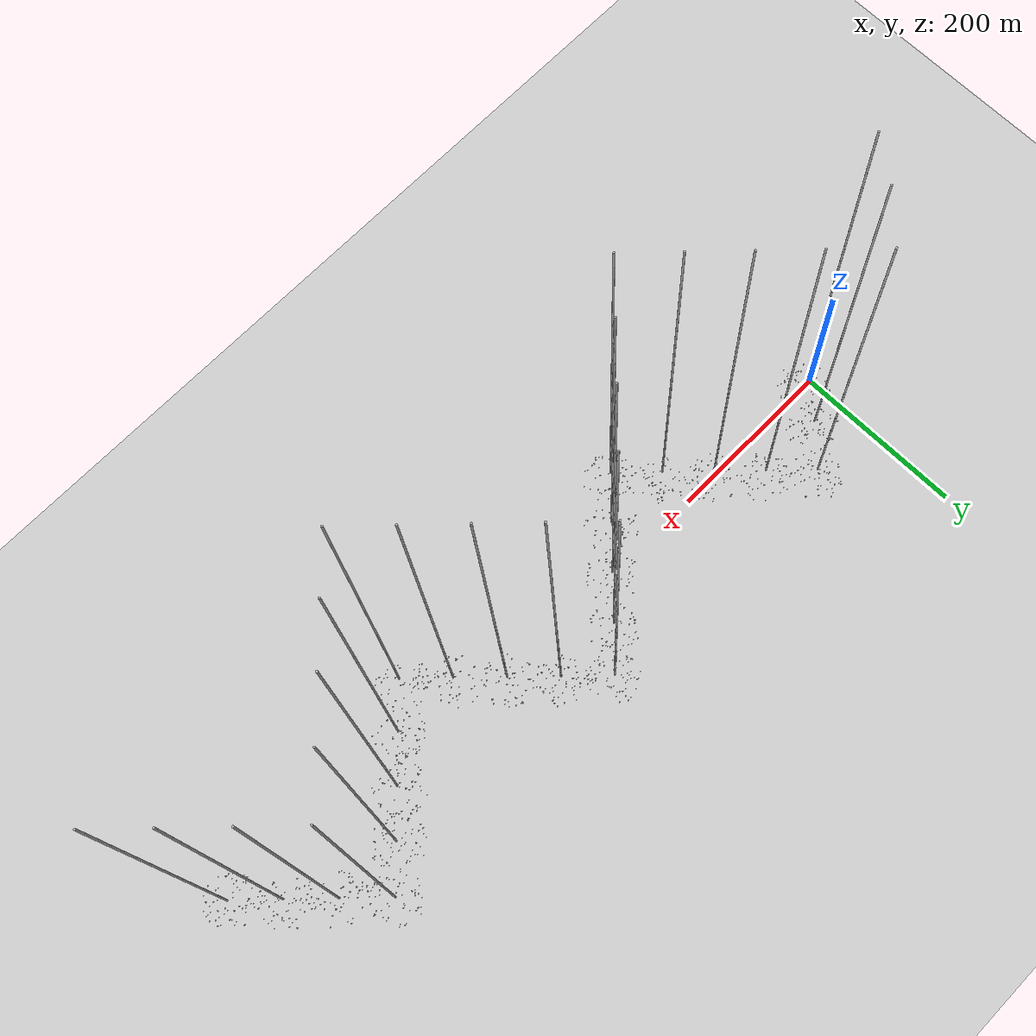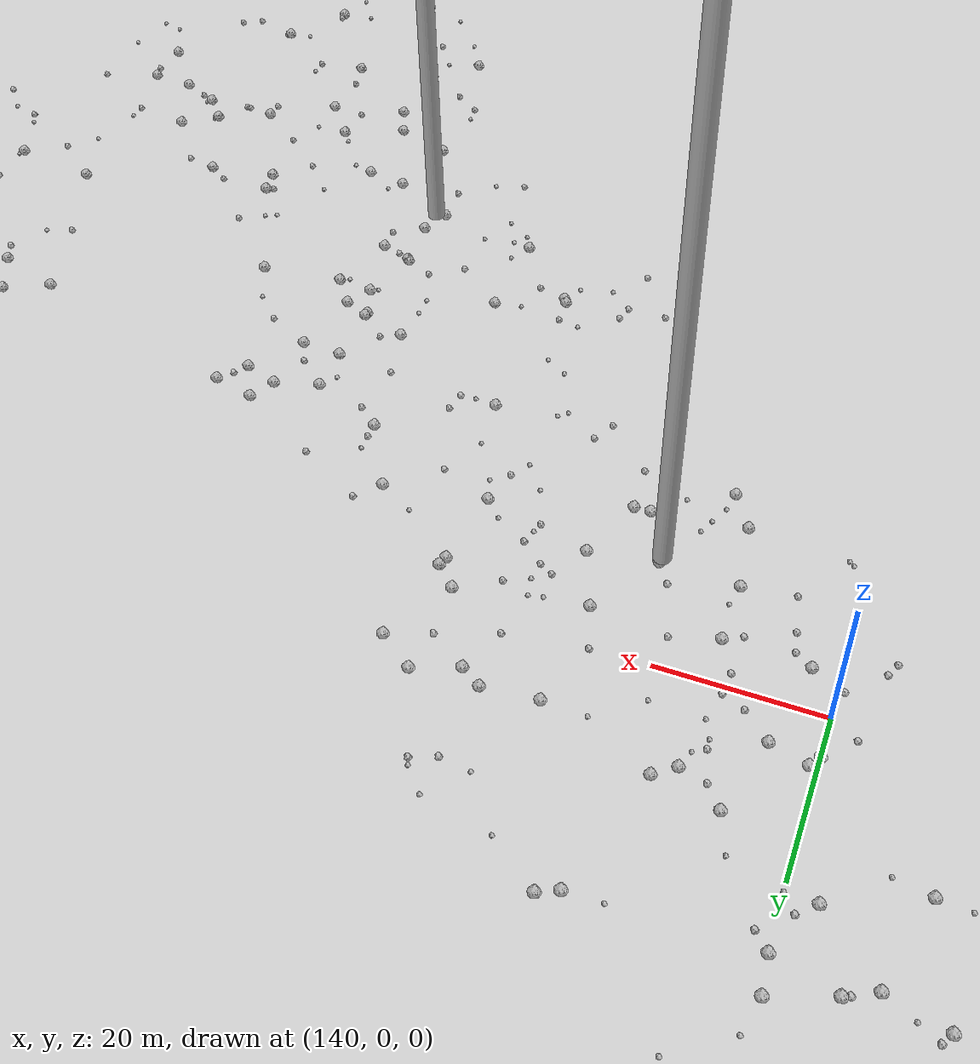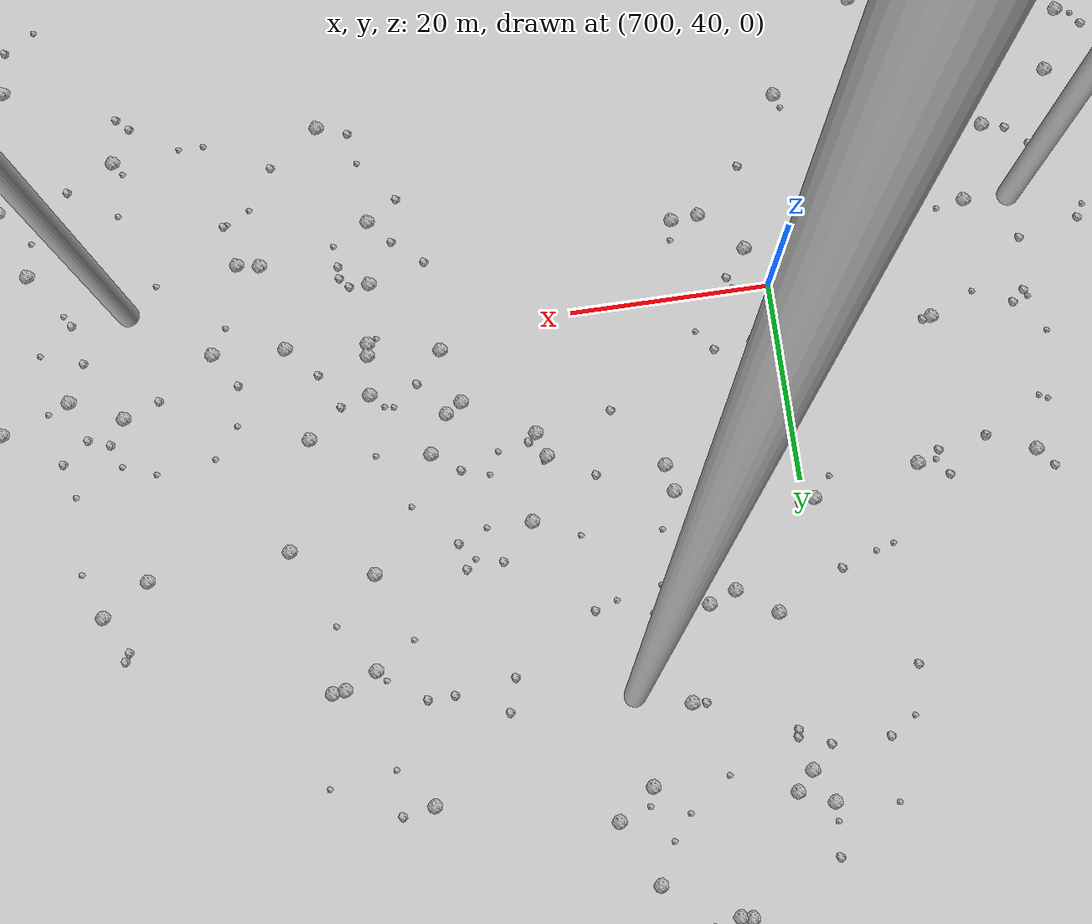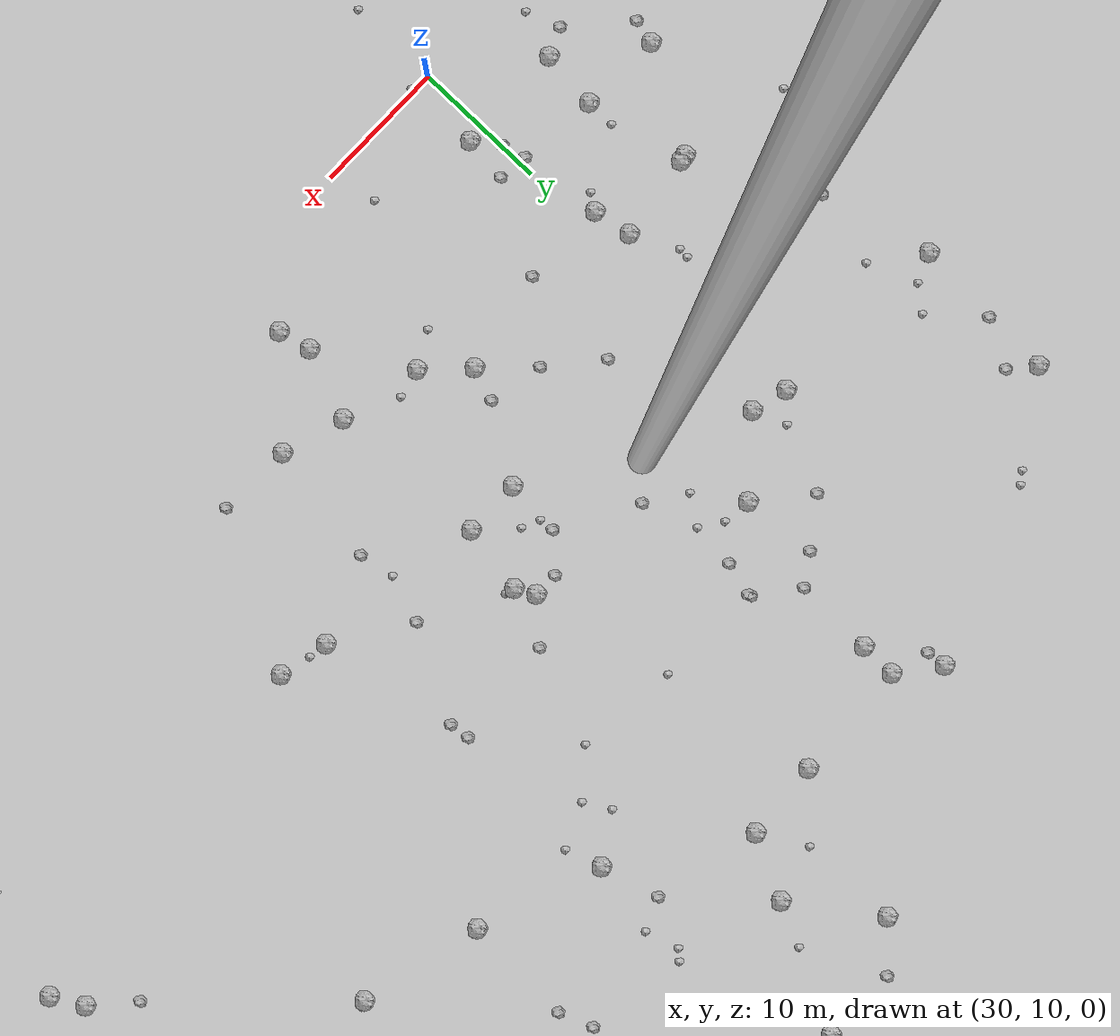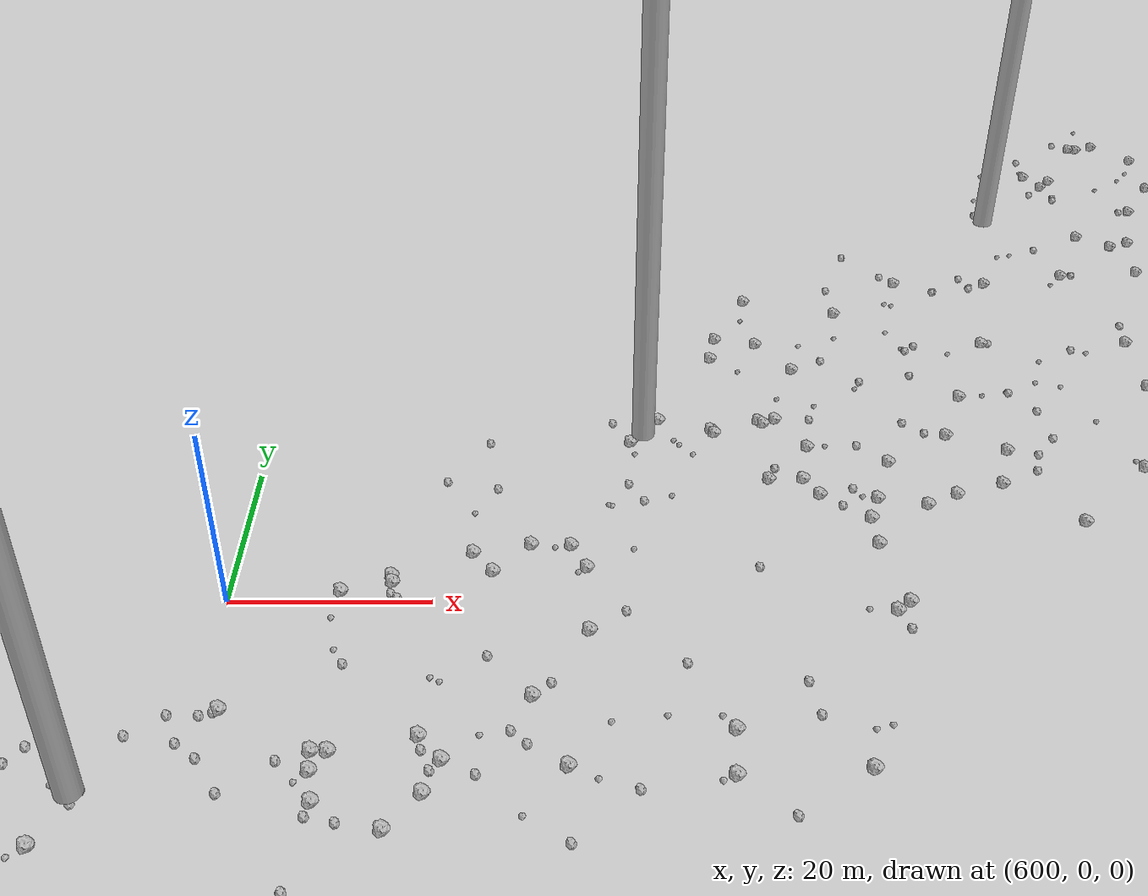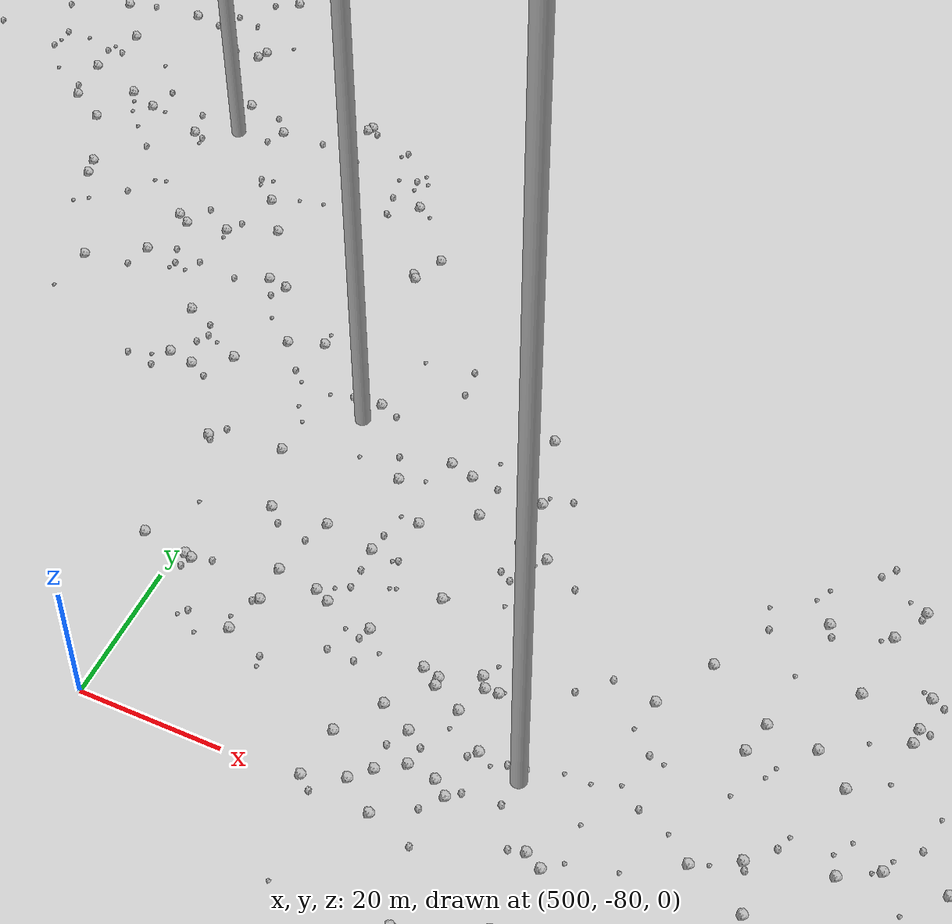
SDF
<sdf version="1.6">
 <world name="default">
  <include><uri>model://custom_ground</uri></include>
  <include><uri>model://sun</uri></include>
  <spherical_coordinates>
   <surface_model>EARTH_WGS84</surface_model>
   <latitude_deg>38.161479</latitude_deg>
   <longitude_deg>-122.454630</longitude_deg>
   <elevation>488.0</elevation>
   <heading_deg>90</heading_deg>
  </spherical_coordinates>
  <model name="rock1_0_0">
   <include><uri>model://rock1</uri><pose>-10.307833685437739 -17.85518943456887 0.5 0 0 0</pose></include>
  </model>
  <model name="rock1_0_1">
   <include><uri>model://rock1</uri><pose>10.448616298842182 -11.80587458531868 0.5 0 0 0</pose></include>
  </model>
  <model name="rock1_0_2">
   <include><uri>model://rock1</uri><pose>23.517651244544368 19.533427763528863 0.5 0 0 0</pose></include>
  </model>
  <model name="rock1_0_3">
   <include><uri>model://rock1</uri><pose>1.1880558107352037 7.084446178551843 0.5 0 0 0</pose></include>
  </model>
  <model name="rock1_0_4">
   <include><uri>model://rock1</uri><pose>-1.795628786913536 -14.700622959977103 0.5 0 0 0</pose></include>
  </model>
  <model name="rock1_0_5">
   <include><uri>model://rock1</uri><pose>10.146372818140204 -29.68067572311503 0.5 0 0 0</pose></include>
  </model>
  <model name="rock1_0_6">
   <include><uri>model://rock1</uri><pose>29.3042301435094 -22.137740524987258 0.5 0 0 0</pose></include>
  </model>
  <model name="rock1_0_7">
   <include><uri>model://rock1</uri><pose>-6.717508183285631 23.847237975825216 0.5 0 0 0</pose></include>
  </model>
  <model name="rock1_0_8">
   <include><uri>model://rock1</uri><pose>17.386789054686318 19.733217177491987 0.5 0 0 0</pose></include>
  </model>
  <model name="rock1_0_9">
   <include><uri>model://rock1</uri><pose>-5.864184833933184 20.534969034190027 0.5 0 0 0</pose></include>
  </model>
  <model name="rock1_0_10">
   <include><uri>model://rock1</uri><pose>-7.760374870198872 3.1888157762993856 0.5 0 0 0</pose></include>
  </model>
  <model name="rock1_0_11">
   <include><uri>model://rock1</uri><pose>-2.721785012246805 4.73354834969723 0.5 0 0 0</pose></include>
  </model>
  <model name="rock1_0_12">
   <include><uri>model://rock1</uri><pose>21.48837844746741 27.013029863951772 0.5 0 0 0</pose></include>
  </model>
  <model name="rock1_0_13">
   <include><uri>model://rock1</uri><pose>-5.140197389439065 25.105804382480358 0.5 0 0 0</pose></include>
  </model>
  <model name="rock1_0_14">
   <include><uri>model://rock1</uri><pose>5.125344375863861 -14.837496671802256 0.5 0 0 0</pose></include>
  </model>
  <model name="rock1_0_15">
   <include><uri>model://rock1</uri><pose>20.50491525555907 -18.773134696811468 0.5 0 0 0</pose></include>
  </model>
  <model name="rock1_0_16">
   <include><uri>model://rock1</uri><pose>25.070374426544262 -20.537365303295744 0.5 0 0 0</pose></include>
  </model>
  <model name="rock1_0_17">
   <include><uri>model://rock1</uri><pose>12.206816095377896 -4.262487109916034 0.5 0 0 0</pose></include>
  </model>
  <model name="rock1_0_18">
   <include><uri>model://rock1</uri><pose>9.314530999005822 3.1289760273519818 0.5 0 0 0</pose></include>
  </model>
  <model name="rock1_0_19">
   <include><uri>model://rock1</uri><pose>31.312147680285833 15.319146105169125 0.5 0 0 0</pose></include>
  </model>
  <model name="rock1_0_20">
   <include><uri>model://rock1</uri><pose>2.016513899799161 -17.580852236929243 0.5 0 0 0</pose></include>
  </model>
  <model name="rock1_0_21">
   <include><uri>model://rock1</uri><pose>23.294720144863675 -10.168283524781405 0.5 0 0 0</pose></include>
  </model>
  <model name="rock1_0_22">
   <include><uri>model://rock1</uri><pose>0.10269832410829594 -16.52855328796437 0.5 0 0 0</pose></include>
  </model>
  <model name="rock1_0_23">
   <include><uri>model://rock1</uri><pose>10.015269173864802 13.698324513280795 0.5 0 0 0</pose></include>
  </model>
  <model name="rock1_0_24">
   <include><uri>model://rock1</uri><pose>23.104122580344907 15.19748517412809 0.5 0 0 0</pose></include>
  </model>
  <model name="rock1_0_25">
   <include><uri>model://rock1</uri><pose>12.174875009242335 4.461362861513983 0.5 0 0 0</pose></include>
  </model>
  <model name="rock1_0_26">
   <include><uri>model://rock1</uri><pose>18.811335987200167 -20.560367333638688 0.5 0 0 0</pose></include>
  </model>
  <model name="rock2_0_0">
   <include><uri>model://rock2</uri><pose>21.01417605007707 14.313682053407 0.3 0 0 0</pose></include>
  </model>
  <model name="rock2_0_1">
   <include><uri>model://rock2</uri><pose>11.507018598572255 -10.601042176901878 0.3 0 0 0</pose></include>
  </model>
  <model name="rock2_0_2">
   <include><uri>model://rock2</uri><pose>19.924545016767517 -19.39431592686077 0.3 0 0 0</pose></include>
  </model>
  <model name="rock2_0_3">
   <include><uri>model://rock2</uri><pose>13.555220796957308 -22.162443509834915 0.3 0 0 0</pose></include>
  </model>
  <model name="rock2_0_4">
   <include><uri>model://rock2</uri><pose>-8.936186714521577 11.069984344817627 0.3 0 0 0</pose></include>
  </model>
  <model name="rock2_0_5">
   <include><uri>model://rock2</uri><pose>8.647079767289704 10.327096597118597 0.3 0 0 0</pose></include>
  </model>
  <model name="rock2_0_6">
   <include><uri>model://rock2</uri><pose>20.306309139190112 0.5365384268996749 0.3 0 0 0</pose></include>
  </model>
  <model name="rock2_0_7">
   <include><uri>model://rock2</uri><pose>-1.7748101464592345 -24.451074893968766 0.3 0 0 0</pose></include>
  </model>
  <model name="rock2_0_8">
   <include><uri>model://rock2</uri><pose>19.78983604270936 -17.542259316791426 0.3 0 0 0</pose></include>
  </model>
  <model name="rock2_0_9">
   <include><uri>model://rock2</uri><pose>31.641076134505425 18.691910386852165 0.3 0 0 0</pose></include>
  </model>
  <model name="rock2_0_10">
   <include><uri>model://rock2</uri><pose>10.25985658344226 -23.625701264173415 0.3 0 0 0</pose></include>
  </model>
  <model name="rock2_0_11">
   <include><uri>model://rock2</uri><pose>22.047644022559723 -24.347803883815196 0.3 0 0 0</pose></include>
  </model>
  <model name="rock2_0_12">
   <include><uri>model://rock2</uri><pose>14.918341640115209 -19.35590953835227 0.3 0 0 0</pose></include>
  </model>
  <model name="rock2_0_13">
   <include><uri>model://rock2</uri><pose>30.991888945314777 -7.448582151520661 0.3 0 0 0</pose></include>
  </model>
  <model name="rock2_0_14">
   <include><uri>model://rock2</uri><pose>3.1237944430124607 -17.99236745460167 0.3 0 0 0</pose></include>
  </model>
  <model name="rock2_0_15">
   <include><uri>model://rock2</uri><pose>-0.9922427177591011 -27.735747811944464 0.3 0 0 0</pose></include>
  </model>
  <model name="rock2_0_16">
   <include><uri>model://rock2</uri><pose>-11.885711897911502 13.01758678374815 0.3 0 0 0</pose></include>
  </model>
  <model name="rock2_0_17">
   <include><uri>model://rock2</uri><pose>-18.389069829235606 8.71027357809583 0.3 0 0 0</pose></include>
  </model>
  <model name="rock2_0_18">
   <include><uri>model://rock2</uri><pose>-5.761174112734693 -21.609916236451895 0.3 0 0 0</pose></include>
  </model>
  <model name="rock2_0_19">
   <include><uri>model://rock2</uri><pose>-19.88558740222973 -1.8325398515859384 0.3 0 0 0</pose></include>
  </model>
  <model name="rock2_0_20">
   <include><uri>model://rock2</uri><pose>14.43302501555172 -15.288867888442628 0.3 0 0 0</pose></include>
  </model>
  <model name="rock2_0_21">
   <include><uri>model://rock2</uri><pose>29.899956142964747 17.211513351149343 0.3 0 0 0</pose></include>
  </model>
  <model name="rock2_0_22">
   <include><uri>model://rock2</uri><pose>-0.09233278968024905 12.562385154772997 0.3 0 0 0</pose></include>
  </model>
  <model name="rock2_0_23">
   <include><uri>model://rock2</uri><pose>16.92475968077617 17.930559858822562 0.3 0 0 0</pose></include>
  </model>
  <model name="rock2_0_24">
   <include><uri>model://rock2</uri><pose>2.967433795296074 28.81706346089468 0.3 0 0 0</pose></include>
  </model>
  <model name="rock2_0_25">
   <include><uri>model://rock2</uri><pose>23.650828856734243 -15.37410774704176 0.3 0 0 0</pose></include>
  </model>
  <model name="rock2_0_26">
   <include><uri>model://rock2</uri><pose>3.8339524829843583 2.7777867992684193 0.3 0 0 0</pose></include>
  </model>
  <model name="rock3_0_0">
   <include><uri>model://rock3</uri><pose>6.666722707546548 -3.232290422298412 0.2 0 0 0</pose></include>
  </model>
  <model name="rock3_0_1">
   <include><uri>model://rock3</uri><pose>6.441108493830786 -2.2316955509330114 0.2 0 0 0</pose></include>
  </model>
  <model name="rock3_0_2">
   <include><uri>model://rock3</uri><pose>13.189067393400002 28.732480643986165 0.2 0 0 0</pose></include>
  </model>
  <model name="rock3_0_3">
   <include><uri>model://rock3</uri><pose>-7.731074386605854 20.40163024893109 0.2 0 0 0</pose></include>
  </model>
  <model name="rock3_0_4">
   <include><uri>model://rock3</uri><pose>-4.168885141944346 -14.902200366611194 0.2 0 0 0</pose></include>
  </model>
  <model name="rock3_0_5">
   <include><uri>model://rock3</uri><pose>-5.735953154326159 22.89779037488121 0.2 0 0 0</pose></include>
  </model>
  <model name="rock3_0_6">
   <include><uri>model://rock3</uri><pose>9.873190147381148 -8.05670872255979 0.2 0 0 0</pose></include>
  </model>
  <model name="rock3_0_7">
   <include><uri>model://rock3</uri><pose>13.25851382691976 -19.954370090946554 0.2 0 0 0</pose></include>
  </model>
  <model name="rock3_0_8">
   <include><uri>model://rock3</uri><pose>1.1029550074144971 -3.8310269444528586 0.2 0 0 0</pose></include>
  </model>
  <model name="rock3_0_9">
   <include><uri>model://rock3</uri><pose>-1.3366535924974556 11.408075014213424 0.2 0 0 0</pose></include>
  </model>
  <model name="rock3_0_10">
   <include><uri>model://rock3</uri><pose>35.89260555664294 -10.699868522622975 0.2 0 0 0</pose></include>
  </model>
  <model name="rock3_0_11">
   <include><uri>model://rock3</uri><pose>-2.0308282592573548 7.853959241771321 0.2 0 0 0</pose></include>
  </model>
  <model name="rock3_0_12">
   <include><uri>model://rock3</uri><pose>12.42732262506307 -16.35979725811752 0.2 0 0 0</pose></include>
  </model>
  <model name="rock3_0_13">
   <include><uri>model://rock3</uri><pose>-13.299447828508828 -11.922409771838808 0.2 0 0 0</pose></include>
  </model>
  <model name="rock3_0_14">
   <include><uri>model://rock3</uri><pose>10.19621082382098 -13.213175859419735 0.2 0 0 0</pose></include>
  </model>
  <model name="rock3_0_15">
   <include><uri>model://rock3</uri><pose>37.44682075997744 -9.133698104077979 0.2 0 0 0</pose></include>
  </model>
  <model name="rock3_0_16">
   <include><uri>model://rock3</uri><pose>8.819797084327167 16.172356789155955 0.2 0 0 0</pose></include>
  </model>
  <model name="rock3_0_17">
   <include><uri>model://rock3</uri><pose>5.12661928373096 -19.608860571368798 0.2 0 0 0</pose></include>
  </model>
  <model name="rock3_0_18">
   <include><uri>model://rock3</uri><pose>23.47517596872155 21.701313638174824 0.2 0 0 0</pose></include>
  </model>
  <model name="rock3_0_19">
   <include><uri>model://rock3</uri><pose>31.469460027759737 9.712745317699017 0.2 0 0 0</pose></include>
  </model>
  <model name="rock3_0_20">
   <include><uri>model://rock3</uri><pose>33.7028862945466 -17.190374115394533 0.2 0 0 0</pose></include>
  </model>
  <model name="rock3_0_21">
   <include><uri>model://rock3</uri><pose>-2.98269141769239 20.164586682495475 0.2 0 0 0</pose></include>
  </model>
  <model name="rock3_0_22">
   <include><uri>model://rock3</uri><pose>25.373227853607347 -18.872048412652067 0.2 0 0 0</pose></include>
  </model>
  <model name="rock3_0_23">
   <include><uri>model://rock3</uri><pose>21.899261980477057 11.75773612514078 0.2 0 0 0</pose></include>
  </model>
  <model name="rock3_0_24">
   <include><uri>model://rock3</uri><pose>-2.634987423309699 21.570720104963833 0.2 0 0 0</pose></include>
  </model>
  <model name="rock3_0_25">
   <include><uri>model://rock3</uri><pose>7.309497685279517 -27.205615215090507 0.2 0 0 0</pose></include>
  </model>
  <model name="rock3_0_26">
   <include><uri>model://rock3</uri><pose>30.0263041755777 3.097570701310694 0.2 0 0 0</pose></include>
  </model>
  <model name="rock1_1_0">
   <include><uri>model://rock1</uri><pose>36.155939603687955 47.21640225206283 0.5 0 0 0</pose></include>
  </model>
  <model name="rock1_1_1">
   <include><uri>model://rock1</uri><pose>37.89851215916954 62.898754839996 0.5 0 0 0</pose></include>
  </model>
  <model name="rock1_1_2">
   <include><uri>model://rock1</uri><pose>67.81501785733562 31.88876014065051 0.5 0 0 0</pose></include>
  </model>
  <model name="rock1_1_3">
   <include><uri>model://rock1</uri><pose>31.284192802086285 42.98050922577627 0.5 0 0 0</pose></include>
  </model>
  <model name="rock1_1_4">
   <include><uri>model://rock1</uri><pose>51.23466342021466 40.95823709163296 0.5 0 0 0</pose></include>
  </model>
  <model name="rock1_1_5">
   <include><uri>model://rock1</uri><pose>49.81022780916033 17.386966836237356 0.5 0 0 0</pose></include>
  </model>
  <model name="rock1_1_6">
   <include><uri>model://rock1</uri><pose>28.26497285994002 28.029033530387366 0.5 0 0 0</pose></include>
  </model>
  <model name="rock1_1_7">
   <include><uri>model://rock1</uri><pose>64.04556712149102 32.6786463231507 0.5 0 0 0</pose></include>
  </model>
  <model name="rock1_1_8">
   <include><uri>model://rock1</uri><pose>22.009253657413577 27.084486697466946 0.5 0 0 0</pose></include>
  </model>
  <model name="rock1_1_9">
   <include><uri>model://rock1</uri><pose>61.91524715177225 57.574569389889575 0.5 0 0 0</pose></include>
  </model>
  <model name="rock1_1_10">
   <include><uri>model://rock1</uri><pose>42.70265050370855 26.713999393316747 0.5 0 0 0</pose></include>
  </model>
  <model name="rock1_1_11">
   <include><uri>model://rock1</uri><pose>46.87475663082416 34.45334945443908 0.5 0 0 0</pose></include>
  </model>
  <model name="rock1_1_12">
   <include><uri>model://rock1</uri><pose>29.32733795010384 37.540630635827554 0.5 0 0 0</pose></include>
  </model>
  <model name="rock1_1_13">
   <include><uri>model://rock1</uri><pose>52.02260688876527 39.54087927200072 0.5 0 0 0</pose></include>
  </model>
  <model name="rock1_1_14">
   <include><uri>model://rock1</uri><pose>51.73541195725397 22.526013313536627 0.5 0 0 0</pose></include>
  </model>
  <model name="rock1_1_15">
   <include><uri>model://rock1</uri><pose>14.964883334424965 55.349746035600035 0.5 0 0 0</pose></include>
  </model>
  <model name="rock1_1_16">
   <include><uri>model://rock1</uri><pose>37.87615531232669 60.18452424997095 0.5 0 0 0</pose></include>
  </model>
  <model name="rock1_1_17">
   <include><uri>model://rock1</uri><pose>28.810385433501896 25.171193501653622 0.5 0 0 0</pose></include>
  </model>
  <model name="rock1_1_18">
   <include><uri>model://rock1</uri><pose>50.408671700455294 14.982569561872323 0.5 0 0 0</pose></include>
  </model>
  <model name="rock1_1_19">
   <include><uri>model://rock1</uri><pose>51.1438901883191 34.49470328033195 0.5 0 0 0</pose></include>
  </model>
  <model name="rock1_1_20">
   <include><uri>model://rock1</uri><pose>45.61448889487073 23.86165122399187 0.5 0 0 0</pose></include>
  </model>
  <model name="rock1_1_21">
   <include><uri>model://rock1</uri><pose>14.552706151211776 44.2448929154765 0.5 0 0 0</pose></include>
  </model>
  <model name="rock1_1_22">
   <include><uri>model://rock1</uri><pose>34.90069679520625 65.20681369688012 0.5 0 0 0</pose></include>
  </model>
  <model name="rock1_1_23">
   <include><uri>model://rock1</uri><pose>52.66462405341271 63.76487186032488 0.5 0 0 0</pose></include>
  </model>
  <model name="rock1_1_24">
   <include><uri>model://rock1</uri><pose>28.575417029098467 43.684106722127865 0.5 0 0 0</pose></include>
  </model>
  <model name="rock1_1_25">
   <include><uri>model://rock1</uri><pose>56.43772263421306 21.099270398817765 0.5 0 0 0</pose></include>
  </model>
  <model name="rock1_1_26">
   <include><uri>model://rock1</uri><pose>46.82264372276675 63.30353234418556 0.5 0 0 0</pose></include>
  </model>
  <model name="rock2_1_0">
   <include><uri>model://rock2</uri><pose>35.026058861320244 63.777568044271234 0.3 0 0 0</pose></include>
  </model>
  <model name="rock2_1_1">
   <include><uri>model://rock2</uri><pose>58.484322461802925 36.235008312787684 0.3 0 0 0</pose></include>
  </model>
  <model name="rock2_1_2">
   <include><uri>model://rock2</uri><pose>40.87285736673249 51.78533422008631 0.3 0 0 0</pose></include>
  </model>
  <model name="rock2_1_3">
   <include><uri>model://rock2</uri><pose>32.31371861559824 50.34778433786814 0.3 0 0 0</pose></include>
  </model>
  <model name="rock2_1_4">
   <include><uri>model://rock2</uri><pose>35.1648139712986 25.177991415924076 0.3 0 0 0</pose></include>
  </model>
  <model name="rock2_1_5">
   <include><uri>model://rock2</uri><pose>17.16635523030806 31.6853434455505 0.3 0 0 0</pose></include>
  </model>
  <model name="rock2_1_6">
   <include><uri>model://rock2</uri><pose>16.732442877363674 32.878305643283994 0.3 0 0 0</pose></include>
  </model>
  <model name="rock2_1_7">
   <include><uri>model://rock2</uri><pose>35.60920339071001 52.79695300914426 0.3 0 0 0</pose></include>
  </model>
  <model name="rock2_1_8">
   <include><uri>model://rock2</uri><pose>61.84639738325887 44.5041571568113 0.3 0 0 0</pose></include>
  </model>
  <model name="rock2_1_9">
   <include><uri>model://rock2</uri><pose>37.77710044211149 54.295783664598495 0.3 0 0 0</pose></include>
  </model>
  <model name="rock2_1_10">
   <include><uri>model://rock2</uri><pose>43.52021521502075 29.185861918563766 0.3 0 0 0</pose></include>
  </model>
  <model name="rock2_1_11">
   <include><uri>model://rock2</uri><pose>49.32923225444536 40.98663750146295 0.3 0 0 0</pose></include>
  </model>
  <model name="rock2_1_12">
   <include><uri>model://rock2</uri><pose>14.86109384540673 50.49985127083164 0.3 0 0 0</pose></include>
  </model>
  <model name="rock2_1_13">
   <include><uri>model://rock2</uri><pose>62.030655521023995 42.997604168210486 0.3 0 0 0</pose></include>
  </model>
  <model name="rock2_1_14">
   <include><uri>model://rock2</uri><pose>18.40396508220082 33.92317072645102 0.3 0 0 0</pose></include>
  </model>
  <model name="rock2_1_15">
   <include><uri>model://rock2</uri><pose>61.99094624027257 20.928387343581857 0.3 0 0 0</pose></include>
  </model>
  <model name="rock2_1_16">
   <include><uri>model://rock2</uri><pose>16.77547964467465 35.95000192079057 0.3 0 0 0</pose></include>
  </model>
  <model name="rock2_1_17">
   <include><uri>model://rock2</uri><pose>40.79194027622361 51.975315567161076 0.3 0 0 0</pose></include>
  </model>
  <model name="rock2_1_18">
   <include><uri>model://rock2</uri><pose>40.2040989319269 49.286724068077774 0.3 0 0 0</pose></include>
  </model>
  <model name="rock2_1_19">
   <include><uri>model://rock2</uri><pose>35.691826286414994 33.105277436388135 0.3 0 0 0</pose></include>
  </model>
  <model name="rock2_1_20">
   <include><uri>model://rock2</uri><pose>41.38897598784995 41.89962094290124 0.3 0 0 0</pose></include>
  </model>
  <model name="rock2_1_21">
   <include><uri>model://rock2</uri><pose>47.113258459334276 38.64601296589065 0.3 0 0 0</pose></include>
  </model>
  <model name="rock2_1_22">
   <include><uri>model://rock2</uri><pose>29.40262090203602 18.950714443493688 0.3 0 0 0</pose></include>
  </model>
  <model name="rock2_1_23">
   <include><uri>model://rock2</uri><pose>53.77231905895677 43.75055937757475 0.3 0 0 0</pose></include>
  </model>
  <model name="rock2_1_24">
   <include><uri>model://rock2</uri><pose>16.716035234747935 53.89883527441918 0.3 0 0 0</pose></include>
  </model>
  <model name="rock2_1_25">
   <include><uri>model://rock2</uri><pose>57.81268177119378 30.11454398370978 0.3 0 0 0</pose></include>
  </model>
  <model name="rock2_1_26">
   <include><uri>model://rock2</uri><pose>39.416129374343214 30.02660161804385 0.3 0 0 0</pose></include>
  </model>
  <model name="rock3_1_0">
   <include><uri>model://rock3</uri><pose>65.4710954881034 32.46177543488953 0.2 0 0 0</pose></include>
  </model>
  <model name="rock3_1_1">
   <include><uri>model://rock3</uri><pose>57.30060016941542 32.714057556717904 0.2 0 0 0</pose></include>
  </model>
  <model name="rock3_1_2">
   <include><uri>model://rock3</uri><pose>18.082215999022445 41.53233116646166 0.2 0 0 0</pose></include>
  </model>
  <model name="rock3_1_3">
   <include><uri>model://rock3</uri><pose>62.78077568451131 54.905540607807666 0.2 0 0 0</pose></include>
  </model>
  <model name="rock3_1_4">
   <include><uri>model://rock3</uri><pose>17.960113826057814 46.90375289562373 0.2 0 0 0</pose></include>
  </model>
  <model name="rock3_1_5">
   <include><uri>model://rock3</uri><pose>38.50894957107353 43.799826343230336 0.2 0 0 0</pose></include>
  </model>
  <model name="rock3_1_6">
   <include><uri>model://rock3</uri><pose>26.51264985879585 31.320832800359824 0.2 0 0 0</pose></include>
  </model>
  <model name="rock3_1_7">
   <include><uri>model://rock3</uri><pose>21.912687750851298 60.283637540472895 0.2 0 0 0</pose></include>
  </model>
  <model name="rock3_1_8">
   <include><uri>model://rock3</uri><pose>48.837087117998365 51.561705831874285 0.2 0 0 0</pose></include>
  </model>
  <model name="rock3_1_9">
   <include><uri>model://rock3</uri><pose>48.54299972173325 36.937035815523856 0.2 0 0 0</pose></include>
  </model>
  <model name="rock3_1_10">
   <include><uri>model://rock3</uri><pose>52.67414153245747 39.34646388539299 0.2 0 0 0</pose></include>
  </model>
  <model name="rock3_1_11">
   <include><uri>model://rock3</uri><pose>39.00717366975964 13.341678640843046 0.2 0 0 0</pose></include>
  </model>
  <model name="rock3_1_12">
   <include><uri>model://rock3</uri><pose>14.149680794032557 31.774649591630727 0.2 0 0 0</pose></include>
  </model>
  <model name="rock3_1_13">
   <include><uri>model://rock3</uri><pose>47.76261165862263 24.3481749810994 0.2 0 0 0</pose></include>
  </model>
  <model name="rock3_1_14">
   <include><uri>model://rock3</uri><pose>16.584018411638414 45.15048433362081 0.2 0 0 0</pose></include>
  </model>
  <model name="rock3_1_15">
   <include><uri>model://rock3</uri><pose>58.4396868166631 55.325645850226685 0.2 0 0 0</pose></include>
  </model>
  <model name="rock3_1_16">
   <include><uri>model://rock3</uri><pose>50.68445857147431 67.19238784890685 0.2 0 0 0</pose></include>
  </model>
  <model name="rock3_1_17">
   <include><uri>model://rock3</uri><pose>42.993391744474806 22.410703220651676 0.2 0 0 0</pose></include>
  </model>
  <model name="rock3_1_18">
   <include><uri>model://rock3</uri><pose>59.556745646375724 53.42436103781619 0.2 0 0 0</pose></include>
  </model>
  <model name="rock3_1_19">
   <include><uri>model://rock3</uri><pose>21.08554040897384 59.65466856366824 0.2 0 0 0</pose></include>
  </model>
  <model name="rock3_1_20">
   <include><uri>model://rock3</uri><pose>56.45389953907963 50.788545400481155 0.2 0 0 0</pose></include>
  </model>
  <model name="rock3_1_21">
   <include><uri>model://rock3</uri><pose>26.56772445133251 32.103894794399395 0.2 0 0 0</pose></include>
  </model>
  <model name="rock3_1_22">
   <include><uri>model://rock3</uri><pose>27.981398294283288 23.98423690858877 0.2 0 0 0</pose></include>
  </model>
  <model name="rock3_1_23">
   <include><uri>model://rock3</uri><pose>47.21336556458111 37.50704457915193 0.2 0 0 0</pose></include>
  </model>
  <model name="rock3_1_24">
   <include><uri>model://rock3</uri><pose>30.263817580189222 45.42056348705788 0.2 0 0 0</pose></include>
  </model>
  <model name="rock3_1_25">
   <include><uri>model://rock3</uri><pose>38.24768773385842 46.99145982019644 0.2 0 0 0</pose></include>
  </model>
  <model name="rock3_1_26">
   <include><uri>model://rock3</uri><pose>39.91558620470677 45.8864171530914 0.2 0 0 0</pose></include>
  </model>
  <model name="rock1_2_0">
   <include><uri>model://rock1</uri><pose>74.55403776751814 97.47270669848591 0.5 0 0 0</pose></include>
  </model>
  <model name="rock1_2_1">
   <include><uri>model://rock1</uri><pose>66.0506111656358 105.08107264486071 0.5 0 0 0</pose></include>
  </model>
  <model name="rock1_2_2">
   <include><uri>model://rock1</uri><pose>54.89909442091684 68.36006969634734 0.5 0 0 0</pose></include>
  </model>
  <model name="rock1_2_3">
   <include><uri>model://rock1</uri><pose>94.9220166022223 98.25104113294226 0.5 0 0 0</pose></include>
  </model>
  <model name="rock1_2_4">
   <include><uri>model://rock1</uri><pose>100.83007073240086 60.46480606256602 0.5 0 0 0</pose></include>
  </model>
  <model name="rock1_2_5">
   <include><uri>model://rock1</uri><pose>50.50757759949338 74.53914462639625 0.5 0 0 0</pose></include>
  </model>
  <model name="rock1_2_6">
   <include><uri>model://rock1</uri><pose>75.7462144392207 65.72915048103181 0.5 0 0 0</pose></include>
  </model>
  <model name="rock1_2_7">
   <include><uri>model://rock1</uri><pose>68.18158234087286 107.2889721548018 0.5 0 0 0</pose></include>
  </model>
  <model name="rock1_2_8">
   <include><uri>model://rock1</uri><pose>92.94789788406918 75.00444450470742 0.5 0 0 0</pose></include>
  </model>
  <model name="rock1_2_9">
   <include><uri>model://rock1</uri><pose>86.55679602194827 109.16993756597336 0.5 0 0 0</pose></include>
  </model>
  <model name="rock1_2_10">
   <include><uri>model://rock1</uri><pose>90.60136889607301 92.76971007318608 0.5 0 0 0</pose></include>
  </model>
  <model name="rock1_2_11">
   <include><uri>model://rock1</uri><pose>88.93412236434783 62.419567902467406 0.5 0 0 0</pose></include>
  </model>
  <model name="rock1_2_12">
   <include><uri>model://rock1</uri><pose>66.88750384157473 88.75881625209976 0.5 0 0 0</pose></include>
  </model>
  <model name="rock1_2_13">
   <include><uri>model://rock1</uri><pose>59.2624125048297 77.4170387434852 0.5 0 0 0</pose></include>
  </model>
  <model name="rock1_2_14">
   <include><uri>model://rock1</uri><pose>106.06165897980281 89.02127513046564 0.5 0 0 0</pose></include>
  </model>
  <model name="rock1_2_15">
   <include><uri>model://rock1</uri><pose>55.08905048562302 91.93021779778535 0.5 0 0 0</pose></include>
  </model>
  <model name="rock1_2_16">
   <include><uri>model://rock1</uri><pose>69.15059598522717 75.78116694185465 0.5 0 0 0</pose></include>
  </model>
  <model name="rock1_2_17">
   <include><uri>model://rock1</uri><pose>75.18296255266031 81.9865158417202 0.5 0 0 0</pose></include>
  </model>
  <model name="rock1_2_18">
   <include><uri>model://rock1</uri><pose>71.1346992069139 54.29450285927931 0.5 0 0 0</pose></include>
  </model>
  <model name="rock1_2_19">
   <include><uri>model://rock1</uri><pose>82.86935734644749 65.06403819537225 0.5 0 0 0</pose></include>
  </model>
  <model name="rock1_2_20">
   <include><uri>model://rock1</uri><pose>73.99449516520588 93.53286428516331 0.5 0 0 0</pose></include>
  </model>
  <model name="rock1_2_21">
   <include><uri>model://rock1</uri><pose>80.28324306656782 52.0759279737504 0.5 0 0 0</pose></include>
  </model>
  <model name="rock1_2_22">
   <include><uri>model://rock1</uri><pose>73.57517847713035 102.23759359567703 0.5 0 0 0</pose></include>
  </model>
  <model name="rock1_2_23">
   <include><uri>model://rock1</uri><pose>83.65399814335447 82.58066864150786 0.5 0 0 0</pose></include>
  </model>
  <model name="rock1_2_24">
   <include><uri>model://rock1</uri><pose>52.74018535075687 89.58398907435706 0.5 0 0 0</pose></include>
  </model>
  <model name="rock1_2_25">
   <include><uri>model://rock1</uri><pose>74.12586280708953 70.8367430711069 0.5 0 0 0</pose></include>
  </model>
  <model name="rock1_2_26">
   <include><uri>model://rock1</uri><pose>70.25647988192155 84.10508288644374 0.5 0 0 0</pose></include>
  </model>
  <model name="rock2_2_0">
   <include><uri>model://rock2</uri><pose>93.80468979206528 72.32800816422608 0.3 0 0 0</pose></include>
  </model>
  <model name="rock2_2_1">
   <include><uri>model://rock2</uri><pose>83.51451495640032 97.97313949311135 0.3 0 0 0</pose></include>
  </model>
  <model name="rock2_2_2">
   <include><uri>model://rock2</uri><pose>86.5679421950394 90.38864901205692 0.3 0 0 0</pose></include>
  </model>
  <model name="rock2_2_3">
   <include><uri>model://rock2</uri><pose>75.72985248644758 80.60147944698964 0.3 0 0 0</pose></include>
  </model>
  <model name="rock2_2_4">
   <include><uri>model://rock2</uri><pose>79.33478094295226 96.26670252980198 0.3 0 0 0</pose></include>
  </model>
  <model name="rock2_2_5">
   <include><uri>model://rock2</uri><pose>63.31467116613269 82.48814318811213 0.3 0 0 0</pose></include>
  </model>
  <model name="rock2_2_6">
   <include><uri>model://rock2</uri><pose>84.52229282804745 55.86234339230455 0.3 0 0 0</pose></include>
  </model>
  <model name="rock2_2_7">
   <include><uri>model://rock2</uri><pose>68.56345871409044 87.23657486973437 0.3 0 0 0</pose></include>
  </model>
  <model name="rock2_2_8">
   <include><uri>model://rock2</uri><pose>71.75142904584501 69.07808396497093 0.3 0 0 0</pose></include>
  </model>
  <model name="rock2_2_9">
   <include><uri>model://rock2</uri><pose>90.22139593478553 68.1560947593719 0.3 0 0 0</pose></include>
  </model>
  <model name="rock2_2_10">
   <include><uri>model://rock2</uri><pose>82.19435645120045 107.3586071254069 0.3 0 0 0</pose></include>
  </model>
  <model name="rock2_2_11">
   <include><uri>model://rock2</uri><pose>68.0132172155415 89.50505392966804 0.3 0 0 0</pose></include>
  </model>
  <model name="rock2_2_12">
   <include><uri>model://rock2</uri><pose>78.81791755352684 103.39579521676055 0.3 0 0 0</pose></include>
  </model>
  <model name="rock2_2_13">
   <include><uri>model://rock2</uri><pose>102.60711886422013 69.48826608896974 0.3 0 0 0</pose></include>
  </model>
  <model name="rock2_2_14">
   <include><uri>model://rock2</uri><pose>78.15759135099778 72.20726257246722 0.3 0 0 0</pose></include>
  </model>
  <model name="rock2_2_15">
   <include><uri>model://rock2</uri><pose>83.41493527023233 100.46289148301065 0.3 0 0 0</pose></include>
  </model>
  <model name="rock2_2_16">
   <include><uri>model://rock2</uri><pose>60.66362788323041 61.94865530112107 0.3 0 0 0</pose></include>
  </model>
  <model name="rock2_2_17">
   <include><uri>model://rock2</uri><pose>94.960576622378 61.343508607509186 0.3 0 0 0</pose></include>
  </model>
  <model name="rock2_2_18">
   <include><uri>model://rock2</uri><pose>85.2596498247722 92.45025990990186 0.3 0 0 0</pose></include>
  </model>
  <model name="rock2_2_19">
   <include><uri>model://rock2</uri><pose>53.51118596506648 77.46028482954989 0.3 0 0 0</pose></include>
  </model>
  <model name="rock2_2_20">
   <include><uri>model://rock2</uri><pose>86.26305036551348 76.78824789116065 0.3 0 0 0</pose></include>
  </model>
  <model name="rock2_2_21">
   <include><uri>model://rock2</uri><pose>70.44331510932011 64.99655824998433 0.3 0 0 0</pose></include>
  </model>
  <model name="rock2_2_22">
   <include><uri>model://rock2</uri><pose>71.534808351659 78.88290166277578 0.3 0 0 0</pose></include>
  </model>
  <model name="rock2_2_23">
   <include><uri>model://rock2</uri><pose>96.40007479106966 73.26466661074069 0.3 0 0 0</pose></include>
  </model>
  <model name="rock2_2_24">
   <include><uri>model://rock2</uri><pose>64.80306793275565 83.68966216510215 0.3 0 0 0</pose></include>
  </model>
  <model name="rock2_2_25">
   <include><uri>model://rock2</uri><pose>71.38868781717139 62.50284651050664 0.3 0 0 0</pose></include>
  </model>
  <model name="rock2_2_26">
   <include><uri>model://rock2</uri><pose>77.3142848308152 86.54891877913713 0.3 0 0 0</pose></include>
  </model>
  <model name="rock3_2_0">
   <include><uri>model://rock3</uri><pose>68.44885379508095 98.45678763918019 0.2 0 0 0</pose></include>
  </model>
  <model name="rock3_2_1">
   <include><uri>model://rock3</uri><pose>63.025390020938225 62.975610772225046 0.2 0 0 0</pose></include>
  </model>
  <model name="rock3_2_2">
   <include><uri>model://rock3</uri><pose>64.52354594171373 85.0249790940214 0.2 0 0 0</pose></include>
  </model>
  <model name="rock3_2_3">
   <include><uri>model://rock3</uri><pose>94.97974561974124 61.39068451816303 0.2 0 0 0</pose></include>
  </model>
  <model name="rock3_2_4">
   <include><uri>model://rock3</uri><pose>98.5767137317831 76.19920364816574 0.2 0 0 0</pose></include>
  </model>
  <model name="rock3_2_5">
   <include><uri>model://rock3</uri><pose>80.69444894487243 52.22129066214565 0.2 0 0 0</pose></include>
  </model>
  <model name="rock3_2_6">
   <include><uri>model://rock3</uri><pose>59.61337176642926 101.83901472796141 0.2 0 0 0</pose></include>
  </model>
  <model name="rock3_2_7">
   <include><uri>model://rock3</uri><pose>69.0749309595605 104.92546242663894 0.2 0 0 0</pose></include>
  </model>
  <model name="rock3_2_8">
   <include><uri>model://rock3</uri><pose>55.10907623993348 82.65188608169264 0.2 0 0 0</pose></include>
  </model>
  <model name="rock3_2_9">
   <include><uri>model://rock3</uri><pose>69.25338085042107 95.20412755552425 0.2 0 0 0</pose></include>
  </model>
  <model name="rock3_2_10">
   <include><uri>model://rock3</uri><pose>93.58762894474737 62.020916459366504 0.2 0 0 0</pose></include>
  </model>
  <model name="rock3_2_11">
   <include><uri>model://rock3</uri><pose>79.41190778556974 84.92198336756599 0.2 0 0 0</pose></include>
  </model>
  <model name="rock3_2_12">
   <include><uri>model://rock3</uri><pose>87.44738759354593 73.71349564266683 0.2 0 0 0</pose></include>
  </model>
  <model name="rock3_2_13">
   <include><uri>model://rock3</uri><pose>62.90288138532101 66.1653900492658 0.2 0 0 0</pose></include>
  </model>
  <model name="rock3_2_14">
   <include><uri>model://rock3</uri><pose>86.62172704612925 65.0091639412291 0.2 0 0 0</pose></include>
  </model>
  <model name="rock3_2_15">
   <include><uri>model://rock3</uri><pose>53.09866341202566 90.10337793591927 0.2 0 0 0</pose></include>
  </model>
  <model name="rock3_2_16">
   <include><uri>model://rock3</uri><pose>66.32996390454784 97.60224791637276 0.2 0 0 0</pose></include>
  </model>
  <model name="rock3_2_17">
   <include><uri>model://rock3</uri><pose>64.2579810008649 100.79879549925539 0.2 0 0 0</pose></include>
  </model>
  <model name="rock3_2_18">
   <include><uri>model://rock3</uri><pose>56.33991472282047 71.5516306631768 0.2 0 0 0</pose></include>
  </model>
  <model name="rock3_2_19">
   <include><uri>model://rock3</uri><pose>62.27496078411944 65.45905120303291 0.2 0 0 0</pose></include>
  </model>
  <model name="rock3_2_20">
   <include><uri>model://rock3</uri><pose>102.07853648416678 75.22536407068388 0.2 0 0 0</pose></include>
  </model>
  <model name="rock3_2_21">
   <include><uri>model://rock3</uri><pose>83.20478440476546 61.80291660102935 0.2 0 0 0</pose></include>
  </model>
  <model name="rock3_2_22">
   <include><uri>model://rock3</uri><pose>93.59996230389817 104.90306407509456 0.2 0 0 0</pose></include>
  </model>
  <model name="rock3_2_23">
   <include><uri>model://rock3</uri><pose>60.34744746539448 99.28747986798427 0.2 0 0 0</pose></include>
  </model>
  <model name="rock3_2_24">
   <include><uri>model://rock3</uri><pose>103.7567914371287 71.45727624067314 0.2 0 0 0</pose></include>
  </model>
  <model name="rock3_2_25">
   <include><uri>model://rock3</uri><pose>79.41959079514086 57.928660413328984 0.2 0 0 0</pose></include>
  </model>
  <model name="rock3_2_26">
   <include><uri>model://rock3</uri><pose>64.68886751358858 92.09032993253643 0.2 0 0 0</pose></include>
  </model>
  <model name="rock1_3_0">
   <include><uri>model://rock1</uri><pose>95.62970253396807 47.86662616431322 0.5 0 0 0</pose></include>
  </model>
  <model name="rock1_3_1">
   <include><uri>model://rock1</uri><pose>101.80087403887748 56.41389733484642 0.5 0 0 0</pose></include>
  </model>
  <model name="rock1_3_2">
   <include><uri>model://rock1</uri><pose>113.14542359480254 57.58029448298557 0.5 0 0 0</pose></include>
  </model>
  <model name="rock1_3_3">
   <include><uri>model://rock1</uri><pose>106.21258742356457 32.259622618939126 0.5 0 0 0</pose></include>
  </model>
  <model name="rock1_3_4">
   <include><uri>model://rock1</uri><pose>113.59756274104203 56.66864181974728 0.5 0 0 0</pose></include>
  </model>
  <model name="rock1_3_5">
   <include><uri>model://rock1</uri><pose>106.1635159221843 30.088515280934345 0.5 0 0 0</pose></include>
  </model>
  <model name="rock1_3_6">
   <include><uri>model://rock1</uri><pose>127.56430358486278 60.10380097521701 0.5 0 0 0</pose></include>
  </model>
  <model name="rock1_3_7">
   <include><uri>model://rock1</uri><pose>132.2757678694778 29.79896968018595 0.5 0 0 0</pose></include>
  </model>
  <model name="rock1_3_8">
   <include><uri>model://rock1</uri><pose>94.62216330279485 49.9159777258141 0.5 0 0 0</pose></include>
  </model>
  <model name="rock1_3_9">
   <include><uri>model://rock1</uri><pose>103.42602650606158 48.202806326293384 0.5 0 0 0</pose></include>
  </model>
  <model name="rock1_3_10">
   <include><uri>model://rock1</uri><pose>121.57911946154609 29.85906398882737 0.5 0 0 0</pose></include>
  </model>
  <model name="rock1_3_11">
   <include><uri>model://rock1</uri><pose>128.76103235602062 28.106240683522735 0.5 0 0 0</pose></include>
  </model>
  <model name="rock1_3_12">
   <include><uri>model://rock1</uri><pose>102.15984471095744 29.52110435072273 0.5 0 0 0</pose></include>
  </model>
  <model name="rock1_3_13">
   <include><uri>model://rock1</uri><pose>95.41504481385023 35.864999674016474 0.5 0 0 0</pose></include>
  </model>
  <model name="rock1_3_14">
   <include><uri>model://rock1</uri><pose>125.74322095383275 16.888622235575152 0.5 0 0 0</pose></include>
  </model>
  <model name="rock1_3_15">
   <include><uri>model://rock1</uri><pose>139.8671102842264 27.887202145316287 0.5 0 0 0</pose></include>
  </model>
  <model name="rock1_3_16">
   <include><uri>model://rock1</uri><pose>136.3679184747434 21.312309978349568 0.5 0 0 0</pose></include>
  </model>
  <model name="rock1_3_17">
   <include><uri>model://rock1</uri><pose>97.0003415064263 59.175168330050234 0.5 0 0 0</pose></include>
  </model>
  <model name="rock1_3_18">
   <include><uri>model://rock1</uri><pose>108.8272049801592 17.624806064014223 0.5 0 0 0</pose></include>
  </model>
  <model name="rock1_3_19">
   <include><uri>model://rock1</uri><pose>106.03437331353034 53.68900766160625 0.5 0 0 0</pose></include>
  </model>
  <model name="rock1_3_20">
   <include><uri>model://rock1</uri><pose>94.12697125731182 38.14538295883788 0.5 0 0 0</pose></include>
  </model>
  <model name="rock1_3_21">
   <include><uri>model://rock1</uri><pose>127.31799720828194 47.01299151770859 0.5 0 0 0</pose></include>
  </model>
  <model name="rock1_3_22">
   <include><uri>model://rock1</uri><pose>106.84564884694475 15.552386422338776 0.5 0 0 0</pose></include>
  </model>
  <model name="rock1_3_23">
   <include><uri>model://rock1</uri><pose>104.55213063011816 26.71275273217229 0.5 0 0 0</pose></include>
  </model>
  <model name="rock1_3_24">
   <include><uri>model://rock1</uri><pose>139.39250203564242 32.264857637523676 0.5 0 0 0</pose></include>
  </model>
  <model name="rock1_3_25">
   <include><uri>model://rock1</uri><pose>110.40247790655837 59.0470899417964 0.5 0 0 0</pose></include>
  </model>
  <model name="rock1_3_26">
   <include><uri>model://rock1</uri><pose>109.36573200374595 18.078964744451895 0.5 0 0 0</pose></include>
  </model>
  <model name="rock2_3_0">
   <include><uri>model://rock2</uri><pose>110.17447880394211 54.841221117697536 0.3 0 0 0</pose></include>
  </model>
  <model name="rock2_3_1">
   <include><uri>model://rock2</uri><pose>112.12775735069204 28.760511178134042 0.3 0 0 0</pose></include>
  </model>
  <model name="rock2_3_2">
   <include><uri>model://rock2</uri><pose>133.6618248134691 61.851382055034065 0.3 0 0 0</pose></include>
  </model>
  <model name="rock2_3_3">
   <include><uri>model://rock2</uri><pose>128.44498605329966 43.156903620617975 0.3 0 0 0</pose></include>
  </model>
  <model name="rock2_3_4">
   <include><uri>model://rock2</uri><pose>113.77598719025437 20.700191829702963 0.3 0 0 0</pose></include>
  </model>
  <model name="rock2_3_5">
   <include><uri>model://rock2</uri><pose>122.41005528041765 31.102265033275792 0.3 0 0 0</pose></include>
  </model>
  <model name="rock2_3_6">
   <include><uri>model://rock2</uri><pose>114.84776362997778 64.7171919837736 0.3 0 0 0</pose></include>
  </model>
  <model name="rock2_3_7">
   <include><uri>model://rock2</uri><pose>99.16614205439357 42.68128067093845 0.3 0 0 0</pose></include>
  </model>
  <model name="rock2_3_8">
   <include><uri>model://rock2</uri><pose>115.45918214587223 67.37349575825797 0.3 0 0 0</pose></include>
  </model>
  <model name="rock2_3_9">
   <include><uri>model://rock2</uri><pose>113.27857994749066 46.68924176525774 0.3 0 0 0</pose></include>
  </model>
  <model name="rock2_3_10">
   <include><uri>model://rock2</uri><pose>127.46511575398495 53.4280084466114 0.3 0 0 0</pose></include>
  </model>
  <model name="rock2_3_11">
   <include><uri>model://rock2</uri><pose>112.60510242605996 22.590124014733703 0.3 0 0 0</pose></include>
  </model>
  <model name="rock2_3_12">
   <include><uri>model://rock2</uri><pose>103.25315642975497 44.690531045900556 0.3 0 0 0</pose></include>
  </model>
  <model name="rock2_3_13">
   <include><uri>model://rock2</uri><pose>119.86575802097249 22.34864067176872 0.3 0 0 0</pose></include>
  </model>
  <model name="rock2_3_14">
   <include><uri>model://rock2</uri><pose>103.1688746054086 25.506886133715756 0.3 0 0 0</pose></include>
  </model>
  <model name="rock2_3_15">
   <include><uri>model://rock2</uri><pose>107.97929128934413 18.35073198926841 0.3 0 0 0</pose></include>
  </model>
  <model name="rock2_3_16">
   <include><uri>model://rock2</uri><pose>138.37983154339202 23.100896396502236 0.3 0 0 0</pose></include>
  </model>
  <model name="rock2_3_17">
   <include><uri>model://rock2</uri><pose>107.80990367799109 42.64391388513831 0.3 0 0 0</pose></include>
  </model>
  <model name="rock2_3_18">
   <include><uri>model://rock2</uri><pose>131.38502292214818 29.389734613742366 0.3 0 0 0</pose></include>
  </model>
  <model name="rock2_3_19">
   <include><uri>model://rock2</uri><pose>118.12513855534121 48.96845457385363 0.3 0 0 0</pose></include>
  </model>
  <model name="rock2_3_20">
   <include><uri>model://rock2</uri><pose>135.06007384671068 44.519622010311615 0.3 0 0 0</pose></include>
  </model>
  <model name="rock2_3_21">
   <include><uri>model://rock2</uri><pose>147.40839488444263 44.18419850065942 0.3 0 0 0</pose></include>
  </model>
  <model name="rock2_3_22">
   <include><uri>model://rock2</uri><pose>141.6907364410294 25.941542415066632 0.3 0 0 0</pose></include>
  </model>
  <model name="rock2_3_23">
   <include><uri>model://rock2</uri><pose>91.23546989256909 40.71513361819868 0.3 0 0 0</pose></include>
  </model>
  <model name="rock2_3_24">
   <include><uri>model://rock2</uri><pose>110.95562593417675 58.659458853776755 0.3 0 0 0</pose></include>
  </model>
  <model name="rock2_3_25">
   <include><uri>model://rock2</uri><pose>148.16816534798375 50.31522871560215 0.3 0 0 0</pose></include>
  </model>
  <model name="rock2_3_26">
   <include><uri>model://rock2</uri><pose>127.05600520768719 37.20815195329002 0.3 0 0 0</pose></include>
  </model>
  <model name="rock3_3_0">
   <include><uri>model://rock3</uri><pose>139.9909501296844 21.0285413112216 0.2 0 0 0</pose></include>
  </model>
  <model name="rock3_3_1">
   <include><uri>model://rock3</uri><pose>122.6117253578912 45.184623847893796 0.2 0 0 0</pose></include>
  </model>
  <model name="rock3_3_2">
   <include><uri>model://rock3</uri><pose>121.7716288476797 16.979123431591784 0.2 0 0 0</pose></include>
  </model>
  <model name="rock3_3_3">
   <include><uri>model://rock3</uri><pose>111.57038409364827 55.46611978777448 0.2 0 0 0</pose></include>
  </model>
  <model name="rock3_3_4">
   <include><uri>model://rock3</uri><pose>125.1473902098984 38.73223054763835 0.2 0 0 0</pose></include>
  </model>
  <model name="rock3_3_5">
   <include><uri>model://rock3</uri><pose>94.49583427415904 26.83897838599187 0.2 0 0 0</pose></include>
  </model>
  <model name="rock3_3_6">
   <include><uri>model://rock3</uri><pose>139.73989484035073 59.94238904531133 0.2 0 0 0</pose></include>
  </model>
  <model name="rock3_3_7">
   <include><uri>model://rock3</uri><pose>135.86289480041847 57.774384406612114 0.2 0 0 0</pose></include>
  </model>
  <model name="rock3_3_8">
   <include><uri>model://rock3</uri><pose>92.74945341288222 28.05927015332624 0.2 0 0 0</pose></include>
  </model>
  <model name="rock3_3_9">
   <include><uri>model://rock3</uri><pose>123.27042258647404 55.01987115968442 0.2 0 0 0</pose></include>
  </model>
  <model name="rock3_3_10">
   <include><uri>model://rock3</uri><pose>122.14275196041815 65.61651551312282 0.2 0 0 0</pose></include>
  </model>
  <model name="rock3_3_11">
   <include><uri>model://rock3</uri><pose>104.90507571769342 18.749572648326073 0.2 0 0 0</pose></include>
  </model>
  <model name="rock3_3_12">
   <include><uri>model://rock3</uri><pose>113.67117948165378 68.35792959340222 0.2 0 0 0</pose></include>
  </model>
  <model name="rock3_3_13">
   <include><uri>model://rock3</uri><pose>127.80033363126759 66.22338865964221 0.2 0 0 0</pose></include>
  </model>
  <model name="rock3_3_14">
   <include><uri>model://rock3</uri><pose>140.01552287554466 40.94925221359671 0.2 0 0 0</pose></include>
  </model>
  <model name="rock3_3_15">
   <include><uri>model://rock3</uri><pose>95.37168445920771 28.16877276482337 0.2 0 0 0</pose></include>
  </model>
  <model name="rock3_3_16">
   <include><uri>model://rock3</uri><pose>124.9398440633998 29.714108220510006 0.2 0 0 0</pose></include>
  </model>
  <model name="rock3_3_17">
   <include><uri>model://rock3</uri><pose>96.36106474283523 44.36635462755022 0.2 0 0 0</pose></include>
  </model>
  <model name="rock3_3_18">
   <include><uri>model://rock3</uri><pose>140.34468230609934 36.48451440787224 0.2 0 0 0</pose></include>
  </model>
  <model name="rock3_3_19">
   <include><uri>model://rock3</uri><pose>135.87129651436487 39.13015440946613 0.2 0 0 0</pose></include>
  </model>
  <model name="rock3_3_20">
   <include><uri>model://rock3</uri><pose>115.89249822351101 19.22606049636233 0.2 0 0 0</pose></include>
  </model>
  <model name="rock3_3_21">
   <include><uri>model://rock3</uri><pose>97.36351249734282 58.87405576341082 0.2 0 0 0</pose></include>
  </model>
  <model name="rock3_3_22">
   <include><uri>model://rock3</uri><pose>114.3481759583651 39.07711469565451 0.2 0 0 0</pose></include>
  </model>
  <model name="rock3_3_23">
   <include><uri>model://rock3</uri><pose>94.20273091368115 43.71551683099722 0.2 0 0 0</pose></include>
  </model>
  <model name="rock3_3_24">
   <include><uri>model://rock3</uri><pose>130.15678766071318 15.944263409622966 0.2 0 0 0</pose></include>
  </model>
  <model name="rock3_3_25">
   <include><uri>model://rock3</uri><pose>146.92000527165243 40.91333779861628 0.2 0 0 0</pose></include>
  </model>
  <model name="rock3_3_26">
   <include><uri>model://rock3</uri><pose>139.368197413319 31.683497340056263 0.2 0 0 0</pose></include>
  </model>
  <model name="rock1_4_0">
   <include><uri>model://rock1</uri><pose>184.2764011643411 -2.3689254318396387 0.5 0 0 0</pose></include>
  </model>
  <model name="rock1_4_1">
   <include><uri>model://rock1</uri><pose>184.87386251289553 9.208630443364875 0.5 0 0 0</pose></include>
  </model>
  <model name="rock1_4_2">
   <include><uri>model://rock1</uri><pose>171.50922840579705 -12.329044898386197 0.5 0 0 0</pose></include>
  </model>
  <model name="rock1_4_3">
   <include><uri>model://rock1</uri><pose>145.5835604486556 5.233210397495149 0.5 0 0 0</pose></include>
  </model>
  <model name="rock1_4_4">
   <include><uri>model://rock1</uri><pose>153.7155310831395 11.203601906615845 0.5 0 0 0</pose></include>
  </model>
  <model name="rock1_4_5">
   <include><uri>model://rock1</uri><pose>163.18142880930898 -13.527054168286991 0.5 0 0 0</pose></include>
  </model>
  <model name="rock1_4_6">
   <include><uri>model://rock1</uri><pose>153.65971112911797 -5.778559141012767 0.5 0 0 0</pose></include>
  </model>
  <model name="rock1_4_7">
   <include><uri>model://rock1</uri><pose>168.74776697579566 -5.114710381544992 0.5 0 0 0</pose></include>
  </model>
  <model name="rock1_4_8">
   <include><uri>model://rock1</uri><pose>154.78051974025553 -21.708023972217525 0.5 0 0 0</pose></include>
  </model>
  <model name="rock1_4_9">
   <include><uri>model://rock1</uri><pose>156.20626608778622 13.040332856845438 0.5 0 0 0</pose></include>
  </model>
  <model name="rock1_4_10">
   <include><uri>model://rock1</uri><pose>148.25507933392888 14.658956389158512 0.5 0 0 0</pose></include>
  </model>
  <model name="rock1_4_11">
   <include><uri>model://rock1</uri><pose>143.40812045465168 -5.340349505233579 0.5 0 0 0</pose></include>
  </model>
  <model name="rock1_4_12">
   <include><uri>model://rock1</uri><pose>176.7628911097676 8.874332273134655 0.5 0 0 0</pose></include>
  </model>
  <model name="rock1_4_13">
   <include><uri>model://rock1</uri><pose>186.42183979314632 -6.072617733594502 0.5 0 0 0</pose></include>
  </model>
  <model name="rock1_4_14">
   <include><uri>model://rock1</uri><pose>169.9632822580096 8.321031224761462 0.5 0 0 0</pose></include>
  </model>
  <model name="rock1_4_15">
   <include><uri>model://rock1</uri><pose>168.25475501703656 -20.28055781469969 0.5 0 0 0</pose></include>
  </model>
  <model name="rock1_4_16">
   <include><uri>model://rock1</uri><pose>140.9205933670447 6.534783954088503 0.5 0 0 0</pose></include>
  </model>
  <model name="rock1_4_17">
   <include><uri>model://rock1</uri><pose>139.97849983038043 5.139552493867534 0.5 0 0 0</pose></include>
  </model>
  <model name="rock1_4_18">
   <include><uri>model://rock1</uri><pose>153.5435872397856 -13.327690577349816 0.5 0 0 0</pose></include>
  </model>
  <model name="rock1_4_19">
   <include><uri>model://rock1</uri><pose>179.34322628981067 7.174379963962679 0.5 0 0 0</pose></include>
  </model>
  <model name="rock1_4_20">
   <include><uri>model://rock1</uri><pose>184.87512639258958 -15.753821073464822 0.5 0 0 0</pose></include>
  </model>
  <model name="rock1_4_21">
   <include><uri>model://rock1</uri><pose>163.25459090689958 29.448156089622643 0.5 0 0 0</pose></include>
  </model>
  <model name="rock1_4_22">
   <include><uri>model://rock1</uri><pose>189.19173185422727 5.987822634288307 0.5 0 0 0</pose></include>
  </model>
  <model name="rock1_4_23">
   <include><uri>model://rock1</uri><pose>186.77863659822526 -4.917135327235297 0.5 0 0 0</pose></include>
  </model>
  <model name="rock1_4_24">
   <include><uri>model://rock1</uri><pose>160.8320576786304 28.37095445442295 0.5 0 0 0</pose></include>
  </model>
  <model name="rock1_4_25">
   <include><uri>model://rock1</uri><pose>166.23234793531432 -20.30959464807561 0.5 0 0 0</pose></include>
  </model>
  <model name="rock1_4_26">
   <include><uri>model://rock1</uri><pose>157.46007188391332 -26.086943970774986 0.5 0 0 0</pose></include>
  </model>
  <model name="rock2_4_0">
   <include><uri>model://rock2</uri><pose>135.36101482006293 -7.269406096042772 0.3 0 0 0</pose></include>
  </model>
  <model name="rock2_4_1">
   <include><uri>model://rock2</uri><pose>180.75852956896244 19.418948374202735 0.3 0 0 0</pose></include>
  </model>
  <model name="rock2_4_2">
   <include><uri>model://rock2</uri><pose>136.72670486497327 1.892807096154442 0.3 0 0 0</pose></include>
  </model>
  <model name="rock2_4_3">
   <include><uri>model://rock2</uri><pose>167.09130470365665 0.2677790933025612 0.3 0 0 0</pose></include>
  </model>
  <model name="rock2_4_4">
   <include><uri>model://rock2</uri><pose>148.97630619210594 2.1322295187773648 0.3 0 0 0</pose></include>
  </model>
  <model name="rock2_4_5">
   <include><uri>model://rock2</uri><pose>179.17208943062442 -5.272215684365925 0.3 0 0 0</pose></include>
  </model>
  <model name="rock2_4_6">
   <include><uri>model://rock2</uri><pose>147.0829664180381 -14.224342153571953 0.3 0 0 0</pose></include>
  </model>
  <model name="rock2_4_7">
   <include><uri>model://rock2</uri><pose>134.5861456287701 -8.92007808138532 0.3 0 0 0</pose></include>
  </model>
  <model name="rock2_4_8">
   <include><uri>model://rock2</uri><pose>139.33219365925567 -3.5662346092499675 0.3 0 0 0</pose></include>
  </model>
  <model name="rock2_4_9">
   <include><uri>model://rock2</uri><pose>151.51088038410455 -1.8271455774432113 0.3 0 0 0</pose></include>
  </model>
  <model name="rock2_4_10">
   <include><uri>model://rock2</uri><pose>168.65031348923168 -26.03897737377624 0.3 0 0 0</pose></include>
  </model>
  <model name="rock2_4_11">
   <include><uri>model://rock2</uri><pose>150.36095038955955 12.005767297958812 0.3 0 0 0</pose></include>
  </model>
  <model name="rock2_4_12">
   <include><uri>model://rock2</uri><pose>177.7531844015603 18.290536881731228 0.3 0 0 0</pose></include>
  </model>
  <model name="rock2_4_13">
   <include><uri>model://rock2</uri><pose>145.51500635127755 -6.809376123224435 0.3 0 0 0</pose></include>
  </model>
  <model name="rock2_4_14">
   <include><uri>model://rock2</uri><pose>176.88567305166686 1.5580602693123708 0.3 0 0 0</pose></include>
  </model>
  <model name="rock2_4_15">
   <include><uri>model://rock2</uri><pose>151.39679604073166 -6.917778028299651 0.3 0 0 0</pose></include>
  </model>
  <model name="rock2_4_16">
   <include><uri>model://rock2</uri><pose>175.90962179983777 -8.898234635548949 0.3 0 0 0</pose></include>
  </model>
  <model name="rock2_4_17">
   <include><uri>model://rock2</uri><pose>177.73857623776556 -14.301829605254245 0.3 0 0 0</pose></include>
  </model>
  <model name="rock2_4_18">
   <include><uri>model://rock2</uri><pose>159.36591387792978 -4.135773004388316 0.3 0 0 0</pose></include>
  </model>
  <model name="rock2_4_19">
   <include><uri>model://rock2</uri><pose>161.44416169315303 -11.010813167820086 0.3 0 0 0</pose></include>
  </model>
  <model name="rock2_4_20">
   <include><uri>model://rock2</uri><pose>146.04245050922722 -9.424566103099078 0.3 0 0 0</pose></include>
  </model>
  <model name="rock2_4_21">
   <include><uri>model://rock2</uri><pose>151.7544934038007 1.010345133594246 0.3 0 0 0</pose></include>
  </model>
  <model name="rock2_4_22">
   <include><uri>model://rock2</uri><pose>151.466845485268 8.090231532855952 0.3 0 0 0</pose></include>
  </model>
  <model name="rock2_4_23">
   <include><uri>model://rock2</uri><pose>174.23921798211788 -7.952167094272802 0.3 0 0 0</pose></include>
  </model>
  <model name="rock2_4_24">
   <include><uri>model://rock2</uri><pose>140.03275032847145 17.826258681380267 0.3 0 0 0</pose></include>
  </model>
  <model name="rock2_4_25">
   <include><uri>model://rock2</uri><pose>183.94791032529827 4.041375209912708 0.3 0 0 0</pose></include>
  </model>
  <model name="rock2_4_26">
   <include><uri>model://rock2</uri><pose>178.74431052099987 -11.319862920075042 0.3 0 0 0</pose></include>
  </model>
  <model name="rock3_4_0">
   <include><uri>model://rock3</uri><pose>159.0442936311962 4.330532464996907 0.2 0 0 0</pose></include>
  </model>
  <model name="rock3_4_1">
   <include><uri>model://rock3</uri><pose>162.70189037258177 -23.606149115766865 0.2 0 0 0</pose></include>
  </model>
  <model name="rock3_4_2">
   <include><uri>model://rock3</uri><pose>152.55385045914488 4.52484110226829 0.2 0 0 0</pose></include>
  </model>
  <model name="rock3_4_3">
   <include><uri>model://rock3</uri><pose>180.4229164624446 20.211764214851698 0.2 0 0 0</pose></include>
  </model>
  <model name="rock3_4_4">
   <include><uri>model://rock3</uri><pose>169.35091505875891 24.87804570548348 0.2 0 0 0</pose></include>
  </model>
  <model name="rock3_4_5">
   <include><uri>model://rock3</uri><pose>168.31958061091046 -20.535905489014578 0.2 0 0 0</pose></include>
  </model>
  <model name="rock3_4_6">
   <include><uri>model://rock3</uri><pose>159.013542760746 -21.471661138622263 0.2 0 0 0</pose></include>
  </model>
  <model name="rock3_4_7">
   <include><uri>model://rock3</uri><pose>178.20277941614415 -13.157272702200878 0.2 0 0 0</pose></include>
  </model>
  <model name="rock3_4_8">
   <include><uri>model://rock3</uri><pose>164.54107030699316 8.395764278732393 0.2 0 0 0</pose></include>
  </model>
  <model name="rock3_4_9">
   <include><uri>model://rock3</uri><pose>182.7422125016002 -13.679612030085984 0.2 0 0 0</pose></include>
  </model>
  <model name="rock3_4_10">
   <include><uri>model://rock3</uri><pose>152.89402258427384 8.85009346084724 0.2 0 0 0</pose></include>
  </model>
  <model name="rock3_4_11">
   <include><uri>model://rock3</uri><pose>173.930113727409 18.765060607404834 0.2 0 0 0</pose></include>
  </model>
  <model name="rock3_4_12">
   <include><uri>model://rock3</uri><pose>154.08595735538682 -10.728879587157948 0.2 0 0 0</pose></include>
  </model>
  <model name="rock3_4_13">
   <include><uri>model://rock3</uri><pose>178.00191379767372 22.998164157328297 0.2 0 0 0</pose></include>
  </model>
  <model name="rock3_4_14">
   <include><uri>model://rock3</uri><pose>174.07803966145505 -4.718114511306965 0.2 0 0 0</pose></include>
  </model>
  <model name="rock3_4_15">
   <include><uri>model://rock3</uri><pose>159.88572856892324 -19.61039217364214 0.2 0 0 0</pose></include>
  </model>
  <model name="rock3_4_16">
   <include><uri>model://rock3</uri><pose>146.4068782300085 19.18497110461753 0.2 0 0 0</pose></include>
  </model>
  <model name="rock3_4_17">
   <include><uri>model://rock3</uri><pose>175.82431197283896 -4.397874209218418 0.2 0 0 0</pose></include>
  </model>
  <model name="rock3_4_18">
   <include><uri>model://rock3</uri><pose>176.24941585819897 -6.717156327136475 0.2 0 0 0</pose></include>
  </model>
  <model name="rock3_4_19">
   <include><uri>model://rock3</uri><pose>157.90131115069852 -23.758891535726896 0.2 0 0 0</pose></include>
  </model>
  <model name="rock3_4_20">
   <include><uri>model://rock3</uri><pose>156.32137908367025 28.147921961949784 0.2 0 0 0</pose></include>
  </model>
  <model name="rock3_4_21">
   <include><uri>model://rock3</uri><pose>179.49894189373663 -19.257911741837148 0.2 0 0 0</pose></include>
  </model>
  <model name="rock3_4_22">
   <include><uri>model://rock3</uri><pose>141.98916426776128 -20.59421092083356 0.2 0 0 0</pose></include>
  </model>
  <model name="rock3_4_23">
   <include><uri>model://rock3</uri><pose>151.5284345975909 6.777641777575774 0.2 0 0 0</pose></include>
  </model>
  <model name="rock3_4_24">
   <include><uri>model://rock3</uri><pose>142.61440128796548 -21.084647125523226 0.2 0 0 0</pose></include>
  </model>
  <model name="rock3_4_25">
   <include><uri>model://rock3</uri><pose>164.41929694023875 -16.480063141702566 0.2 0 0 0</pose></include>
  </model>
  <model name="rock3_4_26">
   <include><uri>model://rock3</uri><pose>163.23504323463476 -17.901148097032014 0.2 0 0 0</pose></include>
  </model>
  <model name="rock1_5_0">
   <include><uri>model://rock1</uri><pose>223.6591797147696 -22.652072763291137 0.5 0 0 0</pose></include>
  </model>
  <model name="rock1_5_1">
   <include><uri>model://rock1</uri><pose>213.11019782561547 -51.99268634826353 0.5 0 0 0</pose></include>
  </model>
  <model name="rock1_5_2">
   <include><uri>model://rock1</uri><pose>209.31683726935765 -57.06765560089573 0.5 0 0 0</pose></include>
  </model>
  <model name="rock1_5_3">
   <include><uri>model://rock1</uri><pose>226.5605428252507 -42.83449854714988 0.5 0 0 0</pose></include>
  </model>
  <model name="rock1_5_4">
   <include><uri>model://rock1</uri><pose>209.19239132725588 -50.649966486899515 0.5 0 0 0</pose></include>
  </model>
  <model name="rock1_5_5">
   <include><uri>model://rock1</uri><pose>210.44366109742523 -39.05116520988163 0.5 0 0 0</pose></include>
  </model>
  <model name="rock1_5_6">
   <include><uri>model://rock1</uri><pose>207.57595310945058 -60.43126432487831 0.5 0 0 0</pose></include>
  </model>
  <model name="rock1_5_7">
   <include><uri>model://rock1</uri><pose>197.4471851627884 -13.670481132624623 0.5 0 0 0</pose></include>
  </model>
  <model name="rock1_5_8">
   <include><uri>model://rock1</uri><pose>216.16030746872735 -44.01337107564355 0.5 0 0 0</pose></include>
  </model>
  <model name="rock1_5_9">
   <include><uri>model://rock1</uri><pose>187.03497847877756 -50.447146420467135 0.5 0 0 0</pose></include>
  </model>
  <model name="rock1_5_10">
   <include><uri>model://rock1</uri><pose>195.36252558307612 -46.69509552787538 0.5 0 0 0</pose></include>
  </model>
  <model name="rock1_5_11">
   <include><uri>model://rock1</uri><pose>210.8143592352839 -31.54347604928872 0.5 0 0 0</pose></include>
  </model>
  <model name="rock1_5_12">
   <include><uri>model://rock1</uri><pose>213.5399151467477 -40.460244836576315 0.5 0 0 0</pose></include>
  </model>
  <model name="rock1_5_13">
   <include><uri>model://rock1</uri><pose>215.606621282123 -64.53667785933135 0.5 0 0 0</pose></include>
  </model>
  <model name="rock1_5_14">
   <include><uri>model://rock1</uri><pose>201.9987381486356 -21.95607107134775 0.5 0 0 0</pose></include>
  </model>
  <model name="rock1_5_15">
   <include><uri>model://rock1</uri><pose>218.43765343645617 -21.30743045249188 0.5 0 0 0</pose></include>
  </model>
  <model name="rock1_5_16">
   <include><uri>model://rock1</uri><pose>211.62782843538707 -43.51223965154905 0.5 0 0 0</pose></include>
  </model>
  <model name="rock1_5_17">
   <include><uri>model://rock1</uri><pose>210.34766348466343 -39.47437182892121 0.5 0 0 0</pose></include>
  </model>
  <model name="rock1_5_18">
   <include><uri>model://rock1</uri><pose>194.61851936468702 -58.09379558390112 0.5 0 0 0</pose></include>
  </model>
  <model name="rock1_5_19">
   <include><uri>model://rock1</uri><pose>204.7643633533678 -37.279144256121526 0.5 0 0 0</pose></include>
  </model>
  <model name="rock1_5_20">
   <include><uri>model://rock1</uri><pose>220.80571108833547 -25.833627323765626 0.5 0 0 0</pose></include>
  </model>
  <model name="rock1_5_21">
   <include><uri>model://rock1</uri><pose>211.05756495219612 -25.891591334978223 0.5 0 0 0</pose></include>
  </model>
  <model name="rock1_5_22">
   <include><uri>model://rock1</uri><pose>216.614507000562 -24.354011913291586 0.5 0 0 0</pose></include>
  </model>
  <model name="rock1_5_23">
   <include><uri>model://rock1</uri><pose>208.9659405196873 -50.46274458291076 0.5 0 0 0</pose></include>
  </model>
  <model name="rock1_5_24">
   <include><uri>model://rock1</uri><pose>215.91424955138967 -31.894044623402806 0.5 0 0 0</pose></include>
  </model>
  <model name="rock1_5_25">
   <include><uri>model://rock1</uri><pose>189.1277875887536 -29.962570226922303 0.5 0 0 0</pose></include>
  </model>
  <model name="rock1_5_26">
   <include><uri>model://rock1</uri><pose>186.66707351722332 -49.875935496070575 0.5 0 0 0</pose></include>
  </model>
  <model name="rock2_5_0">
   <include><uri>model://rock2</uri><pose>210.69347769255302 -51.393217411467816 0.3 0 0 0</pose></include>
  </model>
  <model name="rock2_5_1">
   <include><uri>model://rock2</uri><pose>199.3655204177421 -69.58691057140314 0.3 0 0 0</pose></include>
  </model>
  <model name="rock2_5_2">
   <include><uri>model://rock2</uri><pose>186.49912285596895 -46.69444668632677 0.3 0 0 0</pose></include>
  </model>
  <model name="rock2_5_3">
   <include><uri>model://rock2</uri><pose>193.7649897390642 -30.140996925772832 0.3 0 0 0</pose></include>
  </model>
  <model name="rock2_5_4">
   <include><uri>model://rock2</uri><pose>183.53496753885486 -20.167892969321606 0.3 0 0 0</pose></include>
  </model>
  <model name="rock2_5_5">
   <include><uri>model://rock2</uri><pose>178.5904159034202 -51.51779896802857 0.3 0 0 0</pose></include>
  </model>
  <model name="rock2_5_6">
   <include><uri>model://rock2</uri><pose>208.13396427215247 -15.407210670045806 0.3 0 0 0</pose></include>
  </model>
  <model name="rock2_5_7">
   <include><uri>model://rock2</uri><pose>207.15930658100436 -36.221890100863114 0.3 0 0 0</pose></include>
  </model>
  <model name="rock2_5_8">
   <include><uri>model://rock2</uri><pose>204.61431521148072 -24.2359582212532 0.3 0 0 0</pose></include>
  </model>
  <model name="rock2_5_9">
   <include><uri>model://rock2</uri><pose>213.11247806322484 -54.97794891402485 0.3 0 0 0</pose></include>
  </model>
  <model name="rock2_5_10">
   <include><uri>model://rock2</uri><pose>222.07556055227417 -24.285821637397895 0.3 0 0 0</pose></include>
  </model>
  <model name="rock2_5_11">
   <include><uri>model://rock2</uri><pose>174.4092599573866 -31.65704593347383 0.3 0 0 0</pose></include>
  </model>
  <model name="rock2_5_12">
   <include><uri>model://rock2</uri><pose>177.94147485791734 -57.89445127868426 0.3 0 0 0</pose></include>
  </model>
  <model name="rock2_5_13">
   <include><uri>model://rock2</uri><pose>203.44968113953462 -30.860229032043023 0.3 0 0 0</pose></include>
  </model>
  <model name="rock2_5_14">
   <include><uri>model://rock2</uri><pose>194.35627471553826 -27.692356422796145 0.3 0 0 0</pose></include>
  </model>
  <model name="rock2_5_15">
   <include><uri>model://rock2</uri><pose>205.51573314008806 -48.962011519794814 0.3 0 0 0</pose></include>
  </model>
  <model name="rock2_5_16">
   <include><uri>model://rock2</uri><pose>190.66561552647218 -51.40974214671239 0.3 0 0 0</pose></include>
  </model>
  <model name="rock2_5_17">
   <include><uri>model://rock2</uri><pose>221.3736426455041 -34.65287841266823 0.3 0 0 0</pose></include>
  </model>
  <model name="rock2_5_18">
   <include><uri>model://rock2</uri><pose>200.06651635449128 -10.921866893929263 0.3 0 0 0</pose></include>
  </model>
  <model name="rock2_5_19">
   <include><uri>model://rock2</uri><pose>191.3622995028257 -18.366245840249782 0.3 0 0 0</pose></include>
  </model>
  <model name="rock2_5_20">
   <include><uri>model://rock2</uri><pose>173.6425411093783 -51.53888614807808 0.3 0 0 0</pose></include>
  </model>
  <model name="rock2_5_21">
   <include><uri>model://rock2</uri><pose>202.05375305858473 -20.119002255398676 0.3 0 0 0</pose></include>
  </model>
  <model name="rock2_5_22">
   <include><uri>model://rock2</uri><pose>214.567515988807 -29.103802233405673 0.3 0 0 0</pose></include>
  </model>
  <model name="rock2_5_23">
   <include><uri>model://rock2</uri><pose>207.554264433633 -65.25624110203178 0.3 0 0 0</pose></include>
  </model>
  <model name="rock2_5_24">
   <include><uri>model://rock2</uri><pose>175.96794047515257 -28.96117490916913 0.3 0 0 0</pose></include>
  </model>
  <model name="rock2_5_25">
   <include><uri>model://rock2</uri><pose>179.21040155048507 -49.53034334048842 0.3 0 0 0</pose></include>
  </model>
  <model name="rock2_5_26">
   <include><uri>model://rock2</uri><pose>201.35818072333663 -51.471137940924294 0.3 0 0 0</pose></include>
  </model>
  <model name="rock3_5_0">
   <include><uri>model://rock3</uri><pose>196.9221684876113 -58.62572975459988 0.2 0 0 0</pose></include>
  </model>
  <model name="rock3_5_1">
   <include><uri>model://rock3</uri><pose>203.9539609322578 -44.36314503144354 0.2 0 0 0</pose></include>
  </model>
  <model name="rock3_5_2">
   <include><uri>model://rock3</uri><pose>180.22331454172263 -31.901995460084663 0.2 0 0 0</pose></include>
  </model>
  <model name="rock3_5_3">
   <include><uri>model://rock3</uri><pose>181.97296851260938 -22.512545864145245 0.2 0 0 0</pose></include>
  </model>
  <model name="rock3_5_4">
   <include><uri>model://rock3</uri><pose>191.93100667976088 -47.49192016884976 0.2 0 0 0</pose></include>
  </model>
  <model name="rock3_5_5">
   <include><uri>model://rock3</uri><pose>183.8534390084731 -46.37430220709178 0.2 0 0 0</pose></include>
  </model>
  <model name="rock3_5_6">
   <include><uri>model://rock3</uri><pose>193.02616420817378 -11.287051932872451 0.2 0 0 0</pose></include>
  </model>
  <model name="rock3_5_7">
   <include><uri>model://rock3</uri><pose>214.989430544503 -44.740532806178656 0.2 0 0 0</pose></include>
  </model>
  <model name="rock3_5_8">
   <include><uri>model://rock3</uri><pose>188.63041676447463 -23.78548817757202 0.2 0 0 0</pose></include>
  </model>
  <model name="rock3_5_9">
   <include><uri>model://rock3</uri><pose>210.65163067250924 -44.10921000294532 0.2 0 0 0</pose></include>
  </model>
  <model name="rock3_5_10">
   <include><uri>model://rock3</uri><pose>224.51117846333534 -37.9639108515701 0.2 0 0 0</pose></include>
  </model>
  <model name="rock3_5_11">
   <include><uri>model://rock3</uri><pose>181.4632269634485 -53.967996437159606 0.2 0 0 0</pose></include>
  </model>
  <model name="rock3_5_12">
   <include><uri>model://rock3</uri><pose>203.1398199252801 -68.57392188722841 0.2 0 0 0</pose></include>
  </model>
  <model name="rock3_5_13">
   <include><uri>model://rock3</uri><pose>196.27931890354017 -55.69650132008674 0.2 0 0 0</pose></include>
  </model>
  <model name="rock3_5_14">
   <include><uri>model://rock3</uri><pose>209.51139187555827 -27.952430142205436 0.2 0 0 0</pose></include>
  </model>
  <model name="rock3_5_15">
   <include><uri>model://rock3</uri><pose>181.34405732825957 -31.036274161897467 0.2 0 0 0</pose></include>
  </model>
  <model name="rock3_5_16">
   <include><uri>model://rock3</uri><pose>223.6866834354551 -23.33322855222285 0.2 0 0 0</pose></include>
  </model>
  <model name="rock3_5_17">
   <include><uri>model://rock3</uri><pose>185.50685387027733 -39.586248946525934 0.2 0 0 0</pose></include>
  </model>
  <model name="rock3_5_18">
   <include><uri>model://rock3</uri><pose>185.59854695567816 -52.88558947776516 0.2 0 0 0</pose></include>
  </model>
  <model name="rock3_5_19">
   <include><uri>model://rock3</uri><pose>202.0929210547872 -18.265675908924948 0.2 0 0 0</pose></include>
  </model>
  <model name="rock3_5_20">
   <include><uri>model://rock3</uri><pose>200.91972905041592 -57.98255136123298 0.2 0 0 0</pose></include>
  </model>
  <model name="rock3_5_21">
   <include><uri>model://rock3</uri><pose>191.8192439536354 -30.34408318308222 0.2 0 0 0</pose></include>
  </model>
  <model name="rock3_5_22">
   <include><uri>model://rock3</uri><pose>198.5718439700926 -62.10832349005162 0.2 0 0 0</pose></include>
  </model>
  <model name="rock3_5_23">
   <include><uri>model://rock3</uri><pose>204.06895919341008 -41.89882783612776 0.2 0 0 0</pose></include>
  </model>
  <model name="rock3_5_24">
   <include><uri>model://rock3</uri><pose>195.62205878344037 -60.2270446475044 0.2 0 0 0</pose></include>
  </model>
  <model name="rock3_5_25">
   <include><uri>model://rock3</uri><pose>185.68446995298493 -18.713236049131872 0.2 0 0 0</pose></include>
  </model>
  <model name="rock3_5_26">
   <include><uri>model://rock3</uri><pose>182.82117432998825 -37.992874603583466 0.2 0 0 0</pose></include>
  </model>
  <model name="rock1_6_0">
   <include><uri>model://rock1</uri><pose>238.96992187374485 -98.21126026718028 0.5 0 0 0</pose></include>
  </model>
  <model name="rock1_6_1">
   <include><uri>model://rock1</uri><pose>239.46932428792942 -72.30325597441409 0.5 0 0 0</pose></include>
  </model>
  <model name="rock1_6_2">
   <include><uri>model://rock1</uri><pose>220.4378270866618 -88.467922093021 0.5 0 0 0</pose></include>
  </model>
  <model name="rock1_6_3">
   <include><uri>model://rock1</uri><pose>231.30103547770682 -76.9770612104382 0.5 0 0 0</pose></include>
  </model>
  <model name="rock1_6_4">
   <include><uri>model://rock1</uri><pose>258.80250204169596 -81.10693495898016 0.5 0 0 0</pose></include>
  </model>
  <model name="rock1_6_5">
   <include><uri>model://rock1</uri><pose>233.11222262593708 -57.27258977445798 0.5 0 0 0</pose></include>
  </model>
  <model name="rock1_6_6">
   <include><uri>model://rock1</uri><pose>235.1113063169449 -106.70170813699747 0.5 0 0 0</pose></include>
  </model>
  <model name="rock1_6_7">
   <include><uri>model://rock1</uri><pose>246.29311389432004 -69.29236828604232 0.5 0 0 0</pose></include>
  </model>
  <model name="rock1_6_8">
   <include><uri>model://rock1</uri><pose>248.90447362006756 -72.37696304861714 0.5 0 0 0</pose></include>
  </model>
  <model name="rock1_6_9">
   <include><uri>model://rock1</uri><pose>219.8460584890063 -75.24011495671898 0.5 0 0 0</pose></include>
  </model>
  <model name="rock1_6_10">
   <include><uri>model://rock1</uri><pose>227.20272801671072 -104.53309379308726 0.5 0 0 0</pose></include>
  </model>
  <model name="rock1_6_11">
   <include><uri>model://rock1</uri><pose>239.81755067335737 -104.24533156407686 0.5 0 0 0</pose></include>
  </model>
  <model name="rock1_6_12">
   <include><uri>model://rock1</uri><pose>227.60680868852336 -72.14978299247252 0.5 0 0 0</pose></include>
  </model>
  <model name="rock1_6_13">
   <include><uri>model://rock1</uri><pose>242.10247387958123 -58.874410745415325 0.5 0 0 0</pose></include>
  </model>
  <model name="rock1_6_14">
   <include><uri>model://rock1</uri><pose>220.71140988171967 -65.32953852258575 0.5 0 0 0</pose></include>
  </model>
  <model name="rock1_6_15">
   <include><uri>model://rock1</uri><pose>212.83036373164762 -72.94409043657731 0.5 0 0 0</pose></include>
  </model>
  <model name="rock1_6_16">
   <include><uri>model://rock1</uri><pose>214.93335678420777 -93.01239007068209 0.5 0 0 0</pose></include>
  </model>
  <model name="rock1_6_17">
   <include><uri>model://rock1</uri><pose>252.43540037396758 -106.4687331074314 0.5 0 0 0</pose></include>
  </model>
  <model name="rock1_6_18">
   <include><uri>model://rock1</uri><pose>244.72014645596514 -90.92871874612716 0.5 0 0 0</pose></include>
  </model>
  <model name="rock1_6_19">
   <include><uri>model://rock1</uri><pose>253.7152570746257 -74.55815812523916 0.5 0 0 0</pose></include>
  </model>
  <model name="rock1_6_20">
   <include><uri>model://rock1</uri><pose>233.61850236297064 -108.98479337922306 0.5 0 0 0</pose></include>
  </model>
  <model name="rock1_6_21">
   <include><uri>model://rock1</uri><pose>221.38852338560702 -79.15563792550896 0.5 0 0 0</pose></include>
  </model>
  <model name="rock1_6_22">
   <include><uri>model://rock1</uri><pose>259.1951575774612 -75.03822890506541 0.5 0 0 0</pose></include>
  </model>
  <model name="rock1_6_23">
   <include><uri>model://rock1</uri><pose>242.93452191579073 -105.46534147775353 0.5 0 0 0</pose></include>
  </model>
  <model name="rock1_6_24">
   <include><uri>model://rock1</uri><pose>250.784210256053 -66.41387213423144 0.5 0 0 0</pose></include>
  </model>
  <model name="rock1_6_25">
   <include><uri>model://rock1</uri><pose>233.45249745977523 -60.22974197772402 0.5 0 0 0</pose></include>
  </model>
  <model name="rock1_6_26">
   <include><uri>model://rock1</uri><pose>231.23531362997053 -86.60497395639527 0.5 0 0 0</pose></include>
  </model>
  <model name="rock2_6_0">
   <include><uri>model://rock2</uri><pose>237.25233351842954 -85.73651687797985 0.3 0 0 0</pose></include>
  </model>
  <model name="rock2_6_1">
   <include><uri>model://rock2</uri><pose>239.1956571195152 -74.40666274192941 0.3 0 0 0</pose></include>
  </model>
  <model name="rock2_6_2">
   <include><uri>model://rock2</uri><pose>221.7291928259647 -95.7027778610072 0.3 0 0 0</pose></include>
  </model>
  <model name="rock2_6_3">
   <include><uri>model://rock2</uri><pose>239.59042564737626 -57.28903239420036 0.3 0 0 0</pose></include>
  </model>
  <model name="rock2_6_4">
   <include><uri>model://rock2</uri><pose>248.99443171244187 -101.9834176986203 0.3 0 0 0</pose></include>
  </model>
  <model name="rock2_6_5">
   <include><uri>model://rock2</uri><pose>243.36859914204797 -72.84467941505665 0.3 0 0 0</pose></include>
  </model>
  <model name="rock2_6_6">
   <include><uri>model://rock2</uri><pose>215.03122830411291 -85.33762948564214 0.3 0 0 0</pose></include>
  </model>
  <model name="rock2_6_7">
   <include><uri>model://rock2</uri><pose>259.56939618504254 -76.8180131098492 0.3 0 0 0</pose></include>
  </model>
  <model name="rock2_6_8">
   <include><uri>model://rock2</uri><pose>250.25892207429612 -92.5392862214386 0.3 0 0 0</pose></include>
  </model>
  <model name="rock2_6_9">
   <include><uri>model://rock2</uri><pose>250.52769914487396 -73.15093844827445 0.3 0 0 0</pose></include>
  </model>
  <model name="rock2_6_10">
   <include><uri>model://rock2</uri><pose>252.85413943860246 -91.24957258453853 0.3 0 0 0</pose></include>
  </model>
  <model name="rock2_6_11">
   <include><uri>model://rock2</uri><pose>249.87096410549248 -105.22393771015041 0.3 0 0 0</pose></include>
  </model>
  <model name="rock2_6_12">
   <include><uri>model://rock2</uri><pose>226.97398215820544 -76.6776984915564 0.3 0 0 0</pose></include>
  </model>
  <model name="rock2_6_13">
   <include><uri>model://rock2</uri><pose>229.01064590445574 -63.88455919239501 0.3 0 0 0</pose></include>
  </model>
  <model name="rock2_6_14">
   <include><uri>model://rock2</uri><pose>245.07964532719487 -90.7071911561591 0.3 0 0 0</pose></include>
  </model>
  <model name="rock2_6_15">
   <include><uri>model://rock2</uri><pose>230.56133890358078 -106.74310978786465 0.3 0 0 0</pose></include>
  </model>
  <model name="rock2_6_16">
   <include><uri>model://rock2</uri><pose>257.84592858577764 -67.49273138190544 0.3 0 0 0</pose></include>
  </model>
  <model name="rock2_6_17">
   <include><uri>model://rock2</uri><pose>211.87329310394057 -83.1860700041539 0.3 0 0 0</pose></include>
  </model>
  <model name="rock2_6_18">
   <include><uri>model://rock2</uri><pose>234.04594801695515 -50.61912408228711 0.3 0 0 0</pose></include>
  </model>
  <model name="rock2_6_19">
   <include><uri>model://rock2</uri><pose>239.38853922643312 -108.12814938738583 0.3 0 0 0</pose></include>
  </model>
  <model name="rock2_6_20">
   <include><uri>model://rock2</uri><pose>230.58658852151208 -83.03531882693493 0.3 0 0 0</pose></include>
  </model>
  <model name="rock2_6_21">
   <include><uri>model://rock2</uri><pose>245.93351233462533 -59.743627819233566 0.3 0 0 0</pose></include>
  </model>
  <model name="rock2_6_22">
   <include><uri>model://rock2</uri><pose>266.3950558784576 -72.87691508657639 0.3 0 0 0</pose></include>
  </model>
  <model name="rock2_6_23">
   <include><uri>model://rock2</uri><pose>238.97111552940106 -97.36033989730757 0.3 0 0 0</pose></include>
  </model>
  <model name="rock2_6_24">
   <include><uri>model://rock2</uri><pose>232.09333817391393 -57.66725193776984 0.3 0 0 0</pose></include>
  </model>
  <model name="rock2_6_25">
   <include><uri>model://rock2</uri><pose>233.9226371695965 -68.1617994366807 0.3 0 0 0</pose></include>
  </model>
  <model name="rock2_6_26">
   <include><uri>model://rock2</uri><pose>242.81905022557882 -72.78386932827024 0.3 0 0 0</pose></include>
  </model>
  <model name="rock3_6_0">
   <include><uri>model://rock3</uri><pose>249.5107924365685 -72.04051844978886 0.2 0 0 0</pose></include>
  </model>
  <model name="rock3_6_1">
   <include><uri>model://rock3</uri><pose>263.98469200683127 -87.2526640275203 0.2 0 0 0</pose></include>
  </model>
  <model name="rock3_6_2">
   <include><uri>model://rock3</uri><pose>229.45288230074098 -53.041203037704086 0.2 0 0 0</pose></include>
  </model>
  <model name="rock3_6_3">
   <include><uri>model://rock3</uri><pose>225.53305331289758 -60.00477363463427 0.2 0 0 0</pose></include>
  </model>
  <model name="rock3_6_4">
   <include><uri>model://rock3</uri><pose>223.7596781610305 -96.97178980019874 0.2 0 0 0</pose></include>
  </model>
  <model name="rock3_6_5">
   <include><uri>model://rock3</uri><pose>234.82612668487985 -98.9251072138714 0.2 0 0 0</pose></include>
  </model>
  <model name="rock3_6_6">
   <include><uri>model://rock3</uri><pose>237.5008606189232 -83.98831415485989 0.2 0 0 0</pose></include>
  </model>
  <model name="rock3_6_7">
   <include><uri>model://rock3</uri><pose>226.4591047568415 -70.71756317936044 0.2 0 0 0</pose></include>
  </model>
  <model name="rock3_6_8">
   <include><uri>model://rock3</uri><pose>265.8106573209667 -81.48530756002441 0.2 0 0 0</pose></include>
  </model>
  <model name="rock3_6_9">
   <include><uri>model://rock3</uri><pose>261.35950366833447 -86.54372041710917 0.2 0 0 0</pose></include>
  </model>
  <model name="rock3_6_10">
   <include><uri>model://rock3</uri><pose>255.61141605602964 -101.6675160026387 0.2 0 0 0</pose></include>
  </model>
  <model name="rock3_6_11">
   <include><uri>model://rock3</uri><pose>230.91186790085868 -52.38252959250387 0.2 0 0 0</pose></include>
  </model>
  <model name="rock3_6_12">
   <include><uri>model://rock3</uri><pose>223.3276727036773 -66.23509533240124 0.2 0 0 0</pose></include>
  </model>
  <model name="rock3_6_13">
   <include><uri>model://rock3</uri><pose>266.2274223381102 -94.24394041489037 0.2 0 0 0</pose></include>
  </model>
  <model name="rock3_6_14">
   <include><uri>model://rock3</uri><pose>239.26465285733937 -105.69909228090552 0.2 0 0 0</pose></include>
  </model>
  <model name="rock3_6_15">
   <include><uri>model://rock3</uri><pose>246.70966086840627 -68.96574729259456 0.2 0 0 0</pose></include>
  </model>
  <model name="rock3_6_16">
   <include><uri>model://rock3</uri><pose>217.3123595063432 -97.52853272398744 0.2 0 0 0</pose></include>
  </model>
  <model name="rock3_6_17">
   <include><uri>model://rock3</uri><pose>237.17403963517813 -102.57236442526191 0.2 0 0 0</pose></include>
  </model>
  <model name="rock3_6_18">
   <include><uri>model://rock3</uri><pose>254.67596974762714 -100.60927082218534 0.2 0 0 0</pose></include>
  </model>
  <model name="rock3_6_19">
   <include><uri>model://rock3</uri><pose>219.2280200044274 -92.03667622129274 0.2 0 0 0</pose></include>
  </model>
  <model name="rock3_6_20">
   <include><uri>model://rock3</uri><pose>241.80947650465475 -91.55373153098013 0.2 0 0 0</pose></include>
  </model>
  <model name="rock3_6_21">
   <include><uri>model://rock3</uri><pose>221.50527046739484 -102.70677029018412 0.2 0 0 0</pose></include>
  </model>
  <model name="rock3_6_22">
   <include><uri>model://rock3</uri><pose>228.6022145507202 -103.4711054014868 0.2 0 0 0</pose></include>
  </model>
  <model name="rock3_6_23">
   <include><uri>model://rock3</uri><pose>211.71259384816517 -81.1348951180458 0.2 0 0 0</pose></include>
  </model>
  <model name="rock3_6_24">
   <include><uri>model://rock3</uri><pose>258.14187708381155 -65.65131842848747 0.2 0 0 0</pose></include>
  </model>
  <model name="rock3_6_25">
   <include><uri>model://rock3</uri><pose>217.1396361025923 -63.15210866084944 0.2 0 0 0</pose></include>
  </model>
  <model name="rock3_6_26">
   <include><uri>model://rock3</uri><pose>231.71736973801046 -72.22655251389602 0.2 0 0 0</pose></include>
  </model>
  <model name="rock1_7_0">
   <include><uri>model://rock1</uri><pose>289.24356826634016 -39.09955121541979 0.5 0 0 0</pose></include>
  </model>
  <model name="rock1_7_1">
   <include><uri>model://rock1</uri><pose>277.4917356188796 -25.673412312292868 0.5 0 0 0</pose></include>
  </model>
  <model name="rock1_7_2">
   <include><uri>model://rock1</uri><pose>257.4490878470668 -27.944937496322957 0.5 0 0 0</pose></include>
  </model>
  <model name="rock1_7_3">
   <include><uri>model://rock1</uri><pose>278.1777827470304 -53.78278871106614 0.5 0 0 0</pose></include>
  </model>
  <model name="rock1_7_4">
   <include><uri>model://rock1</uri><pose>290.2775973893745 -32.389913113266815 0.5 0 0 0</pose></include>
  </model>
  <model name="rock1_7_5">
   <include><uri>model://rock1</uri><pose>287.8319741842863 -16.934255583387348 0.5 0 0 0</pose></include>
  </model>
  <model name="rock1_7_6">
   <include><uri>model://rock1</uri><pose>272.85687960400395 -48.120171086598745 0.5 0 0 0</pose></include>
  </model>
  <model name="rock1_7_7">
   <include><uri>model://rock1</uri><pose>271.59302808722657 -28.87651972062494 0.5 0 0 0</pose></include>
  </model>
  <model name="rock1_7_8">
   <include><uri>model://rock1</uri><pose>292.24603057835657 -63.91266869958757 0.5 0 0 0</pose></include>
  </model>
  <model name="rock1_7_9">
   <include><uri>model://rock1</uri><pose>277.04385238372845 -42.20445790898971 0.5 0 0 0</pose></include>
  </model>
  <model name="rock1_7_10">
   <include><uri>model://rock1</uri><pose>258.12265658915356 -51.629370252957614 0.5 0 0 0</pose></include>
  </model>
  <model name="rock1_7_11">
   <include><uri>model://rock1</uri><pose>285.9627938587355 -28.42440561017891 0.5 0 0 0</pose></include>
  </model>
  <model name="rock1_7_12">
   <include><uri>model://rock1</uri><pose>281.01394262287795 -35.575878672494774 0.5 0 0 0</pose></include>
  </model>
  <model name="rock1_7_13">
   <include><uri>model://rock1</uri><pose>275.6557790147765 -28.135204983289057 0.5 0 0 0</pose></include>
  </model>
  <model name="rock1_7_14">
   <include><uri>model://rock1</uri><pose>259.671422156323 -33.046722816951956 0.5 0 0 0</pose></include>
  </model>
  <model name="rock1_7_15">
   <include><uri>model://rock1</uri><pose>298.82996274335835 -38.203099179433934 0.5 0 0 0</pose></include>
  </model>
  <model name="rock1_7_16">
   <include><uri>model://rock1</uri><pose>266.5286663002751 -14.271885381009056 0.5 0 0 0</pose></include>
  </model>
  <model name="rock1_7_17">
   <include><uri>model://rock1</uri><pose>309.4222239037738 -37.285843557416904 0.5 0 0 0</pose></include>
  </model>
  <model name="rock1_7_18">
   <include><uri>model://rock1</uri><pose>271.44202161995554 -36.04142069997424 0.5 0 0 0</pose></include>
  </model>
  <model name="rock1_7_19">
   <include><uri>model://rock1</uri><pose>251.7463777672835 -30.492600377796123 0.5 0 0 0</pose></include>
  </model>
  <model name="rock1_7_20">
   <include><uri>model://rock1</uri><pose>298.71039956417906 -46.93747821631649 0.5 0 0 0</pose></include>
  </model>
  <model name="rock1_7_21">
   <include><uri>model://rock1</uri><pose>289.0495526974096 -23.02165465770033 0.5 0 0 0</pose></include>
  </model>
  <model name="rock1_7_22">
   <include><uri>model://rock1</uri><pose>268.94735152937136 -53.245006213880174 0.5 0 0 0</pose></include>
  </model>
  <model name="rock1_7_23">
   <include><uri>model://rock1</uri><pose>279.1169828581078 -21.909301604256896 0.5 0 0 0</pose></include>
  </model>
  <model name="rock1_7_24">
   <include><uri>model://rock1</uri><pose>294.5234014446787 -49.35272628067112 0.5 0 0 0</pose></include>
  </model>
  <model name="rock1_7_25">
   <include><uri>model://rock1</uri><pose>284.0152519994658 -62.243590157777106 0.5 0 0 0</pose></include>
  </model>
  <model name="rock1_7_26">
   <include><uri>model://rock1</uri><pose>286.63321207536814 -18.487076569061415 0.5 0 0 0</pose></include>
  </model>
  <model name="rock2_7_0">
   <include><uri>model://rock2</uri><pose>277.51492801256296 -53.41993931802163 0.3 0 0 0</pose></include>
  </model>
  <model name="rock2_7_1">
   <include><uri>model://rock2</uri><pose>261.9177658965558 -21.94758418272834 0.3 0 0 0</pose></include>
  </model>
  <model name="rock2_7_2">
   <include><uri>model://rock2</uri><pose>303.7493014678057 -23.770882067143113 0.3 0 0 0</pose></include>
  </model>
  <model name="rock2_7_3">
   <include><uri>model://rock2</uri><pose>263.6920204975416 -56.27591869131433 0.3 0 0 0</pose></include>
  </model>
  <model name="rock2_7_4">
   <include><uri>model://rock2</uri><pose>278.8373105193877 -37.67132056396915 0.3 0 0 0</pose></include>
  </model>
  <model name="rock2_7_5">
   <include><uri>model://rock2</uri><pose>276.35909632244136 -13.083547995256914 0.3 0 0 0</pose></include>
  </model>
  <model name="rock2_7_6">
   <include><uri>model://rock2</uri><pose>287.287887065348 -30.621733731978836 0.3 0 0 0</pose></include>
  </model>
  <model name="rock2_7_7">
   <include><uri>model://rock2</uri><pose>283.4848995021304 -61.28647409702921 0.3 0 0 0</pose></include>
  </model>
  <model name="rock2_7_8">
   <include><uri>model://rock2</uri><pose>260.6025855434001 -35.453786358962304 0.3 0 0 0</pose></include>
  </model>
  <model name="rock2_7_9">
   <include><uri>model://rock2</uri><pose>298.6615193196859 -62.5429816575782 0.3 0 0 0</pose></include>
  </model>
  <model name="rock2_7_10">
   <include><uri>model://rock2</uri><pose>260.26406862707864 -28.318521774894677 0.3 0 0 0</pose></include>
  </model>
  <model name="rock2_7_11">
   <include><uri>model://rock2</uri><pose>305.20372886172265 -37.367487584741866 0.3 0 0 0</pose></include>
  </model>
  <model name="rock2_7_12">
   <include><uri>model://rock2</uri><pose>269.63439416153847 -47.59606508286544 0.3 0 0 0</pose></include>
  </model>
  <model name="rock2_7_13">
   <include><uri>model://rock2</uri><pose>277.7075723336952 -65.08532893360723 0.3 0 0 0</pose></include>
  </model>
  <model name="rock2_7_14">
   <include><uri>model://rock2</uri><pose>274.92965462073704 -27.157021495140278 0.3 0 0 0</pose></include>
  </model>
  <model name="rock2_7_15">
   <include><uri>model://rock2</uri><pose>271.7821234756022 -61.02645225862629 0.3 0 0 0</pose></include>
  </model>
  <model name="rock2_7_16">
   <include><uri>model://rock2</uri><pose>263.3949333728367 -16.298589876848013 0.3 0 0 0</pose></include>
  </model>
  <model name="rock2_7_17">
   <include><uri>model://rock2</uri><pose>270.36711767479477 -34.666417656363045 0.3 0 0 0</pose></include>
  </model>
  <model name="rock2_7_18">
   <include><uri>model://rock2</uri><pose>296.3154712812509 -46.59382681905076 0.3 0 0 0</pose></include>
  </model>
  <model name="rock2_7_19">
   <include><uri>model://rock2</uri><pose>298.96645390315143 -23.321952346514237 0.3 0 0 0</pose></include>
  </model>
  <model name="rock2_7_20">
   <include><uri>model://rock2</uri><pose>254.3307677523586 -40.88420320214223 0.3 0 0 0</pose></include>
  </model>
  <model name="rock2_7_21">
   <include><uri>model://rock2</uri><pose>308.2523408455001 -39.996443732543 0.3 0 0 0</pose></include>
  </model>
  <model name="rock2_7_22">
   <include><uri>model://rock2</uri><pose>284.30155777803554 -60.66759696991116 0.3 0 0 0</pose></include>
  </model>
  <model name="rock2_7_23">
   <include><uri>model://rock2</uri><pose>288.3927502580434 -47.11216677005298 0.3 0 0 0</pose></include>
  </model>
  <model name="rock2_7_24">
   <include><uri>model://rock2</uri><pose>277.3942946431536 -20.822485038870738 0.3 0 0 0</pose></include>
  </model>
  <model name="rock2_7_25">
   <include><uri>model://rock2</uri><pose>268.1197491214983 -38.95877255956138 0.3 0 0 0</pose></include>
  </model>
  <model name="rock2_7_26">
   <include><uri>model://rock2</uri><pose>271.6197583007737 -22.893384174261804 0.3 0 0 0</pose></include>
  </model>
  <model name="rock3_7_0">
   <include><uri>model://rock3</uri><pose>260.4348981298557 -59.33404267739933 0.2 0 0 0</pose></include>
  </model>
  <model name="rock3_7_1">
   <include><uri>model://rock3</uri><pose>269.3471279350688 -52.67468552751339 0.2 0 0 0</pose></include>
  </model>
  <model name="rock3_7_2">
   <include><uri>model://rock3</uri><pose>305.1556680967205 -35.39742005938459 0.2 0 0 0</pose></include>
  </model>
  <model name="rock3_7_3">
   <include><uri>model://rock3</uri><pose>300.7415781154254 -40.959182369301146 0.2 0 0 0</pose></include>
  </model>
  <model name="rock3_7_4">
   <include><uri>model://rock3</uri><pose>289.63462410465104 -35.77181752406639 0.2 0 0 0</pose></include>
  </model>
  <model name="rock3_7_5">
   <include><uri>model://rock3</uri><pose>303.9605520497352 -49.616976910772884 0.2 0 0 0</pose></include>
  </model>
  <model name="rock3_7_6">
   <include><uri>model://rock3</uri><pose>292.73673642690346 -15.921331775901905 0.2 0 0 0</pose></include>
  </model>
  <model name="rock3_7_7">
   <include><uri>model://rock3</uri><pose>294.20735889930575 -32.617912408606166 0.2 0 0 0</pose></include>
  </model>
  <model name="rock3_7_8">
   <include><uri>model://rock3</uri><pose>267.5182943089697 -24.174014785186635 0.2 0 0 0</pose></include>
  </model>
  <model name="rock3_7_9">
   <include><uri>model://rock3</uri><pose>275.12229019814026 -61.95460607382104 0.2 0 0 0</pose></include>
  </model>
  <model name="rock3_7_10">
   <include><uri>model://rock3</uri><pose>302.7486753566167 -47.80436515614689 0.2 0 0 0</pose></include>
  </model>
  <model name="rock3_7_11">
   <include><uri>model://rock3</uri><pose>271.72116335123985 -22.974448637735733 0.2 0 0 0</pose></include>
  </model>
  <model name="rock3_7_12">
   <include><uri>model://rock3</uri><pose>271.02699933963345 -59.55099619329444 0.2 0 0 0</pose></include>
  </model>
  <model name="rock3_7_13">
   <include><uri>model://rock3</uri><pose>273.48096680460384 -40.598566484659585 0.2 0 0 0</pose></include>
  </model>
  <model name="rock3_7_14">
   <include><uri>model://rock3</uri><pose>302.3929243567497 -51.48010140610043 0.2 0 0 0</pose></include>
  </model>
  <model name="rock3_7_15">
   <include><uri>model://rock3</uri><pose>278.13610369951283 -56.3436501708976 0.2 0 0 0</pose></include>
  </model>
  <model name="rock3_7_16">
   <include><uri>model://rock3</uri><pose>293.69629891065944 -24.28286914864571 0.2 0 0 0</pose></include>
  </model>
  <model name="rock3_7_17">
   <include><uri>model://rock3</uri><pose>306.5790036544201 -35.48336856519211 0.2 0 0 0</pose></include>
  </model>
  <model name="rock3_7_18">
   <include><uri>model://rock3</uri><pose>271.59463506923817 -31.969358923532027 0.2 0 0 0</pose></include>
  </model>
  <model name="rock3_7_19">
   <include><uri>model://rock3</uri><pose>277.7796197556489 -23.816299052429855 0.2 0 0 0</pose></include>
  </model>
  <model name="rock3_7_20">
   <include><uri>model://rock3</uri><pose>262.8546150912053 -28.259844514048147 0.2 0 0 0</pose></include>
  </model>
  <model name="rock3_7_21">
   <include><uri>model://rock3</uri><pose>270.64670433965324 -12.24120025441843 0.2 0 0 0</pose></include>
  </model>
  <model name="rock3_7_22">
   <include><uri>model://rock3</uri><pose>289.09221367572275 -65.36082030459286 0.2 0 0 0</pose></include>
  </model>
  <model name="rock3_7_23">
   <include><uri>model://rock3</uri><pose>297.6983559635842 -38.77488822766843 0.2 0 0 0</pose></include>
  </model>
  <model name="rock3_7_24">
   <include><uri>model://rock3</uri><pose>257.6239129889157 -39.846539351820525 0.2 0 0 0</pose></include>
  </model>
  <model name="rock3_7_25">
   <include><uri>model://rock3</uri><pose>258.4266805300732 -21.137661673383477 0.2 0 0 0</pose></include>
  </model>
  <model name="rock3_7_26">
   <include><uri>model://rock3</uri><pose>293.46250173954286 -65.7218557750351 0.2 0 0 0</pose></include>
  </model>
  <model name="rock1_8_0">
   <include><uri>model://rock1</uri><pose>341.0022502862119 2.1838150032459964 0.5 0 0 0</pose></include>
  </model>
  <model name="rock1_8_1">
   <include><uri>model://rock1</uri><pose>340.0320405611801 12.445380274152022 0.5 0 0 0</pose></include>
  </model>
  <model name="rock1_8_2">
   <include><uri>model://rock1</uri><pose>326.6372500598237 -29.239539749192957 0.5 0 0 0</pose></include>
  </model>
  <model name="rock1_8_3">
   <include><uri>model://rock1</uri><pose>322.268909012908 -5.686170888785437 0.5 0 0 0</pose></include>
  </model>
  <model name="rock1_8_4">
   <include><uri>model://rock1</uri><pose>303.88904161800025 -7.814873925909019 0.5 0 0 0</pose></include>
  </model>
  <model name="rock1_8_5">
   <include><uri>model://rock1</uri><pose>348.5170102120539 2.7334840861428944 0.5 0 0 0</pose></include>
  </model>
  <model name="rock1_8_6">
   <include><uri>model://rock1</uri><pose>295.02761003305903 -12.353157525981842 0.5 0 0 0</pose></include>
  </model>
  <model name="rock1_8_7">
   <include><uri>model://rock1</uri><pose>305.7065159567385 -10.615771892519106 0.5 0 0 0</pose></include>
  </model>
  <model name="rock1_8_8">
   <include><uri>model://rock1</uri><pose>329.5586474524415 -24.941748711267696 0.5 0 0 0</pose></include>
  </model>
  <model name="rock1_8_9">
   <include><uri>model://rock1</uri><pose>300.45440850267147 -13.29174976878117 0.5 0 0 0</pose></include>
  </model>
  <model name="rock1_8_10">
   <include><uri>model://rock1</uri><pose>316.6942540030565 -23.416906717624894 0.5 0 0 0</pose></include>
  </model>
  <model name="rock1_8_11">
   <include><uri>model://rock1</uri><pose>313.25217515354643 -9.138566594429815 0.5 0 0 0</pose></include>
  </model>
  <model name="rock1_8_12">
   <include><uri>model://rock1</uri><pose>328.6221517039064 7.292607994282157 0.5 0 0 0</pose></include>
  </model>
  <model name="rock1_8_13">
   <include><uri>model://rock1</uri><pose>304.824386208455 15.246572787694404 0.5 0 0 0</pose></include>
  </model>
  <model name="rock1_8_14">
   <include><uri>model://rock1</uri><pose>338.8643698676248 22.606767605459545 0.5 0 0 0</pose></include>
  </model>
  <model name="rock1_8_15">
   <include><uri>model://rock1</uri><pose>310.1508391463107 -13.008173724962873 0.5 0 0 0</pose></include>
  </model>
  <model name="rock1_8_16">
   <include><uri>model://rock1</uri><pose>336.94219914639535 -20.289281939723857 0.5 0 0 0</pose></include>
  </model>
  <model name="rock1_8_17">
   <include><uri>model://rock1</uri><pose>310.10878831126365 -18.58461316525806 0.5 0 0 0</pose></include>
  </model>
  <model name="rock1_8_18">
   <include><uri>model://rock1</uri><pose>302.5057803243907 -6.547655149444299 0.5 0 0 0</pose></include>
  </model>
  <model name="rock1_8_19">
   <include><uri>model://rock1</uri><pose>316.31751421565815 18.15118429369634 0.5 0 0 0</pose></include>
  </model>
  <model name="rock1_8_20">
   <include><uri>model://rock1</uri><pose>309.8054993233929 13.84942521297701 0.5 0 0 0</pose></include>
  </model>
  <model name="rock1_8_21">
   <include><uri>model://rock1</uri><pose>293.68871705253184 -3.5231177788232912 0.5 0 0 0</pose></include>
  </model>
  <model name="rock1_8_22">
   <include><uri>model://rock1</uri><pose>317.4748429264386 28.22841264933799 0.5 0 0 0</pose></include>
  </model>
  <model name="rock1_8_23">
   <include><uri>model://rock1</uri><pose>290.59597283448045 5.553836504980858 0.5 0 0 0</pose></include>
  </model>
  <model name="rock1_8_24">
   <include><uri>model://rock1</uri><pose>294.74339876065943 -14.042782071647595 0.5 0 0 0</pose></include>
  </model>
  <model name="rock1_8_25">
   <include><uri>model://rock1</uri><pose>312.43611415116305 -16.834113290226433 0.5 0 0 0</pose></include>
  </model>
  <model name="rock1_8_26">
   <include><uri>model://rock1</uri><pose>322.98917240345196 11.987162488950354 0.5 0 0 0</pose></include>
  </model>
  <model name="rock2_8_0">
   <include><uri>model://rock2</uri><pose>297.06409458183487 -10.59368255095836 0.3 0 0 0</pose></include>
  </model>
  <model name="rock2_8_1">
   <include><uri>model://rock2</uri><pose>310.1126411564196 26.535081785072627 0.3 0 0 0</pose></include>
  </model>
  <model name="rock2_8_2">
   <include><uri>model://rock2</uri><pose>341.9099495925414 2.7748136745579757 0.3 0 0 0</pose></include>
  </model>
  <model name="rock2_8_3">
   <include><uri>model://rock2</uri><pose>293.41838931437474 5.290449510387759 0.3 0 0 0</pose></include>
  </model>
  <model name="rock2_8_4">
   <include><uri>model://rock2</uri><pose>298.4635325893967 17.951194649629457 0.3 0 0 0</pose></include>
  </model>
  <model name="rock2_8_5">
   <include><uri>model://rock2</uri><pose>331.22764203245356 1.6026676931484758 0.3 0 0 0</pose></include>
  </model>
  <model name="rock2_8_6">
   <include><uri>model://rock2</uri><pose>329.842760757703 1.7635722946800314 0.3 0 0 0</pose></include>
  </model>
  <model name="rock2_8_7">
   <include><uri>model://rock2</uri><pose>291.1313716479045 1.8278603861243248 0.3 0 0 0</pose></include>
  </model>
  <model name="rock2_8_8">
   <include><uri>model://rock2</uri><pose>326.42783654112196 15.29834963493034 0.3 0 0 0</pose></include>
  </model>
  <model name="rock2_8_9">
   <include><uri>model://rock2</uri><pose>336.4251939393839 -12.51016655312743 0.3 0 0 0</pose></include>
  </model>
  <model name="rock2_8_10">
   <include><uri>model://rock2</uri><pose>305.01474503128566 10.465918934629222 0.3 0 0 0</pose></include>
  </model>
  <model name="rock2_8_11">
   <include><uri>model://rock2</uri><pose>302.47190338296423 10.157072723727026 0.3 0 0 0</pose></include>
  </model>
  <model name="rock2_8_12">
   <include><uri>model://rock2</uri><pose>301.22029416524197 16.453824072768697 0.3 0 0 0</pose></include>
  </model>
  <model name="rock2_8_13">
   <include><uri>model://rock2</uri><pose>305.25840300942167 -24.108319055531652 0.3 0 0 0</pose></include>
  </model>
  <model name="rock2_8_14">
   <include><uri>model://rock2</uri><pose>311.770514053535 16.975570962183212 0.3 0 0 0</pose></include>
  </model>
  <model name="rock2_8_15">
   <include><uri>model://rock2</uri><pose>340.63793231849104 -8.958980222408261 0.3 0 0 0</pose></include>
  </model>
  <model name="rock2_8_16">
   <include><uri>model://rock2</uri><pose>300.1554638642623 4.672553618097901 0.3 0 0 0</pose></include>
  </model>
  <model name="rock2_8_17">
   <include><uri>model://rock2</uri><pose>310.28328597256467 -11.430075542222497 0.3 0 0 0</pose></include>
  </model>
  <model name="rock2_8_18">
   <include><uri>model://rock2</uri><pose>325.92108144911026 -4.655104895733228 0.3 0 0 0</pose></include>
  </model>
  <model name="rock2_8_19">
   <include><uri>model://rock2</uri><pose>345.32745941976185 -13.012365209089449 0.3 0 0 0</pose></include>
  </model>
  <model name="rock2_8_20">
   <include><uri>model://rock2</uri><pose>328.65210120329516 -23.527448709158083 0.3 0 0 0</pose></include>
  </model>
  <model name="rock2_8_21">
   <include><uri>model://rock2</uri><pose>334.15563682264957 11.405222906142455 0.3 0 0 0</pose></include>
  </model>
  <model name="rock2_8_22">
   <include><uri>model://rock2</uri><pose>301.92912620678777 -22.58030417251338 0.3 0 0 0</pose></include>
  </model>
  <model name="rock2_8_23">
   <include><uri>model://rock2</uri><pose>327.38265899843174 -2.129736277688032 0.3 0 0 0</pose></include>
  </model>
  <model name="rock2_8_24">
   <include><uri>model://rock2</uri><pose>331.1367525573143 12.963678207562893 0.3 0 0 0</pose></include>
  </model>
  <model name="rock2_8_25">
   <include><uri>model://rock2</uri><pose>321.62214087034204 3.1684890697128765 0.3 0 0 0</pose></include>
  </model>
  <model name="rock2_8_26">
   <include><uri>model://rock2</uri><pose>333.55464261550844 -1.8898231034448152 0.3 0 0 0</pose></include>
  </model>
  <model name="rock3_8_0">
   <include><uri>model://rock3</uri><pose>321.63068508282015 16.144609651316337 0.2 0 0 0</pose></include>
  </model>
  <model name="rock3_8_1">
   <include><uri>model://rock3</uri><pose>345.56599314997413 4.7768362021032615 0.2 0 0 0</pose></include>
  </model>
  <model name="rock3_8_2">
   <include><uri>model://rock3</uri><pose>323.5537399246801 12.24764309240362 0.2 0 0 0</pose></include>
  </model>
  <model name="rock3_8_3">
   <include><uri>model://rock3</uri><pose>334.2295222605978 -4.451504432277705 0.2 0 0 0</pose></include>
  </model>
  <model name="rock3_8_4">
   <include><uri>model://rock3</uri><pose>326.6545201072227 -27.966656337551093 0.2 0 0 0</pose></include>
  </model>
  <model name="rock3_8_5">
   <include><uri>model://rock3</uri><pose>299.2650556448658 18.717183635306313 0.2 0 0 0</pose></include>
  </model>
  <model name="rock3_8_6">
   <include><uri>model://rock3</uri><pose>304.2398130028981 -13.005567199105968 0.2 0 0 0</pose></include>
  </model>
  <model name="rock3_8_7">
   <include><uri>model://rock3</uri><pose>314.99737728203144 8.336392304159538 0.2 0 0 0</pose></include>
  </model>
  <model name="rock3_8_8">
   <include><uri>model://rock3</uri><pose>299.26863225895136 -9.548765134772701 0.2 0 0 0</pose></include>
  </model>
  <model name="rock3_8_9">
   <include><uri>model://rock3</uri><pose>322.7970787684983 -6.478302393029637 0.2 0 0 0</pose></include>
  </model>
  <model name="rock3_8_10">
   <include><uri>model://rock3</uri><pose>330.3509334077462 -7.0776260426595385 0.2 0 0 0</pose></include>
  </model>
  <model name="rock3_8_11">
   <include><uri>model://rock3</uri><pose>321.33557171362526 -12.374124205548075 0.2 0 0 0</pose></include>
  </model>
  <model name="rock3_8_12">
   <include><uri>model://rock3</uri><pose>324.88328928497 24.894022407391475 0.2 0 0 0</pose></include>
  </model>
  <model name="rock3_8_13">
   <include><uri>model://rock3</uri><pose>317.9150142979504 6.890597938449552 0.2 0 0 0</pose></include>
  </model>
  <model name="rock3_8_14">
   <include><uri>model://rock3</uri><pose>297.81633880972026 12.03301053444978 0.2 0 0 0</pose></include>
  </model>
  <model name="rock3_8_15">
   <include><uri>model://rock3</uri><pose>342.9529287037843 -16.25677420365482 0.2 0 0 0</pose></include>
  </model>
  <model name="rock3_8_16">
   <include><uri>model://rock3</uri><pose>329.59171001664265 10.761173855319399 0.2 0 0 0</pose></include>
  </model>
  <model name="rock3_8_17">
   <include><uri>model://rock3</uri><pose>307.78710175962397 -9.456673614380978 0.2 0 0 0</pose></include>
  </model>
  <model name="rock3_8_18">
   <include><uri>model://rock3</uri><pose>305.5704820841922 -23.48952728609862 0.2 0 0 0</pose></include>
  </model>
  <model name="rock3_8_19">
   <include><uri>model://rock3</uri><pose>328.04330079487283 -5.539632704168898 0.2 0 0 0</pose></include>
  </model>
  <model name="rock3_8_20">
   <include><uri>model://rock3</uri><pose>318.83990317152586 7.483393425334491 0.2 0 0 0</pose></include>
  </model>
  <model name="rock3_8_21">
   <include><uri>model://rock3</uri><pose>299.5231292327801 -15.185091561917034 0.2 0 0 0</pose></include>
  </model>
  <model name="rock3_8_22">
   <include><uri>model://rock3</uri><pose>297.8870319191616 -16.356929084047458 0.2 0 0 0</pose></include>
  </model>
  <model name="rock3_8_23">
   <include><uri>model://rock3</uri><pose>333.45406817807634 -24.0348479391452 0.2 0 0 0</pose></include>
  </model>
  <model name="rock3_8_24">
   <include><uri>model://rock3</uri><pose>323.3296195639157 5.8697838837645335 0.2 0 0 0</pose></include>
  </model>
  <model name="rock3_8_25">
   <include><uri>model://rock3</uri><pose>299.0216147583516 5.152054391018709 0.2 0 0 0</pose></include>
  </model>
  <model name="rock3_8_26">
   <include><uri>model://rock3</uri><pose>334.46502245780357 -23.1349368080863 0.2 0 0 0</pose></include>
  </model>
  <model name="rock1_9_0">
   <include><uri>model://rock1</uri><pose>336.24217626372297 33.317606368096556 0.5 0 0 0</pose></include>
  </model>
  <model name="rock1_9_1">
   <include><uri>model://rock1</uri><pose>386.9967242319925 48.662723068303976 0.5 0 0 0</pose></include>
  </model>
  <model name="rock1_9_2">
   <include><uri>model://rock1</uri><pose>350.3849785725253 66.89651565319755 0.5 0 0 0</pose></include>
  </model>
  <model name="rock1_9_3">
   <include><uri>model://rock1</uri><pose>359.60141169975054 66.51147116185176 0.5 0 0 0</pose></include>
  </model>
  <model name="rock1_9_4">
   <include><uri>model://rock1</uri><pose>359.5647410327791 15.333446758977345 0.5 0 0 0</pose></include>
  </model>
  <model name="rock1_9_5">
   <include><uri>model://rock1</uri><pose>335.5831323472539 23.10653765283315 0.5 0 0 0</pose></include>
  </model>
  <model name="rock1_9_6">
   <include><uri>model://rock1</uri><pose>358.934161793353 13.554541272436001 0.5 0 0 0</pose></include>
  </model>
  <model name="rock1_9_7">
   <include><uri>model://rock1</uri><pose>357.39938146562787 53.59371846943506 0.5 0 0 0</pose></include>
  </model>
  <model name="rock1_9_8">
   <include><uri>model://rock1</uri><pose>352.52365453668 38.53238287144114 0.5 0 0 0</pose></include>
  </model>
  <model name="rock1_9_9">
   <include><uri>model://rock1</uri><pose>363.4171192587792 22.7312804831612 0.5 0 0 0</pose></include>
  </model>
  <model name="rock1_9_10">
   <include><uri>model://rock1</uri><pose>374.7126201730389 52.15445844707559 0.5 0 0 0</pose></include>
  </model>
  <model name="rock1_9_11">
   <include><uri>model://rock1</uri><pose>387.6093365416217 33.52460806752437 0.5 0 0 0</pose></include>
  </model>
  <model name="rock1_9_12">
   <include><uri>model://rock1</uri><pose>340.84973402349567 53.287215131879826 0.5 0 0 0</pose></include>
  </model>
  <model name="rock1_9_13">
   <include><uri>model://rock1</uri><pose>346.0937001819421 49.594846486620106 0.5 0 0 0</pose></include>
  </model>
  <model name="rock1_9_14">
   <include><uri>model://rock1</uri><pose>336.2747239934041 27.347829658362166 0.5 0 0 0</pose></include>
  </model>
  <model name="rock1_9_15">
   <include><uri>model://rock1</uri><pose>378.0994572978087 52.167481505774525 0.5 0 0 0</pose></include>
  </model>
  <model name="rock1_9_16">
   <include><uri>model://rock1</uri><pose>340.3017921181442 46.16626462159814 0.5 0 0 0</pose></include>
  </model>
  <model name="rock1_9_17">
   <include><uri>model://rock1</uri><pose>377.1982853265582 39.42969229803664 0.5 0 0 0</pose></include>
  </model>
  <model name="rock1_9_18">
   <include><uri>model://rock1</uri><pose>365.1377060555743 14.658443103999065 0.5 0 0 0</pose></include>
  </model>
  <model name="rock1_9_19">
   <include><uri>model://rock1</uri><pose>354.94354647768733 40.310731514041734 0.5 0 0 0</pose></include>
  </model>
  <model name="rock1_9_20">
   <include><uri>model://rock1</uri><pose>377.14373265009095 45.86174309471259 0.5 0 0 0</pose></include>
  </model>
  <model name="rock1_9_21">
   <include><uri>model://rock1</uri><pose>382.40107902643797 45.76765132086356 0.5 0 0 0</pose></include>
  </model>
  <model name="rock1_9_22">
   <include><uri>model://rock1</uri><pose>350.8961026339826 30.63452331803296 0.5 0 0 0</pose></include>
  </model>
  <model name="rock1_9_23">
   <include><uri>model://rock1</uri><pose>372.2758851704349 19.052905122838588 0.5 0 0 0</pose></include>
  </model>
  <model name="rock1_9_24">
   <include><uri>model://rock1</uri><pose>360.09633593890123 24.093016867608917 0.5 0 0 0</pose></include>
  </model>
  <model name="rock1_9_25">
   <include><uri>model://rock1</uri><pose>369.98119883627464 15.733251292398013 0.5 0 0 0</pose></include>
  </model>
  <model name="rock1_9_26">
   <include><uri>model://rock1</uri><pose>338.19551522848315 50.739133617571675 0.5 0 0 0</pose></include>
  </model>
  <model name="rock2_9_0">
   <include><uri>model://rock2</uri><pose>351.80625665383064 29.391125210983844 0.3 0 0 0</pose></include>
  </model>
  <model name="rock2_9_1">
   <include><uri>model://rock2</uri><pose>365.2588015856583 62.46101923101202 0.3 0 0 0</pose></include>
  </model>
  <model name="rock2_9_2">
   <include><uri>model://rock2</uri><pose>366.4275172622225 24.065746426559958 0.3 0 0 0</pose></include>
  </model>
  <model name="rock2_9_3">
   <include><uri>model://rock2</uri><pose>370.61634121503033 51.63421774773042 0.3 0 0 0</pose></include>
  </model>
  <model name="rock2_9_4">
   <include><uri>model://rock2</uri><pose>350.47587618510494 42.60850692263401 0.3 0 0 0</pose></include>
  </model>
  <model name="rock2_9_5">
   <include><uri>model://rock2</uri><pose>367.08621078228896 40.83012584382619 0.3 0 0 0</pose></include>
  </model>
  <model name="rock2_9_6">
   <include><uri>model://rock2</uri><pose>362.7779030264053 64.20175392239923 0.3 0 0 0</pose></include>
  </model>
  <model name="rock2_9_7">
   <include><uri>model://rock2</uri><pose>379.8028194769781 49.79016820978129 0.3 0 0 0</pose></include>
  </model>
  <model name="rock2_9_8">
   <include><uri>model://rock2</uri><pose>380.0760519715225 41.904406323356376 0.3 0 0 0</pose></include>
  </model>
  <model name="rock2_9_9">
   <include><uri>model://rock2</uri><pose>375.91738231353816 45.37255172459007 0.3 0 0 0</pose></include>
  </model>
  <model name="rock2_9_10">
   <include><uri>model://rock2</uri><pose>346.67835460533576 60.53959109482833 0.3 0 0 0</pose></include>
  </model>
  <model name="rock2_9_11">
   <include><uri>model://rock2</uri><pose>345.34906413653863 16.35545922327138 0.3 0 0 0</pose></include>
  </model>
  <model name="rock2_9_12">
   <include><uri>model://rock2</uri><pose>338.7385631805079 37.625890392861145 0.3 0 0 0</pose></include>
  </model>
  <model name="rock2_9_13">
   <include><uri>model://rock2</uri><pose>338.71294687300326 25.000695075212494 0.3 0 0 0</pose></include>
  </model>
  <model name="rock2_9_14">
   <include><uri>model://rock2</uri><pose>372.5311706786525 62.83023029203851 0.3 0 0 0</pose></include>
  </model>
  <model name="rock2_9_15">
   <include><uri>model://rock2</uri><pose>334.2869669538468 42.40567388181136 0.3 0 0 0</pose></include>
  </model>
  <model name="rock2_9_16">
   <include><uri>model://rock2</uri><pose>344.06336158563136 31.392329686559183 0.3 0 0 0</pose></include>
  </model>
  <model name="rock2_9_17">
   <include><uri>model://rock2</uri><pose>363.8163538407107 39.10671369993372 0.3 0 0 0</pose></include>
  </model>
  <model name="rock2_9_18">
   <include><uri>model://rock2</uri><pose>368.4515606316377 28.571774270213382 0.3 0 0 0</pose></include>
  </model>
  <model name="rock2_9_19">
   <include><uri>model://rock2</uri><pose>338.63477622285 37.69242829857496 0.3 0 0 0</pose></include>
  </model>
  <model name="rock2_9_20">
   <include><uri>model://rock2</uri><pose>376.232679487289 61.01194517389459 0.3 0 0 0</pose></include>
  </model>
  <model name="rock2_9_21">
   <include><uri>model://rock2</uri><pose>380.0563314478189 47.87951700146921 0.3 0 0 0</pose></include>
  </model>
  <model name="rock2_9_22">
   <include><uri>model://rock2</uri><pose>349.74954244080584 40.71240601799197 0.3 0 0 0</pose></include>
  </model>
  <model name="rock2_9_23">
   <include><uri>model://rock2</uri><pose>354.67885790637575 64.87250032677059 0.3 0 0 0</pose></include>
  </model>
  <model name="rock2_9_24">
   <include><uri>model://rock2</uri><pose>363.5921265606836 41.00707487939042 0.3 0 0 0</pose></include>
  </model>
  <model name="rock2_9_25">
   <include><uri>model://rock2</uri><pose>369.77674126003325 41.38544802962338 0.3 0 0 0</pose></include>
  </model>
  <model name="rock2_9_26">
   <include><uri>model://rock2</uri><pose>356.0103716790745 59.2088460934553 0.3 0 0 0</pose></include>
  </model>
  <model name="rock3_9_0">
   <include><uri>model://rock3</uri><pose>385.4419514743488 44.18176496305568 0.2 0 0 0</pose></include>
  </model>
  <model name="rock3_9_1">
   <include><uri>model://rock3</uri><pose>385.00258560674416 49.40249326389724 0.2 0 0 0</pose></include>
  </model>
  <model name="rock3_9_2">
   <include><uri>model://rock3</uri><pose>372.26767618154224 27.65398362914903 0.2 0 0 0</pose></include>
  </model>
  <model name="rock3_9_3">
   <include><uri>model://rock3</uri><pose>348.216961540047 60.49461745096391 0.2 0 0 0</pose></include>
  </model>
  <model name="rock3_9_4">
   <include><uri>model://rock3</uri><pose>370.2867918356672 61.05332409435667 0.2 0 0 0</pose></include>
  </model>
  <model name="rock3_9_5">
   <include><uri>model://rock3</uri><pose>358.23438538031814 43.97112286416774 0.2 0 0 0</pose></include>
  </model>
  <model name="rock3_9_6">
   <include><uri>model://rock3</uri><pose>371.538875203756 59.91687826059884 0.2 0 0 0</pose></include>
  </model>
  <model name="rock3_9_7">
   <include><uri>model://rock3</uri><pose>352.3390086667601 31.040700563044982 0.2 0 0 0</pose></include>
  </model>
  <model name="rock3_9_8">
   <include><uri>model://rock3</uri><pose>364.72338934569945 37.53616921349137 0.2 0 0 0</pose></include>
  </model>
  <model name="rock3_9_9">
   <include><uri>model://rock3</uri><pose>355.82831620903886 29.843262900441417 0.2 0 0 0</pose></include>
  </model>
  <model name="rock3_9_10">
   <include><uri>model://rock3</uri><pose>366.97777861304314 42.83475652741435 0.2 0 0 0</pose></include>
  </model>
  <model name="rock3_9_11">
   <include><uri>model://rock3</uri><pose>357.52642776803765 18.17706794749435 0.2 0 0 0</pose></include>
  </model>
  <model name="rock3_9_12">
   <include><uri>model://rock3</uri><pose>335.1717019448198 43.510544297652714 0.2 0 0 0</pose></include>
  </model>
  <model name="rock3_9_13">
   <include><uri>model://rock3</uri><pose>357.9036692851926 19.46974698914255 0.2 0 0 0</pose></include>
  </model>
  <model name="rock3_9_14">
   <include><uri>model://rock3</uri><pose>355.3057408672552 22.095258826287342 0.2 0 0 0</pose></include>
  </model>
  <model name="rock3_9_15">
   <include><uri>model://rock3</uri><pose>362.9978657755095 46.580495234542475 0.2 0 0 0</pose></include>
  </model>
  <model name="rock3_9_16">
   <include><uri>model://rock3</uri><pose>389.4884484021587 42.89820933046433 0.2 0 0 0</pose></include>
  </model>
  <model name="rock3_9_17">
   <include><uri>model://rock3</uri><pose>382.21015805667275 28.916824049748215 0.2 0 0 0</pose></include>
  </model>
  <model name="rock3_9_18">
   <include><uri>model://rock3</uri><pose>376.6879382861683 23.07937127456878 0.2 0 0 0</pose></include>
  </model>
  <model name="rock3_9_19">
   <include><uri>model://rock3</uri><pose>336.45111110839355 47.128717271855955 0.2 0 0 0</pose></include>
  </model>
  <model name="rock3_9_20">
   <include><uri>model://rock3</uri><pose>340.5536795304757 44.96611595820045 0.2 0 0 0</pose></include>
  </model>
  <model name="rock3_9_21">
   <include><uri>model://rock3</uri><pose>346.4359998076302 54.59240252384072 0.2 0 0 0</pose></include>
  </model>
  <model name="rock3_9_22">
   <include><uri>model://rock3</uri><pose>373.8050362726088 13.729513068885453 0.2 0 0 0</pose></include>
  </model>
  <model name="rock3_9_23">
   <include><uri>model://rock3</uri><pose>385.51712428883184 52.29737718392697 0.2 0 0 0</pose></include>
  </model>
  <model name="rock3_9_24">
   <include><uri>model://rock3</uri><pose>367.51229780189266 60.92312359292121 0.2 0 0 0</pose></include>
  </model>
  <model name="rock3_9_25">
   <include><uri>model://rock3</uri><pose>338.34247180799275 44.78897993032775 0.2 0 0 0</pose></include>
  </model>
  <model name="rock3_9_26">
   <include><uri>model://rock3</uri><pose>378.3602036536432 52.487460111652226 0.2 0 0 0</pose></include>
  </model>
  <model name="rock1_10_0">
   <include><uri>model://rock1</uri><pose>405.4473453619335 101.37785318028256 0.5 0 0 0</pose></include>
  </model>
  <model name="rock1_10_1">
   <include><uri>model://rock1</uri><pose>382.9115681153829 64.52911134032773 0.5 0 0 0</pose></include>
  </model>
  <model name="rock1_10_2">
   <include><uri>model://rock1</uri><pose>397.301349461301 61.88498790564183 0.5 0 0 0</pose></include>
  </model>
  <model name="rock1_10_3">
   <include><uri>model://rock1</uri><pose>383.3017408756315 97.36989535058012 0.5 0 0 0</pose></include>
  </model>
  <model name="rock1_10_4">
   <include><uri>model://rock1</uri><pose>410.59047876404054 61.34655973831727 0.5 0 0 0</pose></include>
  </model>
  <model name="rock1_10_5">
   <include><uri>model://rock1</uri><pose>413.36296783471755 64.97704949866473 0.5 0 0 0</pose></include>
  </model>
  <model name="rock1_10_6">
   <include><uri>model://rock1</uri><pose>417.1001607304234 63.25397269168671 0.5 0 0 0</pose></include>
  </model>
  <model name="rock1_10_7">
   <include><uri>model://rock1</uri><pose>406.3491820660272 93.59058585416889 0.5 0 0 0</pose></include>
  </model>
  <model name="rock1_10_8">
   <include><uri>model://rock1</uri><pose>391.8179302480871 90.6426608521592 0.5 0 0 0</pose></include>
  </model>
  <model name="rock1_10_9">
   <include><uri>model://rock1</uri><pose>415.2217218519294 66.45675839663471 0.5 0 0 0</pose></include>
  </model>
  <model name="rock1_10_10">
   <include><uri>model://rock1</uri><pose>371.9759108572662 77.49683936645039 0.5 0 0 0</pose></include>
  </model>
  <model name="rock1_10_11">
   <include><uri>model://rock1</uri><pose>403.5160431524179 95.31883316966113 0.5 0 0 0</pose></include>
  </model>
  <model name="rock1_10_12">
   <include><uri>model://rock1</uri><pose>402.2763142033741 106.09384822907289 0.5 0 0 0</pose></include>
  </model>
  <model name="rock1_10_13">
   <include><uri>model://rock1</uri><pose>382.29664497762775 70.51782048677097 0.5 0 0 0</pose></include>
  </model>
  <model name="rock1_10_14">
   <include><uri>model://rock1</uri><pose>417.6811491708146 56.88919824906251 0.5 0 0 0</pose></include>
  </model>
  <model name="rock1_10_15">
   <include><uri>model://rock1</uri><pose>400.5437901745337 56.954678551592096 0.5 0 0 0</pose></include>
  </model>
  <model name="rock1_10_16">
   <include><uri>model://rock1</uri><pose>419.37372431291675 62.73385432756905 0.5 0 0 0</pose></include>
  </model>
  <model name="rock1_10_17">
   <include><uri>model://rock1</uri><pose>409.53696527922807 83.50765322863299 0.5 0 0 0</pose></include>
  </model>
  <model name="rock1_10_18">
   <include><uri>model://rock1</uri><pose>371.34235001719867 78.94724101103714 0.5 0 0 0</pose></include>
  </model>
  <model name="rock1_10_19">
   <include><uri>model://rock1</uri><pose>382.95374216268635 76.13155613179512 0.5 0 0 0</pose></include>
  </model>
  <model name="rock1_10_20">
   <include><uri>model://rock1</uri><pose>423.5687368308253 63.14790951153137 0.5 0 0 0</pose></include>
  </model>
  <model name="rock1_10_21">
   <include><uri>model://rock1</uri><pose>407.22092641976076 75.44562634671948 0.5 0 0 0</pose></include>
  </model>
  <model name="rock1_10_22">
   <include><uri>model://rock1</uri><pose>414.54719577542215 101.32446384305902 0.5 0 0 0</pose></include>
  </model>
  <model name="rock1_10_23">
   <include><uri>model://rock1</uri><pose>406.88496779899344 106.25569804149822 0.5 0 0 0</pose></include>
  </model>
  <model name="rock1_10_24">
   <include><uri>model://rock1</uri><pose>400.660848297777 50.98964968455012 0.5 0 0 0</pose></include>
  </model>
  <model name="rock1_10_25">
   <include><uri>model://rock1</uri><pose>373.3781912339453 71.94722376887898 0.5 0 0 0</pose></include>
  </model>
  <model name="rock1_10_26">
   <include><uri>model://rock1</uri><pose>391.97520172344247 82.2171651905222 0.5 0 0 0</pose></include>
  </model>
  <model name="rock2_10_0">
   <include><uri>model://rock2</uri><pose>423.680653120471 78.59876070345783 0.3 0 0 0</pose></include>
  </model>
  <model name="rock2_10_1">
   <include><uri>model://rock2</uri><pose>410.91973093772805 79.8177367958974 0.3 0 0 0</pose></include>
  </model>
  <model name="rock2_10_2">
   <include><uri>model://rock2</uri><pose>385.99953275993875 88.00992920745759 0.3 0 0 0</pose></include>
  </model>
  <model name="rock2_10_3">
   <include><uri>model://rock2</uri><pose>419.07148739381796 68.0261212053517 0.3 0 0 0</pose></include>
  </model>
  <model name="rock2_10_4">
   <include><uri>model://rock2</uri><pose>376.24991737295454 77.46779753623086 0.3 0 0 0</pose></include>
  </model>
  <model name="rock2_10_5">
   <include><uri>model://rock2</uri><pose>426.40749330271865 69.64950279161596 0.3 0 0 0</pose></include>
  </model>
  <model name="rock2_10_6">
   <include><uri>model://rock2</uri><pose>393.5939107260369 71.94554793179756 0.3 0 0 0</pose></include>
  </model>
  <model name="rock2_10_7">
   <include><uri>model://rock2</uri><pose>382.3365886426074 86.56940678266898 0.3 0 0 0</pose></include>
  </model>
  <model name="rock2_10_8">
   <include><uri>model://rock2</uri><pose>400.53012327880447 103.59791677715566 0.3 0 0 0</pose></include>
  </model>
  <model name="rock2_10_9">
   <include><uri>model://rock2</uri><pose>384.4701616331409 94.0200479905447 0.3 0 0 0</pose></include>
  </model>
  <model name="rock2_10_10">
   <include><uri>model://rock2</uri><pose>412.8228945532136 93.96640601395558 0.3 0 0 0</pose></include>
  </model>
  <model name="rock2_10_11">
   <include><uri>model://rock2</uri><pose>394.0089987821105 51.47570371349957 0.3 0 0 0</pose></include>
  </model>
  <model name="rock2_10_12">
   <include><uri>model://rock2</uri><pose>408.4952266778169 52.241454100418615 0.3 0 0 0</pose></include>
  </model>
  <model name="rock2_10_13">
   <include><uri>model://rock2</uri><pose>394.36793791768366 91.34872727798867 0.3 0 0 0</pose></include>
  </model>
  <model name="rock2_10_14">
   <include><uri>model://rock2</uri><pose>410.489122878666 55.34636442588186 0.3 0 0 0</pose></include>
  </model>
  <model name="rock2_10_15">
   <include><uri>model://rock2</uri><pose>382.0051662585103 97.49874873111906 0.3 0 0 0</pose></include>
  </model>
  <model name="rock2_10_16">
   <include><uri>model://rock2</uri><pose>394.6923389542263 58.243706582486205 0.3 0 0 0</pose></include>
  </model>
  <model name="rock2_10_17">
   <include><uri>model://rock2</uri><pose>386.8114709467377 64.65583147907196 0.3 0 0 0</pose></include>
  </model>
  <model name="rock2_10_18">
   <include><uri>model://rock2</uri><pose>379.43551647816923 58.680416465905296 0.3 0 0 0</pose></include>
  </model>
  <model name="rock2_10_19">
   <include><uri>model://rock2</uri><pose>385.8125651036175 85.61230054233602 0.3 0 0 0</pose></include>
  </model>
  <model name="rock2_10_20">
   <include><uri>model://rock2</uri><pose>408.7461381919457 91.59217530591775 0.3 0 0 0</pose></include>
  </model>
  <model name="rock2_10_21">
   <include><uri>model://rock2</uri><pose>399.9935442169308 58.62482823660894 0.3 0 0 0</pose></include>
  </model>
  <model name="rock2_10_22">
   <include><uri>model://rock2</uri><pose>404.6289686365486 73.89527297407327 0.3 0 0 0</pose></include>
  </model>
  <model name="rock2_10_23">
   <include><uri>model://rock2</uri><pose>399.28692850462744 56.84128656028533 0.3 0 0 0</pose></include>
  </model>
  <model name="rock2_10_24">
   <include><uri>model://rock2</uri><pose>373.96745880902364 73.7522792562416 0.3 0 0 0</pose></include>
  </model>
  <model name="rock2_10_25">
   <include><uri>model://rock2</uri><pose>375.0518708856117 94.0671080676651 0.3 0 0 0</pose></include>
  </model>
  <model name="rock2_10_26">
   <include><uri>model://rock2</uri><pose>405.64859136056566 63.144558498911394 0.3 0 0 0</pose></include>
  </model>
  <model name="rock3_10_0">
   <include><uri>model://rock3</uri><pose>388.9052476685521 91.5764903562967 0.2 0 0 0</pose></include>
  </model>
  <model name="rock3_10_1">
   <include><uri>model://rock3</uri><pose>399.5587660221352 95.92619372587156 0.2 0 0 0</pose></include>
  </model>
  <model name="rock3_10_2">
   <include><uri>model://rock3</uri><pose>371.2061941705975 88.23486039438833 0.2 0 0 0</pose></include>
  </model>
  <model name="rock3_10_3">
   <include><uri>model://rock3</uri><pose>409.22883945162056 87.70318397048597 0.2 0 0 0</pose></include>
  </model>
  <model name="rock3_10_4">
   <include><uri>model://rock3</uri><pose>375.87892274829926 74.11087758429782 0.2 0 0 0</pose></include>
  </model>
  <model name="rock3_10_5">
   <include><uri>model://rock3</uri><pose>411.01228244448384 74.7052535310895 0.2 0 0 0</pose></include>
  </model>
  <model name="rock3_10_6">
   <include><uri>model://rock3</uri><pose>397.3098233150389 53.13702654812773 0.2 0 0 0</pose></include>
  </model>
  <model name="rock3_10_7">
   <include><uri>model://rock3</uri><pose>417.7311394784059 77.4580592494404 0.2 0 0 0</pose></include>
  </model>
  <model name="rock3_10_8">
   <include><uri>model://rock3</uri><pose>390.1689414000997 73.11239245494826 0.2 0 0 0</pose></include>
  </model>
  <model name="rock3_10_9">
   <include><uri>model://rock3</uri><pose>374.7482963223518 89.5243117647019 0.2 0 0 0</pose></include>
  </model>
  <model name="rock3_10_10">
   <include><uri>model://rock3</uri><pose>406.20898030813146 84.66408896925539 0.2 0 0 0</pose></include>
  </model>
  <model name="rock3_10_11">
   <include><uri>model://rock3</uri><pose>390.6204638554774 106.97009006451128 0.2 0 0 0</pose></include>
  </model>
  <model name="rock3_10_12">
   <include><uri>model://rock3</uri><pose>393.2727803363748 108.42652254588714 0.2 0 0 0</pose></include>
  </model>
  <model name="rock3_10_13">
   <include><uri>model://rock3</uri><pose>392.3764482099881 85.42211148041166 0.2 0 0 0</pose></include>
  </model>
  <model name="rock3_10_14">
   <include><uri>model://rock3</uri><pose>426.8592527152469 78.98662003402642 0.2 0 0 0</pose></include>
  </model>
  <model name="rock3_10_15">
   <include><uri>model://rock3</uri><pose>386.0982258612664 58.752213163204445 0.2 0 0 0</pose></include>
  </model>
  <model name="rock3_10_16">
   <include><uri>model://rock3</uri><pose>419.01176041589923 62.61433023131344 0.2 0 0 0</pose></include>
  </model>
  <model name="rock3_10_17">
   <include><uri>model://rock3</uri><pose>398.51453344430905 52.28560839125674 0.2 0 0 0</pose></include>
  </model>
  <model name="rock3_10_18">
   <include><uri>model://rock3</uri><pose>391.9635801533057 103.41770849865893 0.2 0 0 0</pose></include>
  </model>
  <model name="rock3_10_19">
   <include><uri>model://rock3</uri><pose>418.7982395190025 65.99506263653659 0.2 0 0 0</pose></include>
  </model>
  <model name="rock3_10_20">
   <include><uri>model://rock3</uri><pose>403.3613384857654 77.31977330031553 0.2 0 0 0</pose></include>
  </model>
  <model name="rock3_10_21">
   <include><uri>model://rock3</uri><pose>401.2046581726394 100.02488453254577 0.2 0 0 0</pose></include>
  </model>
  <model name="rock3_10_22">
   <include><uri>model://rock3</uri><pose>410.00187977471603 81.6614210774632 0.2 0 0 0</pose></include>
  </model>
  <model name="rock3_10_23">
   <include><uri>model://rock3</uri><pose>387.5766284921898 91.70863308665682 0.2 0 0 0</pose></include>
  </model>
  <model name="rock3_10_24">
   <include><uri>model://rock3</uri><pose>396.7380878562562 78.7438301406857 0.2 0 0 0</pose></include>
  </model>
  <model name="rock3_10_25">
   <include><uri>model://rock3</uri><pose>412.8961588324903 71.24925963733557 0.2 0 0 0</pose></include>
  </model>
  <model name="rock3_10_26">
   <include><uri>model://rock3</uri><pose>392.7419913213728 71.82210329062315 0.2 0 0 0</pose></include>
  </model>
  <model name="rock1_11_0">
   <include><uri>model://rock1</uri><pose>462.4697163214215 34.79261000663049 0.5 0 0 0</pose></include>
  </model>
  <model name="rock1_11_1">
   <include><uri>model://rock1</uri><pose>428.72200646818555 56.780920600448205 0.5 0 0 0</pose></include>
  </model>
  <model name="rock1_11_2">
   <include><uri>model://rock1</uri><pose>439.9353302269749 46.56304737242422 0.5 0 0 0</pose></include>
  </model>
  <model name="rock1_11_3">
   <include><uri>model://rock1</uri><pose>434.9717166266954 54.61742176054941 0.5 0 0 0</pose></include>
  </model>
  <model name="rock1_11_4">
   <include><uri>model://rock1</uri><pose>442.5902871810885 30.945271119769686 0.5 0 0 0</pose></include>
  </model>
  <model name="rock1_11_5">
   <include><uri>model://rock1</uri><pose>421.7456913952886 56.69095398815256 0.5 0 0 0</pose></include>
  </model>
  <model name="rock1_11_6">
   <include><uri>model://rock1</uri><pose>425.1248999713513 35.85283819466409 0.5 0 0 0</pose></include>
  </model>
  <model name="rock1_11_7">
   <include><uri>model://rock1</uri><pose>448.93138600999055 39.49434135121611 0.5 0 0 0</pose></include>
  </model>
  <model name="rock1_11_8">
   <include><uri>model://rock1</uri><pose>446.60476694586936 12.187540628767678 0.5 0 0 0</pose></include>
  </model>
  <model name="rock1_11_9">
   <include><uri>model://rock1</uri><pose>462.2428415218084 49.03821942987293 0.5 0 0 0</pose></include>
  </model>
  <model name="rock1_11_10">
   <include><uri>model://rock1</uri><pose>430.0501789428527 48.03208445856516 0.5 0 0 0</pose></include>
  </model>
  <model name="rock1_11_11">
   <include><uri>model://rock1</uri><pose>463.6856952834946 57.12002062633775 0.5 0 0 0</pose></include>
  </model>
  <model name="rock1_11_12">
   <include><uri>model://rock1</uri><pose>458.44632281643607 34.37813877810626 0.5 0 0 0</pose></include>
  </model>
  <model name="rock1_11_13">
   <include><uri>model://rock1</uri><pose>463.210868153491 36.28596873849189 0.5 0 0 0</pose></include>
  </model>
  <model name="rock1_11_14">
   <include><uri>model://rock1</uri><pose>461.2561032613404 29.71093202046638 0.5 0 0 0</pose></include>
  </model>
  <model name="rock1_11_15">
   <include><uri>model://rock1</uri><pose>415.59059260381025 56.66260357489786 0.5 0 0 0</pose></include>
  </model>
  <model name="rock1_11_16">
   <include><uri>model://rock1</uri><pose>438.22807256341525 54.099655126409914 0.5 0 0 0</pose></include>
  </model>
  <model name="rock1_11_17">
   <include><uri>model://rock1</uri><pose>441.34420309363793 15.311903160071125 0.5 0 0 0</pose></include>
  </model>
  <model name="rock1_11_18">
   <include><uri>model://rock1</uri><pose>440.714078263686 22.26833983638005 0.5 0 0 0</pose></include>
  </model>
  <model name="rock1_11_19">
   <include><uri>model://rock1</uri><pose>437.5764916249228 37.32247258099552 0.5 0 0 0</pose></include>
  </model>
  <model name="rock1_11_20">
   <include><uri>model://rock1</uri><pose>420.11711036618823 59.86039197597012 0.5 0 0 0</pose></include>
  </model>
  <model name="rock1_11_21">
   <include><uri>model://rock1</uri><pose>453.3174610209349 17.75207775934684 0.5 0 0 0</pose></include>
  </model>
  <model name="rock1_11_22">
   <include><uri>model://rock1</uri><pose>420.4463388696806 21.687689863744815 0.5 0 0 0</pose></include>
  </model>
  <model name="rock1_11_23">
   <include><uri>model://rock1</uri><pose>455.7485279596376 59.81526153616337 0.5 0 0 0</pose></include>
  </model>
  <model name="rock1_11_24">
   <include><uri>model://rock1</uri><pose>422.7893711742842 46.332315244359656 0.5 0 0 0</pose></include>
  </model>
  <model name="rock1_11_25">
   <include><uri>model://rock1</uri><pose>448.9370758325217 19.35316829666647 0.5 0 0 0</pose></include>
  </model>
  <model name="rock1_11_26">
   <include><uri>model://rock1</uri><pose>414.95800984419486 35.26714880644104 0.5 0 0 0</pose></include>
  </model>
  <model name="rock2_11_0">
   <include><uri>model://rock2</uri><pose>442.47673797662185 26.675621753515713 0.3 0 0 0</pose></include>
  </model>
  <model name="rock2_11_1">
   <include><uri>model://rock2</uri><pose>455.08828083497536 42.173851465972646 0.3 0 0 0</pose></include>
  </model>
  <model name="rock2_11_2">
   <include><uri>model://rock2</uri><pose>416.07447942116835 31.707762624926335 0.3 0 0 0</pose></include>
  </model>
  <model name="rock2_11_3">
   <include><uri>model://rock2</uri><pose>414.6572164393365 51.53600321088929 0.3 0 0 0</pose></include>
  </model>
  <model name="rock2_11_4">
   <include><uri>model://rock2</uri><pose>454.4069881331401 21.8821210363449 0.3 0 0 0</pose></include>
  </model>
  <model name="rock2_11_5">
   <include><uri>model://rock2</uri><pose>440.2648670133809 17.221558687845803 0.3 0 0 0</pose></include>
  </model>
  <model name="rock2_11_6">
   <include><uri>model://rock2</uri><pose>428.2897244626554 57.28371743509743 0.3 0 0 0</pose></include>
  </model>
  <model name="rock2_11_7">
   <include><uri>model://rock2</uri><pose>455.5895727893333 50.467885342161765 0.3 0 0 0</pose></include>
  </model>
  <model name="rock2_11_8">
   <include><uri>model://rock2</uri><pose>431.8193557504509 23.759510314189903 0.3 0 0 0</pose></include>
  </model>
  <model name="rock2_11_9">
   <include><uri>model://rock2</uri><pose>426.74752257299565 54.683169818347764 0.3 0 0 0</pose></include>
  </model>
  <model name="rock2_11_10">
   <include><uri>model://rock2</uri><pose>441.6910604226283 38.75286749822901 0.3 0 0 0</pose></include>
  </model>
  <model name="rock2_11_11">
   <include><uri>model://rock2</uri><pose>416.96813993776993 31.39800979976512 0.3 0 0 0</pose></include>
  </model>
  <model name="rock2_11_12">
   <include><uri>model://rock2</uri><pose>462.598267922796 52.94566923166782 0.3 0 0 0</pose></include>
  </model>
  <model name="rock2_11_13">
   <include><uri>model://rock2</uri><pose>448.8804068596889 50.98048559522253 0.3 0 0 0</pose></include>
  </model>
  <model name="rock2_11_14">
   <include><uri>model://rock2</uri><pose>447.0812404810233 65.9570230268597 0.3 0 0 0</pose></include>
  </model>
  <model name="rock2_11_15">
   <include><uri>model://rock2</uri><pose>432.1933166409891 27.441515751751698 0.3 0 0 0</pose></include>
  </model>
  <model name="rock2_11_16">
   <include><uri>model://rock2</uri><pose>421.233161513465 25.400526801724155 0.3 0 0 0</pose></include>
  </model>
  <model name="rock2_11_17">
   <include><uri>model://rock2</uri><pose>442.66380762524597 69.42426690805095 0.3 0 0 0</pose></include>
  </model>
  <model name="rock2_11_18">
   <include><uri>model://rock2</uri><pose>452.9810737246188 39.00018763372351 0.3 0 0 0</pose></include>
  </model>
  <model name="rock2_11_19">
   <include><uri>model://rock2</uri><pose>438.0884235691628 45.34892337450232 0.3 0 0 0</pose></include>
  </model>
  <model name="rock2_11_20">
   <include><uri>model://rock2</uri><pose>428.3716811265929 50.7072671454288 0.3 0 0 0</pose></include>
  </model>
  <model name="rock2_11_21">
   <include><uri>model://rock2</uri><pose>420.93357636195583 21.063200059791626 0.3 0 0 0</pose></include>
  </model>
  <model name="rock2_11_22">
   <include><uri>model://rock2</uri><pose>440.19491641443744 26.269407744287694 0.3 0 0 0</pose></include>
  </model>
  <model name="rock2_11_23">
   <include><uri>model://rock2</uri><pose>458.9142478371886 47.106754296488205 0.3 0 0 0</pose></include>
  </model>
  <model name="rock2_11_24">
   <include><uri>model://rock2</uri><pose>418.4826077820304 40.503023923744315 0.3 0 0 0</pose></include>
  </model>
  <model name="rock2_11_25">
   <include><uri>model://rock2</uri><pose>427.2414616305887 41.680744547756376 0.3 0 0 0</pose></include>
  </model>
  <model name="rock2_11_26">
   <include><uri>model://rock2</uri><pose>429.0350199933465 33.41270536256907 0.3 0 0 0</pose></include>
  </model>
  <model name="rock3_11_0">
   <include><uri>model://rock3</uri><pose>463.32138117731597 52.121342419331405 0.2 0 0 0</pose></include>
  </model>
  <model name="rock3_11_1">
   <include><uri>model://rock3</uri><pose>455.44160649328035 17.66274595826883 0.2 0 0 0</pose></include>
  </model>
  <model name="rock3_11_2">
   <include><uri>model://rock3</uri><pose>457.3597530905495 60.51159660563814 0.2 0 0 0</pose></include>
  </model>
  <model name="rock3_11_3">
   <include><uri>model://rock3</uri><pose>442.05974104283285 48.638677487379425 0.2 0 0 0</pose></include>
  </model>
  <model name="rock3_11_4">
   <include><uri>model://rock3</uri><pose>457.8583193749672 53.305706637718416 0.2 0 0 0</pose></include>
  </model>
  <model name="rock3_11_5">
   <include><uri>model://rock3</uri><pose>452.61548526225573 55.83445276263607 0.2 0 0 0</pose></include>
  </model>
  <model name="rock3_11_6">
   <include><uri>model://rock3</uri><pose>423.5152570786526 40.66124353368155 0.2 0 0 0</pose></include>
  </model>
  <model name="rock3_11_7">
   <include><uri>model://rock3</uri><pose>449.9164635371051 17.719537684310918 0.2 0 0 0</pose></include>
  </model>
  <model name="rock3_11_8">
   <include><uri>model://rock3</uri><pose>463.58640564784685 26.764025736767902 0.2 0 0 0</pose></include>
  </model>
  <model name="rock3_11_9">
   <include><uri>model://rock3</uri><pose>435.8539778156252 27.655610580163138 0.2 0 0 0</pose></include>
  </model>
  <model name="rock3_11_10">
   <include><uri>model://rock3</uri><pose>458.50254179328056 41.78611815221211 0.2 0 0 0</pose></include>
  </model>
  <model name="rock3_11_11">
   <include><uri>model://rock3</uri><pose>435.1468522466297 19.543120039818447 0.2 0 0 0</pose></include>
  </model>
  <model name="rock3_11_12">
   <include><uri>model://rock3</uri><pose>430.86608221867 46.8058455421543 0.2 0 0 0</pose></include>
  </model>
  <model name="rock3_11_13">
   <include><uri>model://rock3</uri><pose>466.41435285101454 39.167637917309364 0.2 0 0 0</pose></include>
  </model>
  <model name="rock3_11_14">
   <include><uri>model://rock3</uri><pose>425.6285985797328 51.143966165003654 0.2 0 0 0</pose></include>
  </model>
  <model name="rock3_11_15">
   <include><uri>model://rock3</uri><pose>431.76053520393856 59.49844435642531 0.2 0 0 0</pose></include>
  </model>
  <model name="rock3_11_16">
   <include><uri>model://rock3</uri><pose>442.5031428727966 60.712719078972384 0.2 0 0 0</pose></include>
  </model>
  <model name="rock3_11_17">
   <include><uri>model://rock3</uri><pose>450.1066687918812 26.94141038235781 0.2 0 0 0</pose></include>
  </model>
  <model name="rock3_11_18">
   <include><uri>model://rock3</uri><pose>440.63059769314174 27.662349356313484 0.2 0 0 0</pose></include>
  </model>
  <model name="rock3_11_19">
   <include><uri>model://rock3</uri><pose>429.0669081130161 44.811864558627626 0.2 0 0 0</pose></include>
  </model>
  <model name="rock3_11_20">
   <include><uri>model://rock3</uri><pose>422.7786422924143 53.908696961435574 0.2 0 0 0</pose></include>
  </model>
  <model name="rock3_11_21">
   <include><uri>model://rock3</uri><pose>458.7392311244037 41.18840317422053 0.2 0 0 0</pose></include>
  </model>
  <model name="rock3_11_22">
   <include><uri>model://rock3</uri><pose>450.83825594627626 15.68422784779284 0.2 0 0 0</pose></include>
  </model>
  <model name="rock3_11_23">
   <include><uri>model://rock3</uri><pose>438.86630932222624 57.69632282679087 0.2 0 0 0</pose></include>
  </model>
  <model name="rock3_11_24">
   <include><uri>model://rock3</uri><pose>427.99082958927033 50.13313016252714 0.2 0 0 0</pose></include>
  </model>
  <model name="rock3_11_25">
   <include><uri>model://rock3</uri><pose>432.0252837344798 25.33214132249366 0.2 0 0 0</pose></include>
  </model>
  <model name="rock3_11_26">
   <include><uri>model://rock3</uri><pose>444.72134627337203 66.49723702657029 0.2 0 0 0</pose></include>
  </model>
  <model name="rock1_12_0">
   <include><uri>model://rock1</uri><pose>500.48622174076655 -15.057910014469487 0.5 0 0 0</pose></include>
  </model>
  <model name="rock1_12_1">
   <include><uri>model://rock1</uri><pose>468.2166758339201 -9.260204535118422 0.5 0 0 0</pose></include>
  </model>
  <model name="rock1_12_2">
   <include><uri>model://rock1</uri><pose>476.8280343476276 -1.042082152293812 0.5 0 0 0</pose></include>
  </model>
  <model name="rock1_12_3">
   <include><uri>model://rock1</uri><pose>485.2791758400209 -26.168394116731754 0.5 0 0 0</pose></include>
  </model>
  <model name="rock1_12_4">
   <include><uri>model://rock1</uri><pose>486.24751792514223 27.90586036801035 0.5 0 0 0</pose></include>
  </model>
  <model name="rock1_12_5">
   <include><uri>model://rock1</uri><pose>508.0959578543312 6.723588766633881 0.5 0 0 0</pose></include>
  </model>
  <model name="rock1_12_6">
   <include><uri>model://rock1</uri><pose>479.80540426777856 7.318488741608185 0.5 0 0 0</pose></include>
  </model>
  <model name="rock1_12_7">
   <include><uri>model://rock1</uri><pose>474.37820469455517 21.100102016511116 0.5 0 0 0</pose></include>
  </model>
  <model name="rock1_12_8">
   <include><uri>model://rock1</uri><pose>452.0124216611176 0.8327382865963813 0.5 0 0 0</pose></include>
  </model>
  <model name="rock1_12_9">
   <include><uri>model://rock1</uri><pose>490.2483811277626 -7.632700338549473 0.5 0 0 0</pose></include>
  </model>
  <model name="rock1_12_10">
   <include><uri>model://rock1</uri><pose>470.79351117713605 -2.1495590145183385 0.5 0 0 0</pose></include>
  </model>
  <model name="rock1_12_11">
   <include><uri>model://rock1</uri><pose>466.9942718094638 24.42323140706545 0.5 0 0 0</pose></include>
  </model>
  <model name="rock1_12_12">
   <include><uri>model://rock1</uri><pose>483.7690346029485 1.9785897016890353 0.5 0 0 0</pose></include>
  </model>
  <model name="rock1_12_13">
   <include><uri>model://rock1</uri><pose>490.0932177582639 -22.666061957751737 0.5 0 0 0</pose></include>
  </model>
  <model name="rock1_12_14">
   <include><uri>model://rock1</uri><pose>485.81805740023844 27.0361196448563 0.5 0 0 0</pose></include>
  </model>
  <model name="rock1_12_15">
   <include><uri>model://rock1</uri><pose>487.1539910541725 19.77514141049106 0.5 0 0 0</pose></include>
  </model>
  <model name="rock1_12_16">
   <include><uri>model://rock1</uri><pose>451.36066443323983 3.4358113991634767 0.5 0 0 0</pose></include>
  </model>
  <model name="rock1_12_17">
   <include><uri>model://rock1</uri><pose>480.13405845238674 -17.10632234038284 0.5 0 0 0</pose></include>
  </model>
  <model name="rock1_12_18">
   <include><uri>model://rock1</uri><pose>495.56094223632977 -16.91755364061995 0.5 0 0 0</pose></include>
  </model>
  <model name="rock1_12_19">
   <include><uri>model://rock1</uri><pose>506.27411481513167 1.9585276770152085 0.5 0 0 0</pose></include>
  </model>
  <model name="rock1_12_20">
   <include><uri>model://rock1</uri><pose>487.2825955861751 -7.047430694415969 0.5 0 0 0</pose></include>
  </model>
  <model name="rock1_12_21">
   <include><uri>model://rock1</uri><pose>481.5025479142638 -25.515215618274237 0.5 0 0 0</pose></include>
  </model>
  <model name="rock1_12_22">
   <include><uri>model://rock1</uri><pose>462.10222616433805 15.41350414657667 0.5 0 0 0</pose></include>
  </model>
  <model name="rock1_12_23">
   <include><uri>model://rock1</uri><pose>468.9516051487221 -1.0896657935641727 0.5 0 0 0</pose></include>
  </model>
  <model name="rock1_12_24">
   <include><uri>model://rock1</uri><pose>505.75198346866455 2.535645119061215 0.5 0 0 0</pose></include>
  </model>
  <model name="rock1_12_25">
   <include><uri>model://rock1</uri><pose>500.38363426096316 15.356779520839083 0.5 0 0 0</pose></include>
  </model>
  <model name="rock1_12_26">
   <include><uri>model://rock1</uri><pose>460.5378125267917 -14.138179949308643 0.5 0 0 0</pose></include>
  </model>
  <model name="rock2_12_0">
   <include><uri>model://rock2</uri><pose>461.1732295688793 19.36502807228633 0.3 0 0 0</pose></include>
  </model>
  <model name="rock2_12_1">
   <include><uri>model://rock2</uri><pose>484.7523513636728 -20.46110958434932 0.3 0 0 0</pose></include>
  </model>
  <model name="rock2_12_2">
   <include><uri>model://rock2</uri><pose>480.9316371937255 21.507001874894378 0.3 0 0 0</pose></include>
  </model>
  <model name="rock2_12_3">
   <include><uri>model://rock2</uri><pose>476.0423109171175 -27.997150049175833 0.3 0 0 0</pose></include>
  </model>
  <model name="rock2_12_4">
   <include><uri>model://rock2</uri><pose>487.46884631551086 26.94978056092964 0.3 0 0 0</pose></include>
  </model>
  <model name="rock2_12_5">
   <include><uri>model://rock2</uri><pose>472.2046472024708 23.68670438200848 0.3 0 0 0</pose></include>
  </model>
  <model name="rock2_12_6">
   <include><uri>model://rock2</uri><pose>482.53787779600987 -9.02210636790128 0.3 0 0 0</pose></include>
  </model>
  <model name="rock2_12_7">
   <include><uri>model://rock2</uri><pose>493.6351662890576 25.13327442943109 0.3 0 0 0</pose></include>
  </model>
  <model name="rock2_12_8">
   <include><uri>model://rock2</uri><pose>472.5413086359915 1.812738186181516 0.3 0 0 0</pose></include>
  </model>
  <model name="rock2_12_9">
   <include><uri>model://rock2</uri><pose>473.2637582005964 -9.941151499940219 0.3 0 0 0</pose></include>
  </model>
  <model name="rock2_12_10">
   <include><uri>model://rock2</uri><pose>487.86723574155593 -27.4291365355499 0.3 0 0 0</pose></include>
  </model>
  <model name="rock2_12_11">
   <include><uri>model://rock2</uri><pose>476.1991971298327 10.7682633814781 0.3 0 0 0</pose></include>
  </model>
  <model name="rock2_12_12">
   <include><uri>model://rock2</uri><pose>463.6448814162596 14.859529743767972 0.3 0 0 0</pose></include>
  </model>
  <model name="rock2_12_13">
   <include><uri>model://rock2</uri><pose>480.1694543941924 -28.661116096651554 0.3 0 0 0</pose></include>
  </model>
  <model name="rock2_12_14">
   <include><uri>model://rock2</uri><pose>476.4470671001076 -8.336550852129573 0.3 0 0 0</pose></include>
  </model>
  <model name="rock2_12_15">
   <include><uri>model://rock2</uri><pose>456.90957733891685 9.668962980279758 0.3 0 0 0</pose></include>
  </model>
  <model name="rock2_12_16">
   <include><uri>model://rock2</uri><pose>488.9330047331895 -9.72835632266181 0.3 0 0 0</pose></include>
  </model>
  <model name="rock2_12_17">
   <include><uri>model://rock2</uri><pose>459.33784220933984 0.029164029311111506 0.3 0 0 0</pose></include>
  </model>
  <model name="rock2_12_18">
   <include><uri>model://rock2</uri><pose>496.4247740940773 12.280125172048827 0.3 0 0 0</pose></include>
  </model>
  <model name="rock2_12_19">
   <include><uri>model://rock2</uri><pose>497.517864768446 20.307816177370427 0.3 0 0 0</pose></include>
  </model>
  <model name="rock2_12_20">
   <include><uri>model://rock2</uri><pose>483.9665750883382 -18.59480716724274 0.3 0 0 0</pose></include>
  </model>
  <model name="rock2_12_21">
   <include><uri>model://rock2</uri><pose>467.0933303683321 -12.997068076040364 0.3 0 0 0</pose></include>
  </model>
  <model name="rock2_12_22">
   <include><uri>model://rock2</uri><pose>472.12075654181564 -7.458816408712565 0.3 0 0 0</pose></include>
  </model>
  <model name="rock2_12_23">
   <include><uri>model://rock2</uri><pose>478.1364012033972 1.222992927360064 0.3 0 0 0</pose></include>
  </model>
  <model name="rock2_12_24">
   <include><uri>model://rock2</uri><pose>483.7860941054423 -22.130945263150366 0.3 0 0 0</pose></include>
  </model>
  <model name="rock2_12_25">
   <include><uri>model://rock2</uri><pose>473.04956144454553 18.44575715484855 0.3 0 0 0</pose></include>
  </model>
  <model name="rock2_12_26">
   <include><uri>model://rock2</uri><pose>495.78100338368375 15.702596580236097 0.3 0 0 0</pose></include>
  </model>
  <model name="rock3_12_0">
   <include><uri>model://rock3</uri><pose>459.6194372827652 -21.204304071629313 0.2 0 0 0</pose></include>
  </model>
  <model name="rock3_12_1">
   <include><uri>model://rock3</uri><pose>502.50102091662006 14.256949840702703 0.2 0 0 0</pose></include>
  </model>
  <model name="rock3_12_2">
   <include><uri>model://rock3</uri><pose>497.83935525056967 18.550935940747088 0.2 0 0 0</pose></include>
  </model>
  <model name="rock3_12_3">
   <include><uri>model://rock3</uri><pose>476.55852100715276 9.767379524178246 0.2 0 0 0</pose></include>
  </model>
  <model name="rock3_12_4">
   <include><uri>model://rock3</uri><pose>461.72217136146037 3.860230850697228 0.2 0 0 0</pose></include>
  </model>
  <model name="rock3_12_5">
   <include><uri>model://rock3</uri><pose>496.8402730111137 12.029777501121416 0.2 0 0 0</pose></include>
  </model>
  <model name="rock3_12_6">
   <include><uri>model://rock3</uri><pose>454.7577903647232 -3.694726676157959 0.2 0 0 0</pose></include>
  </model>
  <model name="rock3_12_7">
   <include><uri>model://rock3</uri><pose>498.2654433128979 21.8710273855281 0.2 0 0 0</pose></include>
  </model>
  <model name="rock3_12_8">
   <include><uri>model://rock3</uri><pose>452.9238462438992 -5.068163803871435 0.2 0 0 0</pose></include>
  </model>
  <model name="rock3_12_9">
   <include><uri>model://rock3</uri><pose>499.20704106439257 20.405862116343016 0.2 0 0 0</pose></include>
  </model>
  <model name="rock3_12_10">
   <include><uri>model://rock3</uri><pose>477.87289434196595 11.22032578144676 0.2 0 0 0</pose></include>
  </model>
  <model name="rock3_12_11">
   <include><uri>model://rock3</uri><pose>479.1880252199678 -26.920931043583384 0.2 0 0 0</pose></include>
  </model>
  <model name="rock3_12_12">
   <include><uri>model://rock3</uri><pose>475.1808567642231 -10.576167102488661 0.2 0 0 0</pose></include>
  </model>
  <model name="rock3_12_13">
   <include><uri>model://rock3</uri><pose>487.35829492725986 17.887770904257202 0.2 0 0 0</pose></include>
  </model>
  <model name="rock3_12_14">
   <include><uri>model://rock3</uri><pose>476.9466932003019 -2.352343639468973 0.2 0 0 0</pose></include>
  </model>
  <model name="rock3_12_15">
   <include><uri>model://rock3</uri><pose>494.82789188901035 19.511166876575494 0.2 0 0 0</pose></include>
  </model>
  <model name="rock3_12_16">
   <include><uri>model://rock3</uri><pose>463.68504130037127 13.76627815640532 0.2 0 0 0</pose></include>
  </model>
  <model name="rock3_12_17">
   <include><uri>model://rock3</uri><pose>483.42120759384386 9.199035373822873 0.2 0 0 0</pose></include>
  </model>
  <model name="rock3_12_18">
   <include><uri>model://rock3</uri><pose>491.1146752749823 -13.551862367559416 0.2 0 0 0</pose></include>
  </model>
  <model name="rock3_12_19">
   <include><uri>model://rock3</uri><pose>492.8740435859064 24.250401501453474 0.2 0 0 0</pose></include>
  </model>
  <model name="rock3_12_20">
   <include><uri>model://rock3</uri><pose>466.78597372013854 19.556759110519508 0.2 0 0 0</pose></include>
  </model>
  <model name="rock3_12_21">
   <include><uri>model://rock3</uri><pose>472.87488143352203 -11.084042575574276 0.2 0 0 0</pose></include>
  </model>
  <model name="rock3_12_22">
   <include><uri>model://rock3</uri><pose>486.3933623181402 -21.069231066173092 0.2 0 0 0</pose></include>
  </model>
  <model name="rock3_12_23">
   <include><uri>model://rock3</uri><pose>463.40173786479636 4.309373283625156 0.2 0 0 0</pose></include>
  </model>
  <model name="rock3_12_24">
   <include><uri>model://rock3</uri><pose>500.31566629618686 -12.967884194965194 0.2 0 0 0</pose></include>
  </model>
  <model name="rock3_12_25">
   <include><uri>model://rock3</uri><pose>453.31163935581276 13.047748242690652 0.2 0 0 0</pose></include>
  </model>
  <model name="rock3_12_26">
   <include><uri>model://rock3</uri><pose>486.98185594621407 10.038625378201935 0.2 0 0 0</pose></include>
  </model>
  <model name="rock1_13_0">
   <include><uri>model://rock1</uri><pose>544.399090127928 -36.453246636033384 0.5 0 0 0</pose></include>
  </model>
  <model name="rock1_13_1">
   <include><uri>model://rock1</uri><pose>513.5758160820246 -52.82635944344857 0.5 0 0 0</pose></include>
  </model>
  <model name="rock1_13_2">
   <include><uri>model://rock1</uri><pose>539.923545825806 -60.48947517418161 0.5 0 0 0</pose></include>
  </model>
  <model name="rock1_13_3">
   <include><uri>model://rock1</uri><pose>526.1238597921605 -27.06486708459736 0.5 0 0 0</pose></include>
  </model>
  <model name="rock1_13_4">
   <include><uri>model://rock1</uri><pose>501.26876007178663 -55.7253225330212 0.5 0 0 0</pose></include>
  </model>
  <model name="rock1_13_5">
   <include><uri>model://rock1</uri><pose>507.7235795012739 -44.028380970631346 0.5 0 0 0</pose></include>
  </model>
  <model name="rock1_13_6">
   <include><uri>model://rock1</uri><pose>533.2603245065932 -33.555189917007866 0.5 0 0 0</pose></include>
  </model>
  <model name="rock1_13_7">
   <include><uri>model://rock1</uri><pose>513.6239224262479 -58.12246208409349 0.5 0 0 0</pose></include>
  </model>
  <model name="rock1_13_8">
   <include><uri>model://rock1</uri><pose>504.21647407730126 -34.68809310182288 0.5 0 0 0</pose></include>
  </model>
  <model name="rock1_13_9">
   <include><uri>model://rock1</uri><pose>526.6215367922407 -38.2340487529108 0.5 0 0 0</pose></include>
  </model>
  <model name="rock1_13_10">
   <include><uri>model://rock1</uri><pose>537.4009280000075 -58.65001248791725 0.5 0 0 0</pose></include>
  </model>
  <model name="rock1_13_11">
   <include><uri>model://rock1</uri><pose>522.9941146939524 -44.78858803642538 0.5 0 0 0</pose></include>
  </model>
  <model name="rock1_13_12">
   <include><uri>model://rock1</uri><pose>539.7362956367635 -59.26933429709642 0.5 0 0 0</pose></include>
  </model>
  <model name="rock1_13_13">
   <include><uri>model://rock1</uri><pose>540.0409158749338 -28.251674104502527 0.5 0 0 0</pose></include>
  </model>
  <model name="rock1_13_14">
   <include><uri>model://rock1</uri><pose>519.5132287378336 -53.64472817815299 0.5 0 0 0</pose></include>
  </model>
  <model name="rock1_13_15">
   <include><uri>model://rock1</uri><pose>502.32676985907466 -56.05204892237933 0.5 0 0 0</pose></include>
  </model>
  <model name="rock1_13_16">
   <include><uri>model://rock1</uri><pose>515.760817352932 -43.52003243941376 0.5 0 0 0</pose></include>
  </model>
  <model name="rock1_13_17">
   <include><uri>model://rock1</uri><pose>528.5758412092695 -56.288553561700844 0.5 0 0 0</pose></include>
  </model>
  <model name="rock1_13_18">
   <include><uri>model://rock1</uri><pose>493.8910379003425 -36.6494204653863 0.5 0 0 0</pose></include>
  </model>
  <model name="rock1_13_19">
   <include><uri>model://rock1</uri><pose>520.8351965300326 -32.596265769963 0.5 0 0 0</pose></include>
  </model>
  <model name="rock1_13_20">
   <include><uri>model://rock1</uri><pose>512.8257414882116 -21.74299538063557 0.5 0 0 0</pose></include>
  </model>
  <model name="rock1_13_21">
   <include><uri>model://rock1</uri><pose>494.6390216350241 -54.85035792024706 0.5 0 0 0</pose></include>
  </model>
  <model name="rock1_13_22">
   <include><uri>model://rock1</uri><pose>534.8269203440494 -48.00135479326348 0.5 0 0 0</pose></include>
  </model>
  <model name="rock1_13_23">
   <include><uri>model://rock1</uri><pose>512.2801934904226 -63.86246325107044 0.5 0 0 0</pose></include>
  </model>
  <model name="rock1_13_24">
   <include><uri>model://rock1</uri><pose>521.6707702634086 -54.70123847217549 0.5 0 0 0</pose></include>
  </model>
  <model name="rock1_13_25">
   <include><uri>model://rock1</uri><pose>537.0572747661565 -17.54141503126649 0.5 0 0 0</pose></include>
  </model>
  <model name="rock1_13_26">
   <include><uri>model://rock1</uri><pose>529.6265974411581 -28.002348335646538 0.5 0 0 0</pose></include>
  </model>
  <model name="rock2_13_0">
   <include><uri>model://rock2</uri><pose>495.64842450883106 -34.612736892419115 0.3 0 0 0</pose></include>
  </model>
  <model name="rock2_13_1">
   <include><uri>model://rock2</uri><pose>523.3034159355118 -41.892182117623925 0.3 0 0 0</pose></include>
  </model>
  <model name="rock2_13_2">
   <include><uri>model://rock2</uri><pose>499.019474482109 -21.0075153039582 0.3 0 0 0</pose></include>
  </model>
  <model name="rock2_13_3">
   <include><uri>model://rock2</uri><pose>514.3337757999458 -47.03134333399475 0.3 0 0 0</pose></include>
  </model>
  <model name="rock2_13_4">
   <include><uri>model://rock2</uri><pose>523.2100665410959 -48.27596837403111 0.3 0 0 0</pose></include>
  </model>
  <model name="rock2_13_5">
   <include><uri>model://rock2</uri><pose>533.5507752030373 -28.407755061539333 0.3 0 0 0</pose></include>
  </model>
  <model name="rock2_13_6">
   <include><uri>model://rock2</uri><pose>543.6212810659929 -26.06625214450525 0.3 0 0 0</pose></include>
  </model>
  <model name="rock2_13_7">
   <include><uri>model://rock2</uri><pose>528.9009510365987 -61.440887323079224 0.3 0 0 0</pose></include>
  </model>
  <model name="rock2_13_8">
   <include><uri>model://rock2</uri><pose>522.3539406008467 -15.053180847103462 0.3 0 0 0</pose></include>
  </model>
  <model name="rock2_13_9">
   <include><uri>model://rock2</uri><pose>517.8328050640431 -65.88633711178433 0.3 0 0 0</pose></include>
  </model>
  <model name="rock2_13_10">
   <include><uri>model://rock2</uri><pose>525.0332816668285 -61.2241300262305 0.3 0 0 0</pose></include>
  </model>
  <model name="rock2_13_11">
   <include><uri>model://rock2</uri><pose>512.7578683973751 -58.630539109189954 0.3 0 0 0</pose></include>
  </model>
  <model name="rock2_13_12">
   <include><uri>model://rock2</uri><pose>539.7343447559492 -40.63545446816394 0.3 0 0 0</pose></include>
  </model>
  <model name="rock2_13_13">
   <include><uri>model://rock2</uri><pose>504.9491980676821 -55.18119483817033 0.3 0 0 0</pose></include>
  </model>
  <model name="rock2_13_14">
   <include><uri>model://rock2</uri><pose>541.3849742497995 -41.53495649832388 0.3 0 0 0</pose></include>
  </model>
  <model name="rock2_13_15">
   <include><uri>model://rock2</uri><pose>515.5621323454394 -22.705616568597314 0.3 0 0 0</pose></include>
  </model>
  <model name="rock2_13_16">
   <include><uri>model://rock2</uri><pose>523.244656232926 -51.25396855351239 0.3 0 0 0</pose></include>
  </model>
  <model name="rock2_13_17">
   <include><uri>model://rock2</uri><pose>509.7059048057968 -46.021981041597755 0.3 0 0 0</pose></include>
  </model>
  <model name="rock2_13_18">
   <include><uri>model://rock2</uri><pose>527.9388856065766 -58.02252192165169 0.3 0 0 0</pose></include>
  </model>
  <model name="rock2_13_19">
   <include><uri>model://rock2</uri><pose>526.928038007611 -44.84190537268981 0.3 0 0 0</pose></include>
  </model>
  <model name="rock2_13_20">
   <include><uri>model://rock2</uri><pose>494.4362995298584 -37.17157541428202 0.3 0 0 0</pose></include>
  </model>
  <model name="rock2_13_21">
   <include><uri>model://rock2</uri><pose>508.5444670053709 -22.00273547002081 0.3 0 0 0</pose></include>
  </model>
  <model name="rock2_13_22">
   <include><uri>model://rock2</uri><pose>521.7984945274071 -10.746375897289958 0.3 0 0 0</pose></include>
  </model>
  <model name="rock2_13_23">
   <include><uri>model://rock2</uri><pose>501.6390156624426 -57.646066096111824 0.3 0 0 0</pose></include>
  </model>
  <model name="rock2_13_24">
   <include><uri>model://rock2</uri><pose>506.06215261725885 -63.50327696416899 0.3 0 0 0</pose></include>
  </model>
  <model name="rock2_13_25">
   <include><uri>model://rock2</uri><pose>549.6293711977747 -39.229618155700024 0.3 0 0 0</pose></include>
  </model>
  <model name="rock2_13_26">
   <include><uri>model://rock2</uri><pose>519.1591124465374 -28.961182159339394 0.3 0 0 0</pose></include>
  </model>
  <model name="rock3_13_0">
   <include><uri>model://rock3</uri><pose>535.3322751369415 -47.548698281465875 0.2 0 0 0</pose></include>
  </model>
  <model name="rock3_13_1">
   <include><uri>model://rock3</uri><pose>523.8946241625135 -38.00422598139825 0.2 0 0 0</pose></include>
  </model>
  <model name="rock3_13_2">
   <include><uri>model://rock3</uri><pose>514.1905462324686 -31.170461380687932 0.2 0 0 0</pose></include>
  </model>
  <model name="rock3_13_3">
   <include><uri>model://rock3</uri><pose>505.0465611621155 -64.58934213243683 0.2 0 0 0</pose></include>
  </model>
  <model name="rock3_13_4">
   <include><uri>model://rock3</uri><pose>504.20393667691565 -28.972689770990996 0.2 0 0 0</pose></include>
  </model>
  <model name="rock3_13_5">
   <include><uri>model://rock3</uri><pose>527.8361799275378 -49.26477476114762 0.2 0 0 0</pose></include>
  </model>
  <model name="rock3_13_6">
   <include><uri>model://rock3</uri><pose>539.2995770656474 -60.527318994567445 0.2 0 0 0</pose></include>
  </model>
  <model name="rock3_13_7">
   <include><uri>model://rock3</uri><pose>525.6204611397878 -57.42187681223059 0.2 0 0 0</pose></include>
  </model>
  <model name="rock3_13_8">
   <include><uri>model://rock3</uri><pose>543.269202567714 -37.89799128238987 0.2 0 0 0</pose></include>
  </model>
  <model name="rock3_13_9">
   <include><uri>model://rock3</uri><pose>545.749826454961 -54.37188074527925 0.2 0 0 0</pose></include>
  </model>
  <model name="rock3_13_10">
   <include><uri>model://rock3</uri><pose>521.4249150812968 -52.28499793707971 0.2 0 0 0</pose></include>
  </model>
  <model name="rock3_13_11">
   <include><uri>model://rock3</uri><pose>518.152261203021 -67.41875741483824 0.2 0 0 0</pose></include>
  </model>
  <model name="rock3_13_12">
   <include><uri>model://rock3</uri><pose>526.1471206084003 -45.161560891380546 0.2 0 0 0</pose></include>
  </model>
  <model name="rock3_13_13">
   <include><uri>model://rock3</uri><pose>542.4798083686742 -45.50163894324033 0.2 0 0 0</pose></include>
  </model>
  <model name="rock3_13_14">
   <include><uri>model://rock3</uri><pose>511.3970014832062 -61.97584248317675 0.2 0 0 0</pose></include>
  </model>
  <model name="rock3_13_15">
   <include><uri>model://rock3</uri><pose>514.691408238769 -11.950970999598617 0.2 0 0 0</pose></include>
  </model>
  <model name="rock3_13_16">
   <include><uri>model://rock3</uri><pose>531.9526014066439 -24.145905756685437 0.2 0 0 0</pose></include>
  </model>
  <model name="rock3_13_17">
   <include><uri>model://rock3</uri><pose>505.38242076125596 -22.915229116976803 0.2 0 0 0</pose></include>
  </model>
  <model name="rock3_13_18">
   <include><uri>model://rock3</uri><pose>502.4541862161822 -26.64653524945266 0.2 0 0 0</pose></include>
  </model>
  <model name="rock3_13_19">
   <include><uri>model://rock3</uri><pose>531.235713873666 -59.03317087767712 0.2 0 0 0</pose></include>
  </model>
  <model name="rock3_13_20">
   <include><uri>model://rock3</uri><pose>539.5397930221042 -35.42211673953422 0.2 0 0 0</pose></include>
  </model>
  <model name="rock3_13_21">
   <include><uri>model://rock3</uri><pose>524.1681754445058 -31.22121264502899 0.2 0 0 0</pose></include>
  </model>
  <model name="rock3_13_22">
   <include><uri>model://rock3</uri><pose>528.6201319797075 -48.994545446244814 0.2 0 0 0</pose></include>
  </model>
  <model name="rock3_13_23">
   <include><uri>model://rock3</uri><pose>540.4311799860377 -26.769591149301398 0.2 0 0 0</pose></include>
  </model>
  <model name="rock3_13_24">
   <include><uri>model://rock3</uri><pose>498.4537664164455 -47.29032780508394 0.2 0 0 0</pose></include>
  </model>
  <model name="rock3_13_25">
   <include><uri>model://rock3</uri><pose>500.6645675773227 -22.55496865944979 0.2 0 0 0</pose></include>
  </model>
  <model name="rock3_13_26">
   <include><uri>model://rock3</uri><pose>508.3817332088049 -66.19394837659465 0.2 0 0 0</pose></include>
  </model>
  <model name="rock1_14_0">
   <include><uri>model://rock1</uri><pose>539.8694274156138 -67.95332077985425 0.5 0 0 0</pose></include>
  </model>
  <model name="rock1_14_1">
   <include><uri>model://rock1</uri><pose>583.7868173180501 -67.38409361195423 0.5 0 0 0</pose></include>
  </model>
  <model name="rock1_14_2">
   <include><uri>model://rock1</uri><pose>572.2342678578233 -101.39005498363463 0.5 0 0 0</pose></include>
  </model>
  <model name="rock1_14_3">
   <include><uri>model://rock1</uri><pose>544.7147522675399 -56.653111527363656 0.5 0 0 0</pose></include>
  </model>
  <model name="rock1_14_4">
   <include><uri>model://rock1</uri><pose>545.7285825603589 -58.283381900203004 0.5 0 0 0</pose></include>
  </model>
  <model name="rock1_14_5">
   <include><uri>model://rock1</uri><pose>560.1260499096884 -77.35272969674381 0.5 0 0 0</pose></include>
  </model>
  <model name="rock1_14_6">
   <include><uri>model://rock1</uri><pose>530.788170485682 -79.25511372512845 0.5 0 0 0</pose></include>
  </model>
  <model name="rock1_14_7">
   <include><uri>model://rock1</uri><pose>549.0197437334699 -67.05808931316997 0.5 0 0 0</pose></include>
  </model>
  <model name="rock1_14_8">
   <include><uri>model://rock1</uri><pose>541.9381437565817 -72.35814099846226 0.5 0 0 0</pose></include>
  </model>
  <model name="rock1_14_9">
   <include><uri>model://rock1</uri><pose>531.4527088576414 -71.88220903999289 0.5 0 0 0</pose></include>
  </model>
  <model name="rock1_14_10">
   <include><uri>model://rock1</uri><pose>549.9274187310398 -93.10942331032459 0.5 0 0 0</pose></include>
  </model>
  <model name="rock1_14_11">
   <include><uri>model://rock1</uri><pose>578.0791131090499 -70.59916078253161 0.5 0 0 0</pose></include>
  </model>
  <model name="rock1_14_12">
   <include><uri>model://rock1</uri><pose>536.1816023856838 -77.24032346708356 0.5 0 0 0</pose></include>
  </model>
  <model name="rock1_14_13">
   <include><uri>model://rock1</uri><pose>562.5625568174156 -78.6681417133901 0.5 0 0 0</pose></include>
  </model>
  <model name="rock1_14_14">
   <include><uri>model://rock1</uri><pose>552.3746334782206 -99.82789401019183 0.5 0 0 0</pose></include>
  </model>
  <model name="rock1_14_15">
   <include><uri>model://rock1</uri><pose>555.0474190631345 -66.99694560539615 0.5 0 0 0</pose></include>
  </model>
  <model name="rock1_14_16">
   <include><uri>model://rock1</uri><pose>544.1516979729093 -62.64010973379137 0.5 0 0 0</pose></include>
  </model>
  <model name="rock1_14_17">
   <include><uri>model://rock1</uri><pose>538.5239025689991 -74.72450789112683 0.5 0 0 0</pose></include>
  </model>
  <model name="rock1_14_18">
   <include><uri>model://rock1</uri><pose>535.3153704050934 -65.68656341474714 0.5 0 0 0</pose></include>
  </model>
  <model name="rock1_14_19">
   <include><uri>model://rock1</uri><pose>586.2841389922238 -74.13245304474515 0.5 0 0 0</pose></include>
  </model>
  <model name="rock1_14_20">
   <include><uri>model://rock1</uri><pose>540.8118009156632 -80.5628596694209 0.5 0 0 0</pose></include>
  </model>
  <model name="rock1_14_21">
   <include><uri>model://rock1</uri><pose>574.3714337953872 -95.78969669411677 0.5 0 0 0</pose></include>
  </model>
  <model name="rock1_14_22">
   <include><uri>model://rock1</uri><pose>545.9174318353982 -72.87421206688185 0.5 0 0 0</pose></include>
  </model>
  <model name="rock1_14_23">
   <include><uri>model://rock1</uri><pose>560.6333055751667 -88.50759534981925 0.5 0 0 0</pose></include>
  </model>
  <model name="rock1_14_24">
   <include><uri>model://rock1</uri><pose>548.0409923166997 -74.57109080896112 0.5 0 0 0</pose></include>
  </model>
  <model name="rock1_14_25">
   <include><uri>model://rock1</uri><pose>565.7775774086285 -50.98472789054938 0.5 0 0 0</pose></include>
  </model>
  <model name="rock1_14_26">
   <include><uri>model://rock1</uri><pose>547.6192350795307 -58.22590871314113 0.5 0 0 0</pose></include>
  </model>
  <model name="rock2_14_0">
   <include><uri>model://rock2</uri><pose>580.8203531259524 -98.0502623072608 0.3 0 0 0</pose></include>
  </model>
  <model name="rock2_14_1">
   <include><uri>model://rock2</uri><pose>557.9210215360524 -77.85649084262711 0.3 0 0 0</pose></include>
  </model>
  <model name="rock2_14_2">
   <include><uri>model://rock2</uri><pose>552.9579807093544 -67.12026750843533 0.3 0 0 0</pose></include>
  </model>
  <model name="rock2_14_3">
   <include><uri>model://rock2</uri><pose>549.5941960375558 -73.13977465182452 0.3 0 0 0</pose></include>
  </model>
  <model name="rock2_14_4">
   <include><uri>model://rock2</uri><pose>547.1685898969087 -82.52926539727603 0.3 0 0 0</pose></include>
  </model>
  <model name="rock2_14_5">
   <include><uri>model://rock2</uri><pose>560.6204506234546 -89.08258152926484 0.3 0 0 0</pose></include>
  </model>
  <model name="rock2_14_6">
   <include><uri>model://rock2</uri><pose>547.9577968745209 -68.08352537546281 0.3 0 0 0</pose></include>
  </model>
  <model name="rock2_14_7">
   <include><uri>model://rock2</uri><pose>568.0616051087558 -58.41535736197289 0.3 0 0 0</pose></include>
  </model>
  <model name="rock2_14_8">
   <include><uri>model://rock2</uri><pose>542.2542509034838 -69.49001438672161 0.3 0 0 0</pose></include>
  </model>
  <model name="rock2_14_9">
   <include><uri>model://rock2</uri><pose>549.4979847108543 -96.77433191114287 0.3 0 0 0</pose></include>
  </model>
  <model name="rock2_14_10">
   <include><uri>model://rock2</uri><pose>577.8015110503683 -81.22723423857644 0.3 0 0 0</pose></include>
  </model>
  <model name="rock2_14_11">
   <include><uri>model://rock2</uri><pose>564.6222518023118 -99.20250454822185 0.3 0 0 0</pose></include>
  </model>
  <model name="rock2_14_12">
   <include><uri>model://rock2</uri><pose>532.6903598585841 -80.7688535938712 0.3 0 0 0</pose></include>
  </model>
  <model name="rock2_14_13">
   <include><uri>model://rock2</uri><pose>584.3549434680169 -68.42409481066953 0.3 0 0 0</pose></include>
  </model>
  <model name="rock2_14_14">
   <include><uri>model://rock2</uri><pose>575.6244107003007 -102.18783032934917 0.3 0 0 0</pose></include>
  </model>
  <model name="rock2_14_15">
   <include><uri>model://rock2</uri><pose>545.844951787064 -77.35530222207294 0.3 0 0 0</pose></include>
  </model>
  <model name="rock2_14_16">
   <include><uri>model://rock2</uri><pose>574.4488418522368 -84.22226812522119 0.3 0 0 0</pose></include>
  </model>
  <model name="rock2_14_17">
   <include><uri>model://rock2</uri><pose>569.5243853235125 -97.27279384608471 0.3 0 0 0</pose></include>
  </model>
  <model name="rock2_14_18">
   <include><uri>model://rock2</uri><pose>556.0473461094333 -53.764220307725274 0.3 0 0 0</pose></include>
  </model>
  <model name="rock2_14_19">
   <include><uri>model://rock2</uri><pose>553.8887303132049 -97.84435248929017 0.3 0 0 0</pose></include>
  </model>
  <model name="rock2_14_20">
   <include><uri>model://rock2</uri><pose>538.2727854708708 -70.83030325561998 0.3 0 0 0</pose></include>
  </model>
  <model name="rock2_14_21">
   <include><uri>model://rock2</uri><pose>583.4918901010466 -86.32650346638194 0.3 0 0 0</pose></include>
  </model>
  <model name="rock2_14_22">
   <include><uri>model://rock2</uri><pose>569.8691084791636 -66.06230700187965 0.3 0 0 0</pose></include>
  </model>
  <model name="rock2_14_23">
   <include><uri>model://rock2</uri><pose>552.1002768418954 -62.36746120041627 0.3 0 0 0</pose></include>
  </model>
  <model name="rock2_14_24">
   <include><uri>model://rock2</uri><pose>566.3664108045062 -95.49955841155398 0.3 0 0 0</pose></include>
  </model>
  <model name="rock2_14_25">
   <include><uri>model://rock2</uri><pose>554.6484324570708 -72.57417267313717 0.3 0 0 0</pose></include>
  </model>
  <model name="rock2_14_26">
   <include><uri>model://rock2</uri><pose>559.6880972123105 -50.00921385842743 0.3 0 0 0</pose></include>
  </model>
  <model name="rock3_14_0">
   <include><uri>model://rock3</uri><pose>545.0174440946989 -98.2302049999881 0.2 0 0 0</pose></include>
  </model>
  <model name="rock3_14_1">
   <include><uri>model://rock3</uri><pose>569.9597368195866 -94.17228575665038 0.2 0 0 0</pose></include>
  </model>
  <model name="rock3_14_2">
   <include><uri>model://rock3</uri><pose>578.3335100178377 -100.54230986651851 0.2 0 0 0</pose></include>
  </model>
  <model name="rock3_14_3">
   <include><uri>model://rock3</uri><pose>564.2205667831928 -108.80196338820396 0.2 0 0 0</pose></include>
  </model>
  <model name="rock3_14_4">
   <include><uri>model://rock3</uri><pose>570.1284366085907 -58.884649657726065 0.2 0 0 0</pose></include>
  </model>
  <model name="rock3_14_5">
   <include><uri>model://rock3</uri><pose>561.2925803680395 -98.51877022530718 0.2 0 0 0</pose></include>
  </model>
  <model name="rock3_14_6">
   <include><uri>model://rock3</uri><pose>564.8321895038797 -55.64550563369403 0.2 0 0 0</pose></include>
  </model>
  <model name="rock3_14_7">
   <include><uri>model://rock3</uri><pose>563.1731338842723 -65.25597354229473 0.2 0 0 0</pose></include>
  </model>
  <model name="rock3_14_8">
   <include><uri>model://rock3</uri><pose>571.0878375173278 -75.05504871881962 0.2 0 0 0</pose></include>
  </model>
  <model name="rock3_14_9">
   <include><uri>model://rock3</uri><pose>560.6859609560076 -101.11337556613955 0.2 0 0 0</pose></include>
  </model>
  <model name="rock3_14_10">
   <include><uri>model://rock3</uri><pose>563.4853393210199 -87.19781356849708 0.2 0 0 0</pose></include>
  </model>
  <model name="rock3_14_11">
   <include><uri>model://rock3</uri><pose>566.648244450708 -63.84804347882294 0.2 0 0 0</pose></include>
  </model>
  <model name="rock3_14_12">
   <include><uri>model://rock3</uri><pose>579.0816804830669 -59.54423427534493 0.2 0 0 0</pose></include>
  </model>
  <model name="rock3_14_13">
   <include><uri>model://rock3</uri><pose>587.7166373844832 -82.1818142127484 0.2 0 0 0</pose></include>
  </model>
  <model name="rock3_14_14">
   <include><uri>model://rock3</uri><pose>559.7010654398418 -65.277578390115 0.2 0 0 0</pose></include>
  </model>
  <model name="rock3_14_15">
   <include><uri>model://rock3</uri><pose>564.77269448436 -76.6805072739845 0.2 0 0 0</pose></include>
  </model>
  <model name="rock3_14_16">
   <include><uri>model://rock3</uri><pose>580.3152200791862 -69.54180125533209 0.2 0 0 0</pose></include>
  </model>
  <model name="rock3_14_17">
   <include><uri>model://rock3</uri><pose>573.937457641343 -95.38015010342275 0.2 0 0 0</pose></include>
  </model>
  <model name="rock3_14_18">
   <include><uri>model://rock3</uri><pose>568.8268598354824 -90.53607634756483 0.2 0 0 0</pose></include>
  </model>
  <model name="rock3_14_19">
   <include><uri>model://rock3</uri><pose>568.3737639622808 -106.68478314948085 0.2 0 0 0</pose></include>
  </model>
  <model name="rock3_14_20">
   <include><uri>model://rock3</uri><pose>548.0807572172755 -57.70302067544216 0.2 0 0 0</pose></include>
  </model>
  <model name="rock3_14_21">
   <include><uri>model://rock3</uri><pose>553.7472071068782 -67.2538594189306 0.2 0 0 0</pose></include>
  </model>
  <model name="rock3_14_22">
   <include><uri>model://rock3</uri><pose>551.0439229765001 -68.18323338955926 0.2 0 0 0</pose></include>
  </model>
  <model name="rock3_14_23">
   <include><uri>model://rock3</uri><pose>564.3645963666975 -71.01631442507275 0.2 0 0 0</pose></include>
  </model>
  <model name="rock3_14_24">
   <include><uri>model://rock3</uri><pose>544.2245650183421 -65.35222618886218 0.2 0 0 0</pose></include>
  </model>
  <model name="rock3_14_25">
   <include><uri>model://rock3</uri><pose>534.2156486589411 -93.74678582562194 0.2 0 0 0</pose></include>
  </model>
  <model name="rock3_14_26">
   <include><uri>model://rock3</uri><pose>574.3497517923793 -67.70570750797116 0.2 0 0 0</pose></include>
  </model>
  <model name="rock1_15_0">
   <include><uri>model://rock1</uri><pose>610.8801189884654 -19.151775301101154 0.5 0 0 0</pose></include>
  </model>
  <model name="rock1_15_1">
   <include><uri>model://rock1</uri><pose>602.0081691510169 -14.290715811576035 0.5 0 0 0</pose></include>
  </model>
  <model name="rock1_15_2">
   <include><uri>model://rock1</uri><pose>599.2176730750999 -61.699868510138785 0.5 0 0 0</pose></include>
  </model>
  <model name="rock1_15_3">
   <include><uri>model://rock1</uri><pose>612.383825931578 -19.19025716631078 0.5 0 0 0</pose></include>
  </model>
  <model name="rock1_15_4">
   <include><uri>model://rock1</uri><pose>596.6715008840454 -43.0496239115829 0.5 0 0 0</pose></include>
  </model>
  <model name="rock1_15_5">
   <include><uri>model://rock1</uri><pose>581.2660521583094 -30.434496931329797 0.5 0 0 0</pose></include>
  </model>
  <model name="rock1_15_6">
   <include><uri>model://rock1</uri><pose>621.4500060555469 -60.64879586610398 0.5 0 0 0</pose></include>
  </model>
  <model name="rock1_15_7">
   <include><uri>model://rock1</uri><pose>620.8936018658673 -23.818385456379985 0.5 0 0 0</pose></include>
  </model>
  <model name="rock1_15_8">
   <include><uri>model://rock1</uri><pose>624.3785293634927 -52.07531445257042 0.5 0 0 0</pose></include>
  </model>
  <model name="rock1_15_9">
   <include><uri>model://rock1</uri><pose>589.4079057481526 -28.884548028710242 0.5 0 0 0</pose></include>
  </model>
  <model name="rock1_15_10">
   <include><uri>model://rock1</uri><pose>594.4007192383817 -64.68253570112269 0.5 0 0 0</pose></include>
  </model>
  <model name="rock1_15_11">
   <include><uri>model://rock1</uri><pose>591.392903673105 -52.799385514987144 0.5 0 0 0</pose></include>
  </model>
  <model name="rock1_15_12">
   <include><uri>model://rock1</uri><pose>578.4614161059776 -52.87973434493499 0.5 0 0 0</pose></include>
  </model>
  <model name="rock1_15_13">
   <include><uri>model://rock1</uri><pose>591.9558613316916 -23.442150425509027 0.5 0 0 0</pose></include>
  </model>
  <model name="rock1_15_14">
   <include><uri>model://rock1</uri><pose>608.184058887547 -42.87485365328077 0.5 0 0 0</pose></include>
  </model>
  <model name="rock1_15_15">
   <include><uri>model://rock1</uri><pose>611.6814599724612 -24.63531625207085 0.5 0 0 0</pose></include>
  </model>
  <model name="rock1_15_16">
   <include><uri>model://rock1</uri><pose>588.5132656088251 -38.82183762818457 0.5 0 0 0</pose></include>
  </model>
  <model name="rock1_15_17">
   <include><uri>model://rock1</uri><pose>596.7216689393418 -35.76920670476569 0.5 0 0 0</pose></include>
  </model>
  <model name="rock1_15_18">
   <include><uri>model://rock1</uri><pose>620.2897353549941 -47.0049252242563 0.5 0 0 0</pose></include>
  </model>
  <model name="rock1_15_19">
   <include><uri>model://rock1</uri><pose>611.0657348843364 -21.32798112838976 0.5 0 0 0</pose></include>
  </model>
  <model name="rock1_15_20">
   <include><uri>model://rock1</uri><pose>570.2319382325254 -42.61330537622573 0.5 0 0 0</pose></include>
  </model>
  <model name="rock1_15_21">
   <include><uri>model://rock1</uri><pose>586.478388151548 -48.97132654226566 0.5 0 0 0</pose></include>
  </model>
  <model name="rock1_15_22">
   <include><uri>model://rock1</uri><pose>579.4781139464218 -48.180798734862876 0.5 0 0 0</pose></include>
  </model>
  <model name="rock1_15_23">
   <include><uri>model://rock1</uri><pose>617.9112317694593 -27.58225029898251 0.5 0 0 0</pose></include>
  </model>
  <model name="rock1_15_24">
   <include><uri>model://rock1</uri><pose>602.4556830362474 -34.84550146919611 0.5 0 0 0</pose></include>
  </model>
  <model name="rock1_15_25">
   <include><uri>model://rock1</uri><pose>596.7140891043417 -40.777101888867236 0.5 0 0 0</pose></include>
  </model>
  <model name="rock1_15_26">
   <include><uri>model://rock1</uri><pose>607.3070202533327 -61.46175356093313 0.5 0 0 0</pose></include>
  </model>
  <model name="rock2_15_0">
   <include><uri>model://rock2</uri><pose>597.5077591271212 -14.814888749325725 0.3 0 0 0</pose></include>
  </model>
  <model name="rock2_15_1">
   <include><uri>model://rock2</uri><pose>598.9525892372478 -18.093949663168047 0.3 0 0 0</pose></include>
  </model>
  <model name="rock2_15_2">
   <include><uri>model://rock2</uri><pose>574.5006996009033 -34.353076346897076 0.3 0 0 0</pose></include>
  </model>
  <model name="rock2_15_3">
   <include><uri>model://rock2</uri><pose>622.4274927877989 -35.59360530663135 0.3 0 0 0</pose></include>
  </model>
  <model name="rock2_15_4">
   <include><uri>model://rock2</uri><pose>591.6561277141717 -24.540389150530075 0.3 0 0 0</pose></include>
  </model>
  <model name="rock2_15_5">
   <include><uri>model://rock2</uri><pose>598.5088744702925 -36.42149880357427 0.3 0 0 0</pose></include>
  </model>
  <model name="rock2_15_6">
   <include><uri>model://rock2</uri><pose>621.2675334066166 -21.316005479265286 0.3 0 0 0</pose></include>
  </model>
  <model name="rock2_15_7">
   <include><uri>model://rock2</uri><pose>603.5449878207132 -23.60530245110266 0.3 0 0 0</pose></include>
  </model>
  <model name="rock2_15_8">
   <include><uri>model://rock2</uri><pose>620.9217155118959 -39.56721862562496 0.3 0 0 0</pose></include>
  </model>
  <model name="rock2_15_9">
   <include><uri>model://rock2</uri><pose>586.8778304643554 -64.00772838581894 0.3 0 0 0</pose></include>
  </model>
  <model name="rock2_15_10">
   <include><uri>model://rock2</uri><pose>613.9504917248519 -26.733841302725125 0.3 0 0 0</pose></include>
  </model>
  <model name="rock2_15_11">
   <include><uri>model://rock2</uri><pose>584.6960554500204 -20.1834549028027 0.3 0 0 0</pose></include>
  </model>
  <model name="rock2_15_12">
   <include><uri>model://rock2</uri><pose>611.3116100765922 -26.095060832920424 0.3 0 0 0</pose></include>
  </model>
  <model name="rock2_15_13">
   <include><uri>model://rock2</uri><pose>601.5514010522929 -14.514255049703543 0.3 0 0 0</pose></include>
  </model>
  <model name="rock2_15_14">
   <include><uri>model://rock2</uri><pose>614.5615903958802 -58.799321873493525 0.3 0 0 0</pose></include>
  </model>
  <model name="rock2_15_15">
   <include><uri>model://rock2</uri><pose>586.1005853378515 -18.345292881849055 0.3 0 0 0</pose></include>
  </model>
  <model name="rock2_15_16">
   <include><uri>model://rock2</uri><pose>610.6511582377173 -33.46210648826228 0.3 0 0 0</pose></include>
  </model>
  <model name="rock2_15_17">
   <include><uri>model://rock2</uri><pose>608.0046288118272 -20.12941954088592 0.3 0 0 0</pose></include>
  </model>
  <model name="rock2_15_18">
   <include><uri>model://rock2</uri><pose>601.055738879911 -19.795880621512445 0.3 0 0 0</pose></include>
  </model>
  <model name="rock2_15_19">
   <include><uri>model://rock2</uri><pose>619.3906361785833 -42.21190671348315 0.3 0 0 0</pose></include>
  </model>
  <model name="rock2_15_20">
   <include><uri>model://rock2</uri><pose>607.1333703799919 -44.80409017735247 0.3 0 0 0</pose></include>
  </model>
  <model name="rock2_15_21">
   <include><uri>model://rock2</uri><pose>594.2878242798614 -17.195832733999488 0.3 0 0 0</pose></include>
  </model>
  <model name="rock2_15_22">
   <include><uri>model://rock2</uri><pose>600.3697147901795 -14.889202518958605 0.3 0 0 0</pose></include>
  </model>
  <model name="rock2_15_23">
   <include><uri>model://rock2</uri><pose>624.5628142065865 -52.539791796367645 0.3 0 0 0</pose></include>
  </model>
  <model name="rock2_15_24">
   <include><uri>model://rock2</uri><pose>598.1356191400323 -40.85904113943046 0.3 0 0 0</pose></include>
  </model>
  <model name="rock2_15_25">
   <include><uri>model://rock2</uri><pose>602.6029169294757 -56.88229997157839 0.3 0 0 0</pose></include>
  </model>
  <model name="rock2_15_26">
   <include><uri>model://rock2</uri><pose>582.1043819225338 -32.0857318295076 0.3 0 0 0</pose></include>
  </model>
  <model name="rock3_15_0">
   <include><uri>model://rock3</uri><pose>580.0113999621642 -39.68759986724878 0.2 0 0 0</pose></include>
  </model>
  <model name="rock3_15_1">
   <include><uri>model://rock3</uri><pose>579.4501665796082 -25.17029126241364 0.2 0 0 0</pose></include>
  </model>
  <model name="rock3_15_2">
   <include><uri>model://rock3</uri><pose>587.9927643358134 -29.885149706995833 0.2 0 0 0</pose></include>
  </model>
  <model name="rock3_15_3">
   <include><uri>model://rock3</uri><pose>594.6637416406202 -59.39212107990848 0.2 0 0 0</pose></include>
  </model>
  <model name="rock3_15_4">
   <include><uri>model://rock3</uri><pose>599.8125684856946 -59.710645712129875 0.2 0 0 0</pose></include>
  </model>
  <model name="rock3_15_5">
   <include><uri>model://rock3</uri><pose>578.3802806140832 -27.340749864293223 0.2 0 0 0</pose></include>
  </model>
  <model name="rock3_15_6">
   <include><uri>model://rock3</uri><pose>598.0438984703658 -62.323876390385266 0.2 0 0 0</pose></include>
  </model>
  <model name="rock3_15_7">
   <include><uri>model://rock3</uri><pose>591.7815191340891 -45.233825770275196 0.2 0 0 0</pose></include>
  </model>
  <model name="rock3_15_8">
   <include><uri>model://rock3</uri><pose>573.3182477691997 -31.03886796950163 0.2 0 0 0</pose></include>
  </model>
  <model name="rock3_15_9">
   <include><uri>model://rock3</uri><pose>610.4443995026791 -33.46747178155803 0.2 0 0 0</pose></include>
  </model>
  <model name="rock3_15_10">
   <include><uri>model://rock3</uri><pose>612.7020015092414 -60.58017049720361 0.2 0 0 0</pose></include>
  </model>
  <model name="rock3_15_11">
   <include><uri>model://rock3</uri><pose>587.6259086943418 -61.87305422678845 0.2 0 0 0</pose></include>
  </model>
  <model name="rock3_15_12">
   <include><uri>model://rock3</uri><pose>602.8621633330002 -66.35340238135554 0.2 0 0 0</pose></include>
  </model>
  <model name="rock3_15_13">
   <include><uri>model://rock3</uri><pose>596.0828635016487 -49.72612679306968 0.2 0 0 0</pose></include>
  </model>
  <model name="rock3_15_14">
   <include><uri>model://rock3</uri><pose>586.0986253638844 -18.498014038817537 0.2 0 0 0</pose></include>
  </model>
  <model name="rock3_15_15">
   <include><uri>model://rock3</uri><pose>593.1142646736132 -61.88892601583102 0.2 0 0 0</pose></include>
  </model>
  <model name="rock3_15_16">
   <include><uri>model://rock3</uri><pose>589.3994816732892 -22.509244400519748 0.2 0 0 0</pose></include>
  </model>
  <model name="rock3_15_17">
   <include><uri>model://rock3</uri><pose>581.9610296971802 -55.33313246282482 0.2 0 0 0</pose></include>
  </model>
  <model name="rock3_15_18">
   <include><uri>model://rock3</uri><pose>595.4325980227148 -35.057961399362995 0.2 0 0 0</pose></include>
  </model>
  <model name="rock3_15_19">
   <include><uri>model://rock3</uri><pose>603.2287232052144 -51.81539683892946 0.2 0 0 0</pose></include>
  </model>
  <model name="rock3_15_20">
   <include><uri>model://rock3</uri><pose>617.146252207093 -45.6006160796823 0.2 0 0 0</pose></include>
  </model>
  <model name="rock3_15_21">
   <include><uri>model://rock3</uri><pose>616.0244610980868 -36.55085721995296 0.2 0 0 0</pose></include>
  </model>
  <model name="rock3_15_22">
   <include><uri>model://rock3</uri><pose>616.8800430611207 -44.37074540276892 0.2 0 0 0</pose></include>
  </model>
  <model name="rock3_15_23">
   <include><uri>model://rock3</uri><pose>600.7276219198511 -36.67505959207381 0.2 0 0 0</pose></include>
  </model>
  <model name="rock3_15_24">
   <include><uri>model://rock3</uri><pose>604.5877564240935 -40.5134568622149 0.2 0 0 0</pose></include>
  </model>
  <model name="rock3_15_25">
   <include><uri>model://rock3</uri><pose>582.6921710659509 -53.52495830570874 0.2 0 0 0</pose></include>
  </model>
  <model name="rock3_15_26">
   <include><uri>model://rock3</uri><pose>609.8543798774211 -22.4521443310272 0.2 0 0 0</pose></include>
  </model>
  <model name="rock1_16_0">
   <include><uri>model://rock1</uri><pose>665.0495060257747 -2.0815934585331206 0.5 0 0 0</pose></include>
  </model>
  <model name="rock1_16_1">
   <include><uri>model://rock1</uri><pose>649.7527762252482 27.069739800506582 0.5 0 0 0</pose></include>
  </model>
  <model name="rock1_16_2">
   <include><uri>model://rock1</uri><pose>623.6423656300421 6.740416918348139 0.5 0 0 0</pose></include>
  </model>
  <model name="rock1_16_3">
   <include><uri>model://rock1</uri><pose>629.4825613621994 7.952853887376698 0.5 0 0 0</pose></include>
  </model>
  <model name="rock1_16_4">
   <include><uri>model://rock1</uri><pose>635.2424033286283 -4.525703073402159 0.5 0 0 0</pose></include>
  </model>
  <model name="rock1_16_5">
   <include><uri>model://rock1</uri><pose>647.9940689355788 -17.020890109742343 0.5 0 0 0</pose></include>
  </model>
  <model name="rock1_16_6">
   <include><uri>model://rock1</uri><pose>615.7112845216976 3.3907235253901504 0.5 0 0 0</pose></include>
  </model>
  <model name="rock1_16_7">
   <include><uri>model://rock1</uri><pose>664.943578217631 11.861993911440734 0.5 0 0 0</pose></include>
  </model>
  <model name="rock1_16_8">
   <include><uri>model://rock1</uri><pose>643.621847535745 29.599563795960748 0.5 0 0 0</pose></include>
  </model>
  <model name="rock1_16_9">
   <include><uri>model://rock1</uri><pose>647.5128636957043 -22.121793578620732 0.5 0 0 0</pose></include>
  </model>
  <model name="rock1_16_10">
   <include><uri>model://rock1</uri><pose>665.0014792384671 7.766915866482989 0.5 0 0 0</pose></include>
  </model>
  <model name="rock1_16_11">
   <include><uri>model://rock1</uri><pose>640.267442380185 25.352450711527297 0.5 0 0 0</pose></include>
  </model>
  <model name="rock1_16_12">
   <include><uri>model://rock1</uri><pose>654.9594336332118 18.488586657116002 0.5 0 0 0</pose></include>
  </model>
  <model name="rock1_16_13">
   <include><uri>model://rock1</uri><pose>666.5202120349181 -0.8688912676098397 0.5 0 0 0</pose></include>
  </model>
  <model name="rock1_16_14">
   <include><uri>model://rock1</uri><pose>659.343946197042 -21.52675171020516 0.5 0 0 0</pose></include>
  </model>
  <model name="rock1_16_15">
   <include><uri>model://rock1</uri><pose>635.100333621494 4.395493734355483 0.5 0 0 0</pose></include>
  </model>
  <model name="rock1_16_16">
   <include><uri>model://rock1</uri><pose>625.7292375431925 3.9035975031196557 0.5 0 0 0</pose></include>
  </model>
  <model name="rock1_16_17">
   <include><uri>model://rock1</uri><pose>633.1801923693687 -21.023485925018598 0.5 0 0 0</pose></include>
  </model>
  <model name="rock1_16_18">
   <include><uri>model://rock1</uri><pose>622.2431317760504 -20.2336342761807 0.5 0 0 0</pose></include>
  </model>
  <model name="rock1_16_19">
   <include><uri>model://rock1</uri><pose>629.9702559161876 -12.875509257460244 0.5 0 0 0</pose></include>
  </model>
  <model name="rock1_16_20">
   <include><uri>model://rock1</uri><pose>660.105478120945 15.819683858959351 0.5 0 0 0</pose></include>
  </model>
  <model name="rock1_16_21">
   <include><uri>model://rock1</uri><pose>615.8854825385772 2.436539422636862 0.5 0 0 0</pose></include>
  </model>
  <model name="rock1_16_22">
   <include><uri>model://rock1</uri><pose>610.9376694483861 1.1825545970363187 0.5 0 0 0</pose></include>
  </model>
  <model name="rock1_16_23">
   <include><uri>model://rock1</uri><pose>658.6818307932703 18.555599407770572 0.5 0 0 0</pose></include>
  </model>
  <model name="rock1_16_24">
   <include><uri>model://rock1</uri><pose>633.5579372256248 7.782373237015577 0.5 0 0 0</pose></include>
  </model>
  <model name="rock1_16_25">
   <include><uri>model://rock1</uri><pose>620.0721287596834 -17.507122819488615 0.5 0 0 0</pose></include>
  </model>
  <model name="rock1_16_26">
   <include><uri>model://rock1</uri><pose>649.4597612466524 27.66830492122257 0.5 0 0 0</pose></include>
  </model>
  <model name="rock2_16_0">
   <include><uri>model://rock2</uri><pose>655.8169550131971 20.586588468725118 0.3 0 0 0</pose></include>
  </model>
  <model name="rock2_16_1">
   <include><uri>model://rock2</uri><pose>638.8060686711038 -1.8030982997764191 0.3 0 0 0</pose></include>
  </model>
  <model name="rock2_16_2">
   <include><uri>model://rock2</uri><pose>663.7521381360306 16.926752205928224 0.3 0 0 0</pose></include>
  </model>
  <model name="rock2_16_3">
   <include><uri>model://rock2</uri><pose>625.6452748280733 -7.7241951152563075 0.3 0 0 0</pose></include>
  </model>
  <model name="rock2_16_4">
   <include><uri>model://rock2</uri><pose>665.8798875446961 -4.4621478540952815 0.3 0 0 0</pose></include>
  </model>
  <model name="rock2_16_5">
   <include><uri>model://rock2</uri><pose>644.2074331075235 -8.829070076400455 0.3 0 0 0</pose></include>
  </model>
  <model name="rock2_16_6">
   <include><uri>model://rock2</uri><pose>638.366022850306 29.139174505410466 0.3 0 0 0</pose></include>
  </model>
  <model name="rock2_16_7">
   <include><uri>model://rock2</uri><pose>631.6486415988835 -11.178810492748664 0.3 0 0 0</pose></include>
  </model>
  <model name="rock2_16_8">
   <include><uri>model://rock2</uri><pose>612.2935682120994 -8.622045120142385 0.3 0 0 0</pose></include>
  </model>
  <model name="rock2_16_9">
   <include><uri>model://rock2</uri><pose>639.7672030477194 17.962363826517176 0.3 0 0 0</pose></include>
  </model>
  <model name="rock2_16_10">
   <include><uri>model://rock2</uri><pose>625.751737613474 17.273851585458047 0.3 0 0 0</pose></include>
  </model>
  <model name="rock2_16_11">
   <include><uri>model://rock2</uri><pose>652.3952178541854 4.450550760599889 0.3 0 0 0</pose></include>
  </model>
  <model name="rock2_16_12">
   <include><uri>model://rock2</uri><pose>641.2850579315676 15.102918468076517 0.3 0 0 0</pose></include>
  </model>
  <model name="rock2_16_13">
   <include><uri>model://rock2</uri><pose>633.3728316593446 -28.975520786774357 0.3 0 0 0</pose></include>
  </model>
  <model name="rock2_16_14">
   <include><uri>model://rock2</uri><pose>615.8404036966358 0.8988330098013115 0.3 0 0 0</pose></include>
  </model>
  <model name="rock2_16_15">
   <include><uri>model://rock2</uri><pose>625.2612002331333 -21.775555096512967 0.3 0 0 0</pose></include>
  </model>
  <model name="rock2_16_16">
   <include><uri>model://rock2</uri><pose>620.2732858046791 18.51632913128065 0.3 0 0 0</pose></include>
  </model>
  <model name="rock2_16_17">
   <include><uri>model://rock2</uri><pose>628.0947097191837 -16.91192106456611 0.3 0 0 0</pose></include>
  </model>
  <model name="rock2_16_18">
   <include><uri>model://rock2</uri><pose>652.1222903686017 -26.387343428436992 0.3 0 0 0</pose></include>
  </model>
  <model name="rock2_16_19">
   <include><uri>model://rock2</uri><pose>655.1014476589787 -11.237503595848676 0.3 0 0 0</pose></include>
  </model>
  <model name="rock2_16_20">
   <include><uri>model://rock2</uri><pose>629.5853128090583 -18.436851018771367 0.3 0 0 0</pose></include>
  </model>
  <model name="rock2_16_21">
   <include><uri>model://rock2</uri><pose>624.6025514515434 25.44825189594706 0.3 0 0 0</pose></include>
  </model>
  <model name="rock2_16_22">
   <include><uri>model://rock2</uri><pose>662.2458826376017 14.077160026468754 0.3 0 0 0</pose></include>
  </model>
  <model name="rock2_16_23">
   <include><uri>model://rock2</uri><pose>616.5286073306238 0.2884742186688882 0.3 0 0 0</pose></include>
  </model>
  <model name="rock2_16_24">
   <include><uri>model://rock2</uri><pose>655.7072851339726 -15.320224650570605 0.3 0 0 0</pose></include>
  </model>
  <model name="rock2_16_25">
   <include><uri>model://rock2</uri><pose>639.2315498597242 -23.506657073821575 0.3 0 0 0</pose></include>
  </model>
  <model name="rock2_16_26">
   <include><uri>model://rock2</uri><pose>620.3931205434899 -19.035616776941524 0.3 0 0 0</pose></include>
  </model>
  <model name="rock3_16_0">
   <include><uri>model://rock3</uri><pose>611.2293714694061 -6.733353008307581 0.2 0 0 0</pose></include>
  </model>
  <model name="rock3_16_1">
   <include><uri>model://rock3</uri><pose>664.5880211692538 15.60355863119721 0.2 0 0 0</pose></include>
  </model>
  <model name="rock3_16_2">
   <include><uri>model://rock3</uri><pose>636.9726166367658 -15.941203129676483 0.2 0 0 0</pose></include>
  </model>
  <model name="rock3_16_3">
   <include><uri>model://rock3</uri><pose>646.8749658148496 -15.347907368659543 0.2 0 0 0</pose></include>
  </model>
  <model name="rock3_16_4">
   <include><uri>model://rock3</uri><pose>639.8901106834986 7.3163751438320475 0.2 0 0 0</pose></include>
  </model>
  <model name="rock3_16_5">
   <include><uri>model://rock3</uri><pose>640.9933556487788 27.567895776957542 0.2 0 0 0</pose></include>
  </model>
  <model name="rock3_16_6">
   <include><uri>model://rock3</uri><pose>660.2772889398666 -17.016584814275298 0.2 0 0 0</pose></include>
  </model>
  <model name="rock3_16_7">
   <include><uri>model://rock3</uri><pose>661.8406805226206 -16.53652051114904 0.2 0 0 0</pose></include>
  </model>
  <model name="rock3_16_8">
   <include><uri>model://rock3</uri><pose>662.3233148246774 -1.7592492779549112 0.2 0 0 0</pose></include>
  </model>
  <model name="rock3_16_9">
   <include><uri>model://rock3</uri><pose>621.4067979456436 -10.928231334585284 0.2 0 0 0</pose></include>
  </model>
  <model name="rock3_16_10">
   <include><uri>model://rock3</uri><pose>635.7184951321917 -22.337251601731367 0.2 0 0 0</pose></include>
  </model>
  <model name="rock3_16_11">
   <include><uri>model://rock3</uri><pose>645.6439456297038 25.073683303173716 0.2 0 0 0</pose></include>
  </model>
  <model name="rock3_16_12">
   <include><uri>model://rock3</uri><pose>640.6174783431536 23.37993966376827 0.2 0 0 0</pose></include>
  </model>
  <model name="rock3_16_13">
   <include><uri>model://rock3</uri><pose>623.4697888688681 13.22307570316957 0.2 0 0 0</pose></include>
  </model>
  <model name="rock3_16_14">
   <include><uri>model://rock3</uri><pose>645.0878069739488 25.90862164848412 0.2 0 0 0</pose></include>
  </model>
  <model name="rock3_16_15">
   <include><uri>model://rock3</uri><pose>646.2805635635019 -22.61255078627882 0.2 0 0 0</pose></include>
  </model>
  <model name="rock3_16_16">
   <include><uri>model://rock3</uri><pose>620.5072186223757 -10.429353491555066 0.2 0 0 0</pose></include>
  </model>
  <model name="rock3_16_17">
   <include><uri>model://rock3</uri><pose>644.2910716995947 15.973021973258085 0.2 0 0 0</pose></include>
  </model>
  <model name="rock3_16_18">
   <include><uri>model://rock3</uri><pose>647.0496669093983 23.287743028939587 0.2 0 0 0</pose></include>
  </model>
  <model name="rock3_16_19">
   <include><uri>model://rock3</uri><pose>631.879862351284 7.659116787178753 0.2 0 0 0</pose></include>
  </model>
  <model name="rock3_16_20">
   <include><uri>model://rock3</uri><pose>641.9991374097997 -15.237759506823107 0.2 0 0 0</pose></include>
  </model>
  <model name="rock3_16_21">
   <include><uri>model://rock3</uri><pose>625.3681681898976 -17.356086046513294 0.2 0 0 0</pose></include>
  </model>
  <model name="rock3_16_22">
   <include><uri>model://rock3</uri><pose>610.4000928677925 -2.4247013339983035 0.2 0 0 0</pose></include>
  </model>
  <model name="rock3_16_23">
   <include><uri>model://rock3</uri><pose>634.2246073857186 3.8864331889828065 0.2 0 0 0</pose></include>
  </model>
  <model name="rock3_16_24">
   <include><uri>model://rock3</uri><pose>637.5389666775815 14.531217000635323 0.2 0 0 0</pose></include>
  </model>
  <model name="rock3_16_25">
   <include><uri>model://rock3</uri><pose>629.3258592074601 -26.186695607926133 0.2 0 0 0</pose></include>
  </model>
  <model name="rock3_16_26">
   <include><uri>model://rock3</uri><pose>637.8630021020134 14.358581417448868 0.2 0 0 0</pose></include>
  </model>
  <model name="rock1_17_0">
   <include><uri>model://rock1</uri><pose>701.7981050119542 35.833084994999645 0.5 0 0 0</pose></include>
  </model>
  <model name="rock1_17_1">
   <include><uri>model://rock1</uri><pose>684.3520637379077 45.43617438432134 0.5 0 0 0</pose></include>
  </model>
  <model name="rock1_17_2">
   <include><uri>model://rock1</uri><pose>696.349494398434 20.178208100673924 0.5 0 0 0</pose></include>
  </model>
  <model name="rock1_17_3">
   <include><uri>model://rock1</uri><pose>688.1897658844714 60.00991088635127 0.5 0 0 0</pose></include>
  </model>
  <model name="rock1_17_4">
   <include><uri>model://rock1</uri><pose>668.4251670580004 21.39834352875143 0.5 0 0 0</pose></include>
  </model>
  <model name="rock1_17_5">
   <include><uri>model://rock1</uri><pose>666.1621201340755 15.125236087100111 0.5 0 0 0</pose></include>
  </model>
  <model name="rock1_17_6">
   <include><uri>model://rock1</uri><pose>702.3069468162157 45.49456761389362 0.5 0 0 0</pose></include>
  </model>
  <model name="rock1_17_7">
   <include><uri>model://rock1</uri><pose>650.5794121782974 42.339514827114 0.5 0 0 0</pose></include>
  </model>
  <model name="rock1_17_8">
   <include><uri>model://rock1</uri><pose>687.1265820277587 11.018293743954715 0.5 0 0 0</pose></include>
  </model>
  <model name="rock1_17_9">
   <include><uri>model://rock1</uri><pose>655.9573878848942 55.72553782660538 0.5 0 0 0</pose></include>
  </model>
  <model name="rock1_17_10">
   <include><uri>model://rock1</uri><pose>656.9124552553287 29.58712597936323 0.5 0 0 0</pose></include>
  </model>
  <model name="rock1_17_11">
   <include><uri>model://rock1</uri><pose>705.9128929795852 31.721575437335932 0.5 0 0 0</pose></include>
  </model>
  <model name="rock1_17_12">
   <include><uri>model://rock1</uri><pose>660.1460519210541 39.78021985964574 0.5 0 0 0</pose></include>
  </model>
  <model name="rock1_17_13">
   <include><uri>model://rock1</uri><pose>654.9906352731202 29.340682049909965 0.5 0 0 0</pose></include>
  </model>
  <model name="rock1_17_14">
   <include><uri>model://rock1</uri><pose>659.8980954298514 24.269756029639034 0.5 0 0 0</pose></include>
  </model>
  <model name="rock1_17_15">
   <include><uri>model://rock1</uri><pose>679.0184691761509 33.90909560015086 0.5 0 0 0</pose></include>
  </model>
  <model name="rock1_17_16">
   <include><uri>model://rock1</uri><pose>655.4622000504633 28.83362281739426 0.5 0 0 0</pose></include>
  </model>
  <model name="rock1_17_17">
   <include><uri>model://rock1</uri><pose>680.093427026013 17.481388758807654 0.5 0 0 0</pose></include>
  </model>
  <model name="rock1_17_18">
   <include><uri>model://rock1</uri><pose>708.6744512624647 31.892138639151838 0.5 0 0 0</pose></include>
  </model>
  <model name="rock1_17_19">
   <include><uri>model://rock1</uri><pose>675.8246984598209 26.30992184504761 0.5 0 0 0</pose></include>
  </model>
  <model name="rock1_17_20">
   <include><uri>model://rock1</uri><pose>674.7764637239424 15.731890507950821 0.5 0 0 0</pose></include>
  </model>
  <model name="rock1_17_21">
   <include><uri>model://rock1</uri><pose>682.0446697568675 23.40418017856012 0.5 0 0 0</pose></include>
  </model>
  <model name="rock1_17_22">
   <include><uri>model://rock1</uri><pose>671.3097329831905 14.010010391559884 0.5 0 0 0</pose></include>
  </model>
  <model name="rock1_17_23">
   <include><uri>model://rock1</uri><pose>676.2972931734205 60.2295147485936 0.5 0 0 0</pose></include>
  </model>
  <model name="rock1_17_24">
   <include><uri>model://rock1</uri><pose>651.5021560043103 46.6640505423199 0.5 0 0 0</pose></include>
  </model>
  <model name="rock1_17_25">
   <include><uri>model://rock1</uri><pose>667.1954119742203 52.66390017596559 0.5 0 0 0</pose></include>
  </model>
  <model name="rock1_17_26">
   <include><uri>model://rock1</uri><pose>656.3831873678425 45.49489828924175 0.5 0 0 0</pose></include>
  </model>
  <model name="rock2_17_0">
   <include><uri>model://rock2</uri><pose>685.0155538910044 34.830324028540645 0.3 0 0 0</pose></include>
  </model>
  <model name="rock2_17_1">
   <include><uri>model://rock2</uri><pose>685.182350384345 45.63643978916016 0.3 0 0 0</pose></include>
  </model>
  <model name="rock2_17_2">
   <include><uri>model://rock2</uri><pose>665.4225903899456 24.652664416337466 0.3 0 0 0</pose></include>
  </model>
  <model name="rock2_17_3">
   <include><uri>model://rock2</uri><pose>674.6879086799299 62.11720559733029 0.3 0 0 0</pose></include>
  </model>
  <model name="rock2_17_4">
   <include><uri>model://rock2</uri><pose>701.1254621653616 27.165050004767302 0.3 0 0 0</pose></include>
  </model>
  <model name="rock2_17_5">
   <include><uri>model://rock2</uri><pose>702.8353868752118 49.58930077538983 0.3 0 0 0</pose></include>
  </model>
  <model name="rock2_17_6">
   <include><uri>model://rock2</uri><pose>674.0800550631008 38.60656125971367 0.3 0 0 0</pose></include>
  </model>
  <model name="rock2_17_7">
   <include><uri>model://rock2</uri><pose>673.4574650426858 26.914971639759326 0.3 0 0 0</pose></include>
  </model>
  <model name="rock2_17_8">
   <include><uri>model://rock2</uri><pose>687.7588176998122 25.783778927311474 0.3 0 0 0</pose></include>
  </model>
  <model name="rock2_17_9">
   <include><uri>model://rock2</uri><pose>681.0175155228318 58.28203712986914 0.3 0 0 0</pose></include>
  </model>
  <model name="rock2_17_10">
   <include><uri>model://rock2</uri><pose>675.8627592739109 45.13817809206682 0.3 0 0 0</pose></include>
  </model>
  <model name="rock2_17_11">
   <include><uri>model://rock2</uri><pose>684.4319086708629 19.87362524574623 0.3 0 0 0</pose></include>
  </model>
  <model name="rock2_17_12">
   <include><uri>model://rock2</uri><pose>674.5992132032611 44.055536240174305 0.3 0 0 0</pose></include>
  </model>
  <model name="rock2_17_13">
   <include><uri>model://rock2</uri><pose>685.1311019362203 61.559022607683026 0.3 0 0 0</pose></include>
  </model>
  <model name="rock2_17_14">
   <include><uri>model://rock2</uri><pose>667.8594411869653 37.336978491724736 0.3 0 0 0</pose></include>
  </model>
  <model name="rock2_17_15">
   <include><uri>model://rock2</uri><pose>663.8973703414146 41.88572861125684 0.3 0 0 0</pose></include>
  </model>
  <model name="rock2_17_16">
   <include><uri>model://rock2</uri><pose>671.3271478856547 28.94093144081583 0.3 0 0 0</pose></include>
  </model>
  <model name="rock2_17_17">
   <include><uri>model://rock2</uri><pose>687.3756423513875 31.10027777394358 0.3 0 0 0</pose></include>
  </model>
  <model name="rock2_17_18">
   <include><uri>model://rock2</uri><pose>685.866325303482 59.012926027721974 0.3 0 0 0</pose></include>
  </model>
  <model name="rock2_17_19">
   <include><uri>model://rock2</uri><pose>685.3272226081914 22.7601568282425 0.3 0 0 0</pose></include>
  </model>
  <model name="rock2_17_20">
   <include><uri>model://rock2</uri><pose>667.0277897493619 58.64706966762963 0.3 0 0 0</pose></include>
  </model>
  <model name="rock2_17_21">
   <include><uri>model://rock2</uri><pose>670.5113430829985 67.44975507496639 0.3 0 0 0</pose></include>
  </model>
  <model name="rock2_17_22">
   <include><uri>model://rock2</uri><pose>695.0509979009609 44.061909856395324 0.3 0 0 0</pose></include>
  </model>
  <model name="rock2_17_23">
   <include><uri>model://rock2</uri><pose>706.3590131053819 45.757304448013706 0.3 0 0 0</pose></include>
  </model>
  <model name="rock2_17_24">
   <include><uri>model://rock2</uri><pose>660.8046507007277 29.687811016849075 0.3 0 0 0</pose></include>
  </model>
  <model name="rock2_17_25">
   <include><uri>model://rock2</uri><pose>680.8834410785555 58.17331383345656 0.3 0 0 0</pose></include>
  </model>
  <model name="rock2_17_26">
   <include><uri>model://rock2</uri><pose>704.0181836229048 38.5826056306247 0.3 0 0 0</pose></include>
  </model>
  <model name="rock3_17_0">
   <include><uri>model://rock3</uri><pose>693.6604369404017 29.06084239269242 0.2 0 0 0</pose></include>
  </model>
  <model name="rock3_17_1">
   <include><uri>model://rock3</uri><pose>690.4863289681997 41.57323405027742 0.2 0 0 0</pose></include>
  </model>
  <model name="rock3_17_2">
   <include><uri>model://rock3</uri><pose>684.8494478793781 35.11092099123813 0.2 0 0 0</pose></include>
  </model>
  <model name="rock3_17_3">
   <include><uri>model://rock3</uri><pose>695.794907964756 21.51627073894924 0.2 0 0 0</pose></include>
  </model>
  <model name="rock3_17_4">
   <include><uri>model://rock3</uri><pose>709.0250852245199 33.86082229589406 0.2 0 0 0</pose></include>
  </model>
  <model name="rock3_17_5">
   <include><uri>model://rock3</uri><pose>655.0930995946219 51.3191333659574 0.2 0 0 0</pose></include>
  </model>
  <model name="rock3_17_6">
   <include><uri>model://rock3</uri><pose>686.2367729353492 59.85115661612766 0.2 0 0 0</pose></include>
  </model>
  <model name="rock3_17_7">
   <include><uri>model://rock3</uri><pose>661.6799056867892 45.36568101086975 0.2 0 0 0</pose></include>
  </model>
  <model name="rock3_17_8">
   <include><uri>model://rock3</uri><pose>691.5914175419572 36.16703728989722 0.2 0 0 0</pose></include>
  </model>
  <model name="rock3_17_9">
   <include><uri>model://rock3</uri><pose>661.9058607573951 24.628920079273193 0.2 0 0 0</pose></include>
  </model>
  <model name="rock3_17_10">
   <include><uri>model://rock3</uri><pose>657.6313520835117 33.882634471430165 0.2 0 0 0</pose></include>
  </model>
  <model name="rock3_17_11">
   <include><uri>model://rock3</uri><pose>697.0162943660033 60.01525027137774 0.2 0 0 0</pose></include>
  </model>
  <model name="rock3_17_12">
   <include><uri>model://rock3</uri><pose>661.7758919085458 32.45671884946003 0.2 0 0 0</pose></include>
  </model>
  <model name="rock3_17_13">
   <include><uri>model://rock3</uri><pose>666.3364320391147 47.06340849837261 0.2 0 0 0</pose></include>
  </model>
  <model name="rock3_17_14">
   <include><uri>model://rock3</uri><pose>653.6207826232657 39.710623983732354 0.2 0 0 0</pose></include>
  </model>
  <model name="rock3_17_15">
   <include><uri>model://rock3</uri><pose>673.0034267920809 48.40327905591405 0.2 0 0 0</pose></include>
  </model>
  <model name="rock3_17_16">
   <include><uri>model://rock3</uri><pose>674.9610723220264 54.87581613728482 0.2 0 0 0</pose></include>
  </model>
  <model name="rock3_17_17">
   <include><uri>model://rock3</uri><pose>667.0996484477499 35.947169481958774 0.2 0 0 0</pose></include>
  </model>
  <model name="rock3_17_18">
   <include><uri>model://rock3</uri><pose>688.7967604319367 36.98768641539705 0.2 0 0 0</pose></include>
  </model>
  <model name="rock3_17_19">
   <include><uri>model://rock3</uri><pose>679.7391352589354 43.39311726210619 0.2 0 0 0</pose></include>
  </model>
  <model name="rock3_17_20">
   <include><uri>model://rock3</uri><pose>703.5430653285907 39.60196084543814 0.2 0 0 0</pose></include>
  </model>
  <model name="rock3_17_21">
   <include><uri>model://rock3</uri><pose>681.8136992685447 34.364851277993296 0.2 0 0 0</pose></include>
  </model>
  <model name="rock3_17_22">
   <include><uri>model://rock3</uri><pose>691.8132170801445 67.54269479794972 0.2 0 0 0</pose></include>
  </model>
  <model name="rock3_17_23">
   <include><uri>model://rock3</uri><pose>707.9153538376272 43.61983221130858 0.2 0 0 0</pose></include>
  </model>
  <model name="rock3_17_24">
   <include><uri>model://rock3</uri><pose>674.2551954261706 44.67334094201138 0.2 0 0 0</pose></include>
  </model>
  <model name="rock3_17_25">
   <include><uri>model://rock3</uri><pose>674.1336664620504 55.308362928071475 0.2 0 0 0</pose></include>
  </model>
  <model name="rock3_17_26">
   <include><uri>model://rock3</uri><pose>696.7503039584632 43.41769330332768 0.2 0 0 0</pose></include>
  </model>
  <model name="rock1_18_0">
   <include><uri>model://rock1</uri><pose>739.8655400168052 86.61489462931529 0.5 0 0 0</pose></include>
  </model>
  <model name="rock1_18_1">
   <include><uri>model://rock1</uri><pose>712.4758493959225 59.41528031814069 0.5 0 0 0</pose></include>
  </model>
  <model name="rock1_18_2">
   <include><uri>model://rock1</uri><pose>712.3516048487954 101.08107957665229 0.5 0 0 0</pose></include>
  </model>
  <model name="rock1_18_3">
   <include><uri>model://rock1</uri><pose>715.0290118248325 102.04853707963869 0.5 0 0 0</pose></include>
  </model>
  <model name="rock1_18_4">
   <include><uri>model://rock1</uri><pose>708.0107772085895 69.9979589148467 0.5 0 0 0</pose></include>
  </model>
  <model name="rock1_18_5">
   <include><uri>model://rock1</uri><pose>743.8333542906643 72.91989852031503 0.5 0 0 0</pose></include>
  </model>
  <model name="rock1_18_6">
   <include><uri>model://rock1</uri><pose>704.1490145553113 72.75944294800934 0.5 0 0 0</pose></include>
  </model>
  <model name="rock1_18_7">
   <include><uri>model://rock1</uri><pose>713.8760922133971 80.28819073603489 0.5 0 0 0</pose></include>
  </model>
  <model name="rock1_18_8">
   <include><uri>model://rock1</uri><pose>722.5076509465903 90.58320331915137 0.5 0 0 0</pose></include>
  </model>
  <model name="rock1_18_9">
   <include><uri>model://rock1</uri><pose>748.3194819218736 74.50554507634631 0.5 0 0 0</pose></include>
  </model>
  <model name="rock1_18_10">
   <include><uri>model://rock1</uri><pose>747.0618197453725 74.3684281621569 0.5 0 0 0</pose></include>
  </model>
  <model name="rock1_18_11">
   <include><uri>model://rock1</uri><pose>698.9149392270142 62.03915514840757 0.5 0 0 0</pose></include>
  </model>
  <model name="rock1_18_12">
   <include><uri>model://rock1</uri><pose>742.8050037400329 63.494358916541444 0.5 0 0 0</pose></include>
  </model>
  <model name="rock1_18_13">
   <include><uri>model://rock1</uri><pose>716.8039884801154 74.1843219201798 0.5 0 0 0</pose></include>
  </model>
  <model name="rock1_18_14">
   <include><uri>model://rock1</uri><pose>726.7808675229711 60.46214706435748 0.5 0 0 0</pose></include>
  </model>
  <model name="rock1_18_15">
   <include><uri>model://rock1</uri><pose>724.4279133872711 54.130684945215144 0.5 0 0 0</pose></include>
  </model>
  <model name="rock1_18_16">
   <include><uri>model://rock1</uri><pose>701.671863104599 91.62027833969816 0.5 0 0 0</pose></include>
  </model>
  <model name="rock1_18_17">
   <include><uri>model://rock1</uri><pose>718.8099077396531 87.7403328588579 0.5 0 0 0</pose></include>
  </model>
  <model name="rock1_18_18">
   <include><uri>model://rock1</uri><pose>733.0410377600568 104.10076685206151 0.5 0 0 0</pose></include>
  </model>
  <model name="rock1_18_19">
   <include><uri>model://rock1</uri><pose>703.3407847242721 88.30590974272607 0.5 0 0 0</pose></include>
  </model>
  <model name="rock1_18_20">
   <include><uri>model://rock1</uri><pose>719.4498767062263 97.0910113935301 0.5 0 0 0</pose></include>
  </model>
  <model name="rock1_18_21">
   <include><uri>model://rock1</uri><pose>712.9820346293315 56.6912525811668 0.5 0 0 0</pose></include>
  </model>
  <model name="rock1_18_22">
   <include><uri>model://rock1</uri><pose>725.2159088642079 51.68244620099937 0.5 0 0 0</pose></include>
  </model>
  <model name="rock1_18_23">
   <include><uri>model://rock1</uri><pose>709.2726554448967 62.85239349986827 0.5 0 0 0</pose></include>
  </model>
  <model name="rock1_18_24">
   <include><uri>model://rock1</uri><pose>705.0701198560182 90.16398331914672 0.5 0 0 0</pose></include>
  </model>
  <model name="rock1_18_25">
   <include><uri>model://rock1</uri><pose>710.7283845545022 71.01943803144192 0.5 0 0 0</pose></include>
  </model>
  <model name="rock1_18_26">
   <include><uri>model://rock1</uri><pose>711.2589752599955 101.31916023090176 0.5 0 0 0</pose></include>
  </model>
  <model name="rock2_18_0">
   <include><uri>model://rock2</uri><pose>743.0574872801786 87.2038940826237 0.3 0 0 0</pose></include>
  </model>
  <model name="rock2_18_1">
   <include><uri>model://rock2</uri><pose>734.2613556499549 61.651259977129435 0.3 0 0 0</pose></include>
  </model>
  <model name="rock2_18_2">
   <include><uri>model://rock2</uri><pose>739.2352085719181 76.42417268749348 0.3 0 0 0</pose></include>
  </model>
  <model name="rock2_18_3">
   <include><uri>model://rock2</uri><pose>697.2342830661523 69.33067175824553 0.3 0 0 0</pose></include>
  </model>
  <model name="rock2_18_4">
   <include><uri>model://rock2</uri><pose>691.4265190762053 79.67510242804917 0.3 0 0 0</pose></include>
  </model>
  <model name="rock2_18_5">
   <include><uri>model://rock2</uri><pose>730.4902630495195 75.47654225480025 0.3 0 0 0</pose></include>
  </model>
  <model name="rock2_18_6">
   <include><uri>model://rock2</uri><pose>704.1822859729073 85.01180658769135 0.3 0 0 0</pose></include>
  </model>
  <model name="rock2_18_7">
   <include><uri>model://rock2</uri><pose>700.3919082243855 62.40485576360314 0.3 0 0 0</pose></include>
  </model>
  <model name="rock2_18_8">
   <include><uri>model://rock2</uri><pose>712.4892109699982 80.47648557574533 0.3 0 0 0</pose></include>
  </model>
  <model name="rock2_18_9">
   <include><uri>model://rock2</uri><pose>733.7925491348855 64.2945663024513 0.3 0 0 0</pose></include>
  </model>
  <model name="rock2_18_10">
   <include><uri>model://rock2</uri><pose>735.4938043264061 99.96318824612943 0.3 0 0 0</pose></include>
  </model>
  <model name="rock2_18_11">
   <include><uri>model://rock2</uri><pose>695.2228096553953 86.1910628790572 0.3 0 0 0</pose></include>
  </model>
  <model name="rock2_18_12">
   <include><uri>model://rock2</uri><pose>730.1169695504362 64.04597797905095 0.3 0 0 0</pose></include>
  </model>
  <model name="rock2_18_13">
   <include><uri>model://rock2</uri><pose>721.877236648223 70.10802156329885 0.3 0 0 0</pose></include>
  </model>
  <model name="rock2_18_14">
   <include><uri>model://rock2</uri><pose>708.0785768027367 69.99523286279044 0.3 0 0 0</pose></include>
  </model>
  <model name="rock2_18_15">
   <include><uri>model://rock2</uri><pose>738.3384628611126 101.24014095607222 0.3 0 0 0</pose></include>
  </model>
  <model name="rock2_18_16">
   <include><uri>model://rock2</uri><pose>736.5626181751286 76.3608508987555 0.3 0 0 0</pose></include>
  </model>
  <model name="rock2_18_17">
   <include><uri>model://rock2</uri><pose>709.1417092645227 102.96475851311274 0.3 0 0 0</pose></include>
  </model>
  <model name="rock2_18_18">
   <include><uri>model://rock2</uri><pose>704.0184592448419 84.32956215896517 0.3 0 0 0</pose></include>
  </model>
  <model name="rock2_18_19">
   <include><uri>model://rock2</uri><pose>733.0675340605045 54.387597669459254 0.3 0 0 0</pose></include>
  </model>
  <model name="rock2_18_20">
   <include><uri>model://rock2</uri><pose>717.5341510828484 50.464878110685646 0.3 0 0 0</pose></include>
  </model>
  <model name="rock2_18_21">
   <include><uri>model://rock2</uri><pose>701.0819501106688 86.10390207606821 0.3 0 0 0</pose></include>
  </model>
  <model name="rock2_18_22">
   <include><uri>model://rock2</uri><pose>701.9739069801935 96.91346797751935 0.3 0 0 0</pose></include>
  </model>
  <model name="rock2_18_23">
   <include><uri>model://rock2</uri><pose>716.6602674747913 74.37241136492696 0.3 0 0 0</pose></include>
  </model>
  <model name="rock2_18_24">
   <include><uri>model://rock2</uri><pose>726.0565903612227 52.50468790389735 0.3 0 0 0</pose></include>
  </model>
  <model name="rock2_18_25">
   <include><uri>model://rock2</uri><pose>719.8850771454001 56.72555730679923 0.3 0 0 0</pose></include>
  </model>
  <model name="rock2_18_26">
   <include><uri>model://rock2</uri><pose>731.468192379442 78.7680433015077 0.3 0 0 0</pose></include>
  </model>
  <model name="rock3_18_0">
   <include><uri>model://rock3</uri><pose>730.9689637233897 103.81091358078487 0.2 0 0 0</pose></include>
  </model>
  <model name="rock3_18_1">
   <include><uri>model://rock3</uri><pose>749.6720904755056 83.56552947113407 0.2 0 0 0</pose></include>
  </model>
  <model name="rock3_18_2">
   <include><uri>model://rock3</uri><pose>693.630090024898 68.05865404319323 0.2 0 0 0</pose></include>
  </model>
  <model name="rock3_18_3">
   <include><uri>model://rock3</uri><pose>733.039069536067 105.31694332483201 0.2 0 0 0</pose></include>
  </model>
  <model name="rock3_18_4">
   <include><uri>model://rock3</uri><pose>701.5962211204404 93.46889867438566 0.2 0 0 0</pose></include>
  </model>
  <model name="rock3_18_5">
   <include><uri>model://rock3</uri><pose>711.2795953665511 87.67831193861326 0.2 0 0 0</pose></include>
  </model>
  <model name="rock3_18_6">
   <include><uri>model://rock3</uri><pose>730.2796083155506 55.140855047392016 0.2 0 0 0</pose></include>
  </model>
  <model name="rock3_18_7">
   <include><uri>model://rock3</uri><pose>716.2766705577138 71.08808846360601 0.2 0 0 0</pose></include>
  </model>
  <model name="rock3_18_8">
   <include><uri>model://rock3</uri><pose>692.5697361923658 84.49331183098997 0.2 0 0 0</pose></include>
  </model>
  <model name="rock3_18_9">
   <include><uri>model://rock3</uri><pose>731.2866168835201 60.396644662610385 0.2 0 0 0</pose></include>
  </model>
  <model name="rock3_18_10">
   <include><uri>model://rock3</uri><pose>714.1574153120819 62.989628066602386 0.2 0 0 0</pose></include>
  </model>
  <model name="rock3_18_11">
   <include><uri>model://rock3</uri><pose>739.7820771526902 70.38225475190765 0.2 0 0 0</pose></include>
  </model>
  <model name="rock3_18_12">
   <include><uri>model://rock3</uri><pose>732.7628331581467 63.33397358044598 0.2 0 0 0</pose></include>
  </model>
  <model name="rock3_18_13">
   <include><uri>model://rock3</uri><pose>717.4945770405293 93.1362338864908 0.2 0 0 0</pose></include>
  </model>
  <model name="rock3_18_14">
   <include><uri>model://rock3</uri><pose>724.7572154786075 54.617091301833156 0.2 0 0 0</pose></include>
  </model>
  <model name="rock3_18_15">
   <include><uri>model://rock3</uri><pose>715.5580035642014 90.73688694703463 0.2 0 0 0</pose></include>
  </model>
  <model name="rock3_18_16">
   <include><uri>model://rock3</uri><pose>743.0881637244352 82.63817236681834 0.2 0 0 0</pose></include>
  </model>
  <model name="rock3_18_17">
   <include><uri>model://rock3</uri><pose>722.1996987687163 62.448227324151084 0.2 0 0 0</pose></include>
  </model>
  <model name="rock3_18_18">
   <include><uri>model://rock3</uri><pose>725.1902729782958 51.21829578511427 0.2 0 0 0</pose></include>
  </model>
  <model name="rock3_18_19">
   <include><uri>model://rock3</uri><pose>719.6150230099965 69.3181920988207 0.2 0 0 0</pose></include>
  </model>
  <model name="rock3_18_20">
   <include><uri>model://rock3</uri><pose>714.0215201179327 107.92977422619805 0.2 0 0 0</pose></include>
  </model>
  <model name="rock3_18_21">
   <include><uri>model://rock3</uri><pose>695.4659127887279 92.49036080678317 0.2 0 0 0</pose></include>
  </model>
  <model name="rock3_18_22">
   <include><uri>model://rock3</uri><pose>747.1581552988943 68.01417708668563 0.2 0 0 0</pose></include>
  </model>
  <model name="rock3_18_23">
   <include><uri>model://rock3</uri><pose>729.15780548075 52.978716160023005 0.2 0 0 0</pose></include>
  </model>
  <model name="rock3_18_24">
   <include><uri>model://rock3</uri><pose>719.3132411782879 89.55679345104487 0.2 0 0 0</pose></include>
  </model>
  <model name="rock3_18_25">
   <include><uri>model://rock3</uri><pose>742.9351528035527 73.94893383059788 0.2 0 0 0</pose></include>
  </model>
  <model name="rock3_18_26">
   <include><uri>model://rock3</uri><pose>715.0662433461417 68.43391851109651 0.2 0 0 0</pose></include>
  </model>
  <model name="rock1_19_0">
   <include><uri>model://rock1</uri><pose>787.0342352077043 50.96331860183729 0.5 0 0 0</pose></include>
  </model>
  <model name="rock1_19_1">
   <include><uri>model://rock1</uri><pose>770.8553603211703 42.11496367729925 0.5 0 0 0</pose></include>
  </model>
  <model name="rock1_19_2">
   <include><uri>model://rock1</uri><pose>763.9861612578362 17.923812513816483 0.5 0 0 0</pose></include>
  </model>
  <model name="rock1_19_3">
   <include><uri>model://rock1</uri><pose>740.6614250263336 40.316575717904044 0.5 0 0 0</pose></include>
  </model>
  <model name="rock1_19_4">
   <include><uri>model://rock1</uri><pose>756.1903023743888 39.259266575107596 0.5 0 0 0</pose></include>
  </model>
  <model name="rock1_19_5">
   <include><uri>model://rock1</uri><pose>765.5987709550234 44.514649260998056 0.5 0 0 0</pose></include>
  </model>
  <model name="rock1_19_6">
   <include><uri>model://rock1</uri><pose>776.0499589740325 21.567883168418476 0.5 0 0 0</pose></include>
  </model>
  <model name="rock1_19_7">
   <include><uri>model://rock1</uri><pose>777.748074022117 44.5003813932647 0.5 0 0 0</pose></include>
  </model>
  <model name="rock1_19_8">
   <include><uri>model://rock1</uri><pose>769.6649070981879 64.03176245104558 0.5 0 0 0</pose></include>
  </model>
  <model name="rock1_19_9">
   <include><uri>model://rock1</uri><pose>778.557117616783 27.056734360058698 0.5 0 0 0</pose></include>
  </model>
  <model name="rock1_19_10">
   <include><uri>model://rock1</uri><pose>748.8827290280828 39.71184928480123 0.5 0 0 0</pose></include>
  </model>
  <model name="rock1_19_11">
   <include><uri>model://rock1</uri><pose>752.6807394761789 30.397989162933076 0.5 0 0 0</pose></include>
  </model>
  <model name="rock1_19_12">
   <include><uri>model://rock1</uri><pose>733.7709464215383 48.53956069053633 0.5 0 0 0</pose></include>
  </model>
  <model name="rock1_19_13">
   <include><uri>model://rock1</uri><pose>732.1532623451565 47.53966195209166 0.5 0 0 0</pose></include>
  </model>
  <model name="rock1_19_14">
   <include><uri>model://rock1</uri><pose>773.7279542337997 28.625966309005314 0.5 0 0 0</pose></include>
  </model>
  <model name="rock1_19_15">
   <include><uri>model://rock1</uri><pose>743.0275872385212 17.138956616968507 0.5 0 0 0</pose></include>
  </model>
  <model name="rock1_19_16">
   <include><uri>model://rock1</uri><pose>733.531283387185 41.97646615245352 0.5 0 0 0</pose></include>
  </model>
  <model name="rock1_19_17">
   <include><uri>model://rock1</uri><pose>739.7316674168752 34.18683493730225 0.5 0 0 0</pose></include>
  </model>
  <model name="rock1_19_18">
   <include><uri>model://rock1</uri><pose>750.8254748498891 60.10879609408192 0.5 0 0 0</pose></include>
  </model>
  <model name="rock1_19_19">
   <include><uri>model://rock1</uri><pose>747.5684827931782 49.223529198291715 0.5 0 0 0</pose></include>
  </model>
  <model name="rock1_19_20">
   <include><uri>model://rock1</uri><pose>735.8182922276804 52.36185194570632 0.5 0 0 0</pose></include>
  </model>
  <model name="rock1_19_21">
   <include><uri>model://rock1</uri><pose>739.1183520495222 27.715569365556718 0.5 0 0 0</pose></include>
  </model>
  <model name="rock1_19_22">
   <include><uri>model://rock1</uri><pose>764.9521160278967 61.07946866047066 0.5 0 0 0</pose></include>
  </model>
  <model name="rock1_19_23">
   <include><uri>model://rock1</uri><pose>741.08050582843 45.56164120568597 0.5 0 0 0</pose></include>
  </model>
  <model name="rock1_19_24">
   <include><uri>model://rock1</uri><pose>740.8080697555463 41.52291002532479 0.5 0 0 0</pose></include>
  </model>
  <model name="rock1_19_25">
   <include><uri>model://rock1</uri><pose>750.4274734647993 30.793833545582906 0.5 0 0 0</pose></include>
  </model>
  <model name="rock1_19_26">
   <include><uri>model://rock1</uri><pose>779.057151697314 33.65076455425367 0.5 0 0 0</pose></include>
  </model>
  <model name="rock2_19_0">
   <include><uri>model://rock2</uri><pose>736.3017928094124 45.076853365886166 0.3 0 0 0</pose></include>
  </model>
  <model name="rock2_19_1">
   <include><uri>model://rock2</uri><pose>767.1814892489192 46.98279604999058 0.3 0 0 0</pose></include>
  </model>
  <model name="rock2_19_2">
   <include><uri>model://rock2</uri><pose>769.3695764659191 46.18736066717037 0.3 0 0 0</pose></include>
  </model>
  <model name="rock2_19_3">
   <include><uri>model://rock2</uri><pose>735.9861959066761 25.73182564817209 0.3 0 0 0</pose></include>
  </model>
  <model name="rock2_19_4">
   <include><uri>model://rock2</uri><pose>736.9953023876977 30.132303374771887 0.3 0 0 0</pose></include>
  </model>
  <model name="rock2_19_5">
   <include><uri>model://rock2</uri><pose>741.7436092536211 34.17626282090382 0.3 0 0 0</pose></include>
  </model>
  <model name="rock2_19_6">
   <include><uri>model://rock2</uri><pose>742.6267819481716 31.955979379012202 0.3 0 0 0</pose></include>
  </model>
  <model name="rock2_19_7">
   <include><uri>model://rock2</uri><pose>742.6289826755325 33.188987927166394 0.3 0 0 0</pose></include>
  </model>
  <model name="rock2_19_8">
   <include><uri>model://rock2</uri><pose>761.9545176212811 43.211411678264184 0.3 0 0 0</pose></include>
  </model>
  <model name="rock2_19_9">
   <include><uri>model://rock2</uri><pose>777.2510521972749 19.71293190361501 0.3 0 0 0</pose></include>
  </model>
  <model name="rock2_19_10">
   <include><uri>model://rock2</uri><pose>769.8257092585351 34.29785367897739 0.3 0 0 0</pose></include>
  </model>
  <model name="rock2_19_11">
   <include><uri>model://rock2</uri><pose>745.9308222970724 42.80110098666716 0.3 0 0 0</pose></include>
  </model>
  <model name="rock2_19_12">
   <include><uri>model://rock2</uri><pose>748.1740910599189 20.68144083742262 0.3 0 0 0</pose></include>
  </model>
  <model name="rock2_19_13">
   <include><uri>model://rock2</uri><pose>767.9408998247739 68.60073250175543 0.3 0 0 0</pose></include>
  </model>
  <model name="rock2_19_14">
   <include><uri>model://rock2</uri><pose>753.5945358637732 26.147052374538053 0.3 0 0 0</pose></include>
  </model>
  <model name="rock2_19_15">
   <include><uri>model://rock2</uri><pose>767.4819435096341 67.79236932049992 0.3 0 0 0</pose></include>
  </model>
  <model name="rock2_19_16">
   <include><uri>model://rock2</uri><pose>744.0670451544992 46.35678551156113 0.3 0 0 0</pose></include>
  </model>
  <model name="rock2_19_17">
   <include><uri>model://rock2</uri><pose>753.9611982651817 42.75723632667852 0.3 0 0 0</pose></include>
  </model>
  <model name="rock2_19_18">
   <include><uri>model://rock2</uri><pose>763.221775743399 13.363766893351245 0.3 0 0 0</pose></include>
  </model>
  <model name="rock2_19_19">
   <include><uri>model://rock2</uri><pose>783.4371471523862 25.29787922255911 0.3 0 0 0</pose></include>
  </model>
  <model name="rock2_19_20">
   <include><uri>model://rock2</uri><pose>733.9948759435589 32.667707697753485 0.3 0 0 0</pose></include>
  </model>
  <model name="rock2_19_21">
   <include><uri>model://rock2</uri><pose>772.0325508104852 48.272707309112505 0.3 0 0 0</pose></include>
  </model>
  <model name="rock2_19_22">
   <include><uri>model://rock2</uri><pose>761.9836355763754 14.539636876144774 0.3 0 0 0</pose></include>
  </model>
  <model name="rock2_19_23">
   <include><uri>model://rock2</uri><pose>782.1480688377011 21.197279774282293 0.3 0 0 0</pose></include>
  </model>
  <model name="rock2_19_24">
   <include><uri>model://rock2</uri><pose>739.9972058719078 18.152620053909793 0.3 0 0 0</pose></include>
  </model>
  <model name="rock2_19_25">
   <include><uri>model://rock2</uri><pose>768.8845087749806 20.369251172616156 0.3 0 0 0</pose></include>
  </model>
  <model name="rock2_19_26">
   <include><uri>model://rock2</uri><pose>769.0298699475255 38.331483558324166 0.3 0 0 0</pose></include>
  </model>
  <model name="rock3_19_0">
   <include><uri>model://rock3</uri><pose>757.0190810109576 49.790201995181874 0.2 0 0 0</pose></include>
  </model>
  <model name="rock3_19_1">
   <include><uri>model://rock3</uri><pose>762.9442143477088 50.49586060132726 0.2 0 0 0</pose></include>
  </model>
  <model name="rock3_19_2">
   <include><uri>model://rock3</uri><pose>754.5565624308275 36.63212425092154 0.2 0 0 0</pose></include>
  </model>
  <model name="rock3_19_3">
   <include><uri>model://rock3</uri><pose>785.3932147913182 26.008321914145036 0.2 0 0 0</pose></include>
  </model>
  <model name="rock3_19_4">
   <include><uri>model://rock3</uri><pose>741.2313106097515 51.72071392153026 0.2 0 0 0</pose></include>
  </model>
  <model name="rock3_19_5">
   <include><uri>model://rock3</uri><pose>766.2443586735537 49.27885909905273 0.2 0 0 0</pose></include>
  </model>
  <model name="rock3_19_6">
   <include><uri>model://rock3</uri><pose>772.9834622069368 42.96065336540536 0.2 0 0 0</pose></include>
  </model>
  <model name="rock3_19_7">
   <include><uri>model://rock3</uri><pose>760.9811225359972 31.3310708572055 0.2 0 0 0</pose></include>
  </model>
  <model name="rock3_19_8">
   <include><uri>model://rock3</uri><pose>739.7093809322747 39.83432877272199 0.2 0 0 0</pose></include>
  </model>
  <model name="rock3_19_9">
   <include><uri>model://rock3</uri><pose>739.7560201641821 46.86418873222861 0.2 0 0 0</pose></include>
  </model>
  <model name="rock3_19_10">
   <include><uri>model://rock3</uri><pose>764.0209862881428 23.49414353550961 0.2 0 0 0</pose></include>
  </model>
  <model name="rock3_19_11">
   <include><uri>model://rock3</uri><pose>738.8435406983942 47.03745448078335 0.2 0 0 0</pose></include>
  </model>
  <model name="rock3_19_12">
   <include><uri>model://rock3</uri><pose>738.3663417629106 57.27665044600318 0.2 0 0 0</pose></include>
  </model>
  <model name="rock3_19_13">
   <include><uri>model://rock3</uri><pose>754.6854933421828 17.35680535582223 0.2 0 0 0</pose></include>
  </model>
  <model name="rock3_19_14">
   <include><uri>model://rock3</uri><pose>772.9921746206987 25.15864344519588 0.2 0 0 0</pose></include>
  </model>
  <model name="rock3_19_15">
   <include><uri>model://rock3</uri><pose>785.6955475943632 54.1765229568468 0.2 0 0 0</pose></include>
  </model>
  <model name="rock3_19_16">
   <include><uri>model://rock3</uri><pose>750.8148638279347 24.760572226961386 0.2 0 0 0</pose></include>
  </model>
  <model name="rock3_19_17">
   <include><uri>model://rock3</uri><pose>754.4966021291461 46.77928265637611 0.2 0 0 0</pose></include>
  </model>
  <model name="rock3_19_18">
   <include><uri>model://rock3</uri><pose>763.1174668482529 19.153761530569057 0.2 0 0 0</pose></include>
  </model>
  <model name="rock3_19_19">
   <include><uri>model://rock3</uri><pose>771.0999384800834 51.682574933641455 0.2 0 0 0</pose></include>
  </model>
  <model name="rock3_19_20">
   <include><uri>model://rock3</uri><pose>773.2386157700744 36.903568801717185 0.2 0 0 0</pose></include>
  </model>
  <model name="rock3_19_21">
   <include><uri>model://rock3</uri><pose>771.2974494917593 59.447858277542686 0.2 0 0 0</pose></include>
  </model>
  <model name="rock3_19_22">
   <include><uri>model://rock3</uri><pose>757.1928023188559 17.343505827581303 0.2 0 0 0</pose></include>
  </model>
  <model name="rock3_19_23">
   <include><uri>model://rock3</uri><pose>753.2070975158956 25.963331481187126 0.2 0 0 0</pose></include>
  </model>
  <model name="rock3_19_24">
   <include><uri>model://rock3</uri><pose>739.4055605229925 21.334547293080192 0.2 0 0 0</pose></include>
  </model>
  <model name="rock3_19_25">
   <include><uri>model://rock3</uri><pose>770.4972305663888 33.12497562208729 0.2 0 0 0</pose></include>
  </model>
  <model name="rock3_19_26">
   <include><uri>model://rock3</uri><pose>742.798023631678 29.711207556229898 0.2 0 0 0</pose></include>
  </model>
  <model name="rock1_20_0">
   <include><uri>model://rock1</uri><pose>793.3217306653632 6.225529469194086 0.5 0 0 0</pose></include>
  </model>
  <model name="rock1_20_1">
   <include><uri>model://rock1</uri><pose>812.1882541068362 -20.125669328634608 0.5 0 0 0</pose></include>
  </model>
  <model name="rock1_20_2">
   <include><uri>model://rock1</uri><pose>810.9497750334491 27.67224130635281 0.5 0 0 0</pose></include>
  </model>
  <model name="rock1_20_3">
   <include><uri>model://rock1</uri><pose>774.3475849876572 8.976464736782383 0.5 0 0 0</pose></include>
  </model>
  <model name="rock1_20_4">
   <include><uri>model://rock1</uri><pose>799.9652221330065 -8.463312233253038 0.5 0 0 0</pose></include>
  </model>
  <model name="rock1_20_5">
   <include><uri>model://rock1</uri><pose>780.4962738270717 10.133128707522197 0.5 0 0 0</pose></include>
  </model>
  <model name="rock1_20_6">
   <include><uri>model://rock1</uri><pose>812.0337293607895 -27.006542799037287 0.5 0 0 0</pose></include>
  </model>
  <model name="rock1_20_7">
   <include><uri>model://rock1</uri><pose>819.1068985619345 1.1514173738341356 0.5 0 0 0</pose></include>
  </model>
  <model name="rock1_20_8">
   <include><uri>model://rock1</uri><pose>814.9543749718605 8.741920190277526 0.5 0 0 0</pose></include>
  </model>
  <model name="rock1_20_9">
   <include><uri>model://rock1</uri><pose>794.7262064952489 20.951835602240422 0.5 0 0 0</pose></include>
  </model>
  <model name="rock1_20_10">
   <include><uri>model://rock1</uri><pose>800.3314459295257 3.4207906277061397 0.5 0 0 0</pose></include>
  </model>
  <model name="rock1_20_11">
   <include><uri>model://rock1</uri><pose>785.9377051729342 18.422602453112695 0.5 0 0 0</pose></include>
  </model>
  <model name="rock1_20_12">
   <include><uri>model://rock1</uri><pose>796.6383927255666 -23.33038890432821 0.5 0 0 0</pose></include>
  </model>
  <model name="rock1_20_13">
   <include><uri>model://rock1</uri><pose>805.103705864322 -6.796378042060269 0.5 0 0 0</pose></include>
  </model>
  <model name="rock1_20_14">
   <include><uri>model://rock1</uri><pose>782.3172554208429 0.14334917093788135 0.5 0 0 0</pose></include>
  </model>
  <model name="rock1_20_15">
   <include><uri>model://rock1</uri><pose>779.766107679146 14.936784768057933 0.5 0 0 0</pose></include>
  </model>
  <model name="rock1_20_16">
   <include><uri>model://rock1</uri><pose>798.476754216886 -23.29740374125595 0.5 0 0 0</pose></include>
  </model>
  <model name="rock1_20_17">
   <include><uri>model://rock1</uri><pose>815.7917140021216 2.195194907111137 0.5 0 0 0</pose></include>
  </model>
  <model name="rock1_20_18">
   <include><uri>model://rock1</uri><pose>776.786700518474 1.7901555112674146 0.5 0 0 0</pose></include>
  </model>
  <model name="rock1_20_19">
   <include><uri>model://rock1</uri><pose>777.1593464080468 -9.25439506766654 0.5 0 0 0</pose></include>
  </model>
  <model name="rock1_20_20">
   <include><uri>model://rock1</uri><pose>810.8304440274292 27.245426273141206 0.5 0 0 0</pose></include>
  </model>
  <model name="rock1_20_21">
   <include><uri>model://rock1</uri><pose>816.0246872959465 20.861257750618456 0.5 0 0 0</pose></include>
  </model>
  <model name="rock1_20_22">
   <include><uri>model://rock1</uri><pose>816.3747736537536 -8.890165399601269 0.5 0 0 0</pose></include>
  </model>
  <model name="rock1_20_23">
   <include><uri>model://rock1</uri><pose>809.6900934455567 14.592001214482963 0.5 0 0 0</pose></include>
  </model>
  <model name="rock1_20_24">
   <include><uri>model://rock1</uri><pose>785.4050019717922 13.10786340090413 0.5 0 0 0</pose></include>
  </model>
  <model name="rock1_20_25">
   <include><uri>model://rock1</uri><pose>805.6312465114278 20.075871147140596 0.5 0 0 0</pose></include>
  </model>
  <model name="rock1_20_26">
   <include><uri>model://rock1</uri><pose>787.7629086609356 23.90937272279038 0.5 0 0 0</pose></include>
  </model>
  <model name="rock2_20_0">
   <include><uri>model://rock2</uri><pose>783.165296475068 -2.899395037531754 0.3 0 0 0</pose></include>
  </model>
  <model name="rock2_20_1">
   <include><uri>model://rock2</uri><pose>818.980781764459 -19.095024574958956 0.3 0 0 0</pose></include>
  </model>
  <model name="rock2_20_2">
   <include><uri>model://rock2</uri><pose>792.716279948455 3.208544405379932 0.3 0 0 0</pose></include>
  </model>
  <model name="rock2_20_3">
   <include><uri>model://rock2</uri><pose>810.5562365205179 20.171501037224118 0.3 0 0 0</pose></include>
  </model>
  <model name="rock2_20_4">
   <include><uri>model://rock2</uri><pose>804.4046807716503 -8.854184203112126 0.3 0 0 0</pose></include>
  </model>
  <model name="rock2_20_5">
   <include><uri>model://rock2</uri><pose>796.3785829965243 16.18655912369892 0.3 0 0 0</pose></include>
  </model>
  <model name="rock2_20_6">
   <include><uri>model://rock2</uri><pose>797.0739380499583 4.9950970609924354 0.3 0 0 0</pose></include>
  </model>
  <model name="rock2_20_7">
   <include><uri>model://rock2</uri><pose>805.3515693895208 8.07062742133968 0.3 0 0 0</pose></include>
  </model>
  <model name="rock2_20_8">
   <include><uri>model://rock2</uri><pose>808.6382491060991 -8.014875869501616 0.3 0 0 0</pose></include>
  </model>
  <model name="rock2_20_9">
   <include><uri>model://rock2</uri><pose>828.7027461691417 -3.881899135194704 0.3 0 0 0</pose></include>
  </model>
  <model name="rock2_20_10">
   <include><uri>model://rock2</uri><pose>815.954282858794 -2.1458096306593397 0.3 0 0 0</pose></include>
  </model>
  <model name="rock2_20_11">
   <include><uri>model://rock2</uri><pose>788.2097234072648 8.068817282327615 0.3 0 0 0</pose></include>
  </model>
  <model name="rock2_20_12">
   <include><uri>model://rock2</uri><pose>815.7338379173694 3.0356329280335217 0.3 0 0 0</pose></include>
  </model>
  <model name="rock2_20_13">
   <include><uri>model://rock2</uri><pose>813.8986668695766 -15.44029543951783 0.3 0 0 0</pose></include>
  </model>
  <model name="rock2_20_14">
   <include><uri>model://rock2</uri><pose>805.0192296229206 -24.86207129729719 0.3 0 0 0</pose></include>
  </model>
  <model name="rock2_20_15">
   <include><uri>model://rock2</uri><pose>824.4765062855377 11.143535668143706 0.3 0 0 0</pose></include>
  </model>
  <model name="rock2_20_16">
   <include><uri>model://rock2</uri><pose>824.0304614450494 3.7777138788059332 0.3 0 0 0</pose></include>
  </model>
  <model name="rock2_20_17">
   <include><uri>model://rock2</uri><pose>820.9927965278424 -13.789411479819226 0.3 0 0 0</pose></include>
  </model>
  <model name="rock2_20_18">
   <include><uri>model://rock2</uri><pose>813.5760481901392 -22.233984553058605 0.3 0 0 0</pose></include>
  </model>
  <model name="rock2_20_19">
   <include><uri>model://rock2</uri><pose>812.6870228665027 -26.394588338135772 0.3 0 0 0</pose></include>
  </model>
  <model name="rock2_20_20">
   <include><uri>model://rock2</uri><pose>795.0194382809177 6.834263344158444 0.3 0 0 0</pose></include>
  </model>
  <model name="rock2_20_21">
   <include><uri>model://rock2</uri><pose>816.6146209071932 -2.365696564012403 0.3 0 0 0</pose></include>
  </model>
  <model name="rock2_20_22">
   <include><uri>model://rock2</uri><pose>785.1044305864815 -1.9591744191534168 0.3 0 0 0</pose></include>
  </model>
  <model name="rock2_20_23">
   <include><uri>model://rock2</uri><pose>795.3698095424776 -7.961369751573542 0.3 0 0 0</pose></include>
  </model>
  <model name="rock2_20_24">
   <include><uri>model://rock2</uri><pose>773.7876179282788 4.625752749726907 0.3 0 0 0</pose></include>
  </model>
  <model name="rock2_20_25">
   <include><uri>model://rock2</uri><pose>815.86136033985 12.558350825111262 0.3 0 0 0</pose></include>
  </model>
  <model name="rock2_20_26">
   <include><uri>model://rock2</uri><pose>816.4750202821452 10.033012887958783 0.3 0 0 0</pose></include>
  </model>
  <model name="rock3_20_0">
   <include><uri>model://rock3</uri><pose>795.5988830184606 18.25072367433352 0.2 0 0 0</pose></include>
  </model>
  <model name="rock3_20_1">
   <include><uri>model://rock3</uri><pose>789.9031307307982 8.845120428337466 0.2 0 0 0</pose></include>
  </model>
  <model name="rock3_20_2">
   <include><uri>model://rock3</uri><pose>794.7002230550972 -8.462775845908372 0.2 0 0 0</pose></include>
  </model>
  <model name="rock3_20_3">
   <include><uri>model://rock3</uri><pose>781.0551201737097 19.954949981165093 0.2 0 0 0</pose></include>
  </model>
  <model name="rock3_20_4">
   <include><uri>model://rock3</uri><pose>789.4221611206558 -13.857971662365447 0.2 0 0 0</pose></include>
  </model>
  <model name="rock3_20_5">
   <include><uri>model://rock3</uri><pose>800.7691429338557 25.256962290495544 0.2 0 0 0</pose></include>
  </model>
  <model name="rock3_20_6">
   <include><uri>model://rock3</uri><pose>797.8505428654117 -18.233756511742786 0.2 0 0 0</pose></include>
  </model>
  <model name="rock3_20_7">
   <include><uri>model://rock3</uri><pose>816.5820775368315 17.92675532200358 0.2 0 0 0</pose></include>
  </model>
  <model name="rock3_20_8">
   <include><uri>model://rock3</uri><pose>825.3397500033672 14.953302794479029 0.2 0 0 0</pose></include>
  </model>
  <model name="rock3_20_9">
   <include><uri>model://rock3</uri><pose>812.7838185211585 -4.479297572453113 0.2 0 0 0</pose></include>
  </model>
  <model name="rock3_20_10">
   <include><uri>model://rock3</uri><pose>817.1828136298133 -24.57056231936724 0.2 0 0 0</pose></include>
  </model>
  <model name="rock3_20_11">
   <include><uri>model://rock3</uri><pose>828.4988591736144 2.7414372834982146 0.2 0 0 0</pose></include>
  </model>
  <model name="rock3_20_12">
   <include><uri>model://rock3</uri><pose>805.5281908004248 13.417443987203903 0.2 0 0 0</pose></include>
  </model>
  <model name="rock3_20_13">
   <include><uri>model://rock3</uri><pose>770.6614318129041 2.731552381415476 0.2 0 0 0</pose></include>
  </model>
  <model name="rock3_20_14">
   <include><uri>model://rock3</uri><pose>806.613729865722 14.573014214045791 0.2 0 0 0</pose></include>
  </model>
  <model name="rock3_20_15">
   <include><uri>model://rock3</uri><pose>798.5699980955371 -17.99029366523765 0.2 0 0 0</pose></include>
  </model>
  <model name="rock3_20_16">
   <include><uri>model://rock3</uri><pose>777.9443545032645 19.5886672997484 0.2 0 0 0</pose></include>
  </model>
  <model name="rock3_20_17">
   <include><uri>model://rock3</uri><pose>816.8666443303441 -16.55441374427391 0.2 0 0 0</pose></include>
  </model>
  <model name="rock3_20_18">
   <include><uri>model://rock3</uri><pose>779.8194497005993 -9.13044625737237 0.2 0 0 0</pose></include>
  </model>
  <model name="rock3_20_19">
   <include><uri>model://rock3</uri><pose>786.6767769994126 13.942113899995348 0.2 0 0 0</pose></include>
  </model>
  <model name="rock3_20_20">
   <include><uri>model://rock3</uri><pose>818.6197141145633 -7.548194302009662 0.2 0 0 0</pose></include>
  </model>
  <model name="rock3_20_21">
   <include><uri>model://rock3</uri><pose>807.4215279153973 7.3976883341585875 0.2 0 0 0</pose></include>
  </model>
  <model name="rock3_20_22">
   <include><uri>model://rock3</uri><pose>796.8949109002214 27.54375519311462 0.2 0 0 0</pose></include>
  </model>
  <model name="rock3_20_23">
   <include><uri>model://rock3</uri><pose>819.5363748987452 -16.868000912133322 0.2 0 0 0</pose></include>
  </model>
  <model name="rock3_20_24">
   <include><uri>model://rock3</uri><pose>789.9745481668447 12.996826851736891 0.2 0 0 0</pose></include>
  </model>
  <model name="rock3_20_25">
   <include><uri>model://rock3</uri><pose>809.5496678473137 -4.5727120438250495 0.2 0 0 0</pose></include>
  </model>
  <model name="rock3_20_26">
   <include><uri>model://rock3</uri><pose>827.7323524662464 10.8943379059345 0.2 0 0 0</pose></include>
  </model>
  <model name="rock1_21_0">
   <include><uri>model://rock1</uri><pose>848.3378207214339 -40.081584815328284 0.5 0 0 0</pose></include>
  </model>
  <model name="rock1_21_1">
   <include><uri>model://rock1</uri><pose>818.7793592149653 -60.75466060692314 0.5 0 0 0</pose></include>
  </model>
  <model name="rock1_21_2">
   <include><uri>model://rock1</uri><pose>822.6079161590974 -63.37315171347234 0.5 0 0 0</pose></include>
  </model>
  <model name="rock1_21_3">
   <include><uri>model://rock1</uri><pose>855.4060290092116 -42.74543121659957 0.5 0 0 0</pose></include>
  </model>
  <model name="rock1_21_4">
   <include><uri>model://rock1</uri><pose>845.7043215720613 -69.2250565280097 0.5 0 0 0</pose></include>
  </model>
  <model name="rock1_21_5">
   <include><uri>model://rock1</uri><pose>853.0077387360592 -36.25703636082551 0.5 0 0 0</pose></include>
  </model>
  <model name="rock1_21_6">
   <include><uri>model://rock1</uri><pose>863.4343801583071 -37.89395815406136 0.5 0 0 0</pose></include>
  </model>
  <model name="rock1_21_7">
   <include><uri>model://rock1</uri><pose>843.7697112255134 -31.450122917541343 0.5 0 0 0</pose></include>
  </model>
  <model name="rock1_21_8">
   <include><uri>model://rock1</uri><pose>833.7439482305891 -25.14810255759687 0.5 0 0 0</pose></include>
  </model>
  <model name="rock1_21_9">
   <include><uri>model://rock1</uri><pose>831.4346678454239 -26.691028406407995 0.5 0 0 0</pose></include>
  </model>
  <model name="rock1_21_10">
   <include><uri>model://rock1</uri><pose>825.1072182668688 -15.393261592269369 0.5 0 0 0</pose></include>
  </model>
  <model name="rock1_21_11">
   <include><uri>model://rock1</uri><pose>826.5005123355427 -64.04483697822246 0.5 0 0 0</pose></include>
  </model>
  <model name="rock1_21_12">
   <include><uri>model://rock1</uri><pose>815.2610334934832 -45.2910966876717 0.5 0 0 0</pose></include>
  </model>
  <model name="rock1_21_13">
   <include><uri>model://rock1</uri><pose>855.3555961300189 -65.09041042286097 0.5 0 0 0</pose></include>
  </model>
  <model name="rock1_21_14">
   <include><uri>model://rock1</uri><pose>846.074824679823 -13.49978723352963 0.5 0 0 0</pose></include>
  </model>
  <model name="rock1_21_15">
   <include><uri>model://rock1</uri><pose>832.0549289683319 -46.164455639377 0.5 0 0 0</pose></include>
  </model>
  <model name="rock1_21_16">
   <include><uri>model://rock1</uri><pose>825.4377799746504 -29.62360249860727 0.5 0 0 0</pose></include>
  </model>
  <model name="rock1_21_17">
   <include><uri>model://rock1</uri><pose>837.0399722019245 -31.37662215865558 0.5 0 0 0</pose></include>
  </model>
  <model name="rock1_21_18">
   <include><uri>model://rock1</uri><pose>857.9858021421123 -58.749143122085 0.5 0 0 0</pose></include>
  </model>
  <model name="rock1_21_19">
   <include><uri>model://rock1</uri><pose>852.3903117669727 -53.279181178834435 0.5 0 0 0</pose></include>
  </model>
  <model name="rock1_21_20">
   <include><uri>model://rock1</uri><pose>826.5630298318761 -62.906306399495676 0.5 0 0 0</pose></include>
  </model>
  <model name="rock1_21_21">
   <include><uri>model://rock1</uri><pose>811.4271276526903 -47.06597773003556 0.5 0 0 0</pose></include>
  </model>
  <model name="rock1_21_22">
   <include><uri>model://rock1</uri><pose>822.0053633543614 -52.290072411535704 0.5 0 0 0</pose></include>
  </model>
  <model name="rock1_21_23">
   <include><uri>model://rock1</uri><pose>843.1550407663542 -60.65862793393733 0.5 0 0 0</pose></include>
  </model>
  <model name="rock1_21_24">
   <include><uri>model://rock1</uri><pose>865.7467819397376 -32.03095287033784 0.5 0 0 0</pose></include>
  </model>
  <model name="rock1_21_25">
   <include><uri>model://rock1</uri><pose>852.8571023600842 -27.909161830239967 0.5 0 0 0</pose></include>
  </model>
  <model name="rock1_21_26">
   <include><uri>model://rock1</uri><pose>868.1148256836885 -41.607620198535116 0.5 0 0 0</pose></include>
  </model>
  <model name="rock2_21_0">
   <include><uri>model://rock2</uri><pose>848.0452158955916 -36.844375936212984 0.3 0 0 0</pose></include>
  </model>
  <model name="rock2_21_1">
   <include><uri>model://rock2</uri><pose>857.9730387371021 -52.92732157779388 0.3 0 0 0</pose></include>
  </model>
  <model name="rock2_21_2">
   <include><uri>model://rock2</uri><pose>855.504672740053 -44.38548136085507 0.3 0 0 0</pose></include>
  </model>
  <model name="rock2_21_3">
   <include><uri>model://rock2</uri><pose>836.8350089572299 -26.77532723028697 0.3 0 0 0</pose></include>
  </model>
  <model name="rock2_21_4">
   <include><uri>model://rock2</uri><pose>839.7086938995119 -60.588299694111384 0.3 0 0 0</pose></include>
  </model>
  <model name="rock2_21_5">
   <include><uri>model://rock2</uri><pose>863.2608507228286 -39.026679559887526 0.3 0 0 0</pose></include>
  </model>
  <model name="rock2_21_6">
   <include><uri>model://rock2</uri><pose>859.1018289203706 -38.12157454531271 0.3 0 0 0</pose></include>
  </model>
  <model name="rock2_21_7">
   <include><uri>model://rock2</uri><pose>825.9406366090058 -52.444801103089205 0.3 0 0 0</pose></include>
  </model>
  <model name="rock2_21_8">
   <include><uri>model://rock2</uri><pose>863.4236250540557 -30.553172148066395 0.3 0 0 0</pose></include>
  </model>
  <model name="rock2_21_9">
   <include><uri>model://rock2</uri><pose>825.3271510002838 -30.530940560044705 0.3 0 0 0</pose></include>
  </model>
  <model name="rock2_21_10">
   <include><uri>model://rock2</uri><pose>867.9091442922845 -47.80455088774481 0.3 0 0 0</pose></include>
  </model>
  <model name="rock2_21_11">
   <include><uri>model://rock2</uri><pose>835.833557371472 -41.995567647233145 0.3 0 0 0</pose></include>
  </model>
  <model name="rock2_21_12">
   <include><uri>model://rock2</uri><pose>848.2656571240257 -51.971752656675804 0.3 0 0 0</pose></include>
  </model>
  <model name="rock2_21_13">
   <include><uri>model://rock2</uri><pose>826.025069991497 -47.163897887871244 0.3 0 0 0</pose></include>
  </model>
  <model name="rock2_21_14">
   <include><uri>model://rock2</uri><pose>816.9416302178984 -43.679678231851085 0.3 0 0 0</pose></include>
  </model>
  <model name="rock2_21_15">
   <include><uri>model://rock2</uri><pose>827.947334257488 -29.38462462455947 0.3 0 0 0</pose></include>
  </model>
  <model name="rock2_21_16">
   <include><uri>model://rock2</uri><pose>836.2747823234031 -27.63203942269743 0.3 0 0 0</pose></include>
  </model>
  <model name="rock2_21_17">
   <include><uri>model://rock2</uri><pose>851.4850187902666 -26.63957623108375 0.3 0 0 0</pose></include>
  </model>
  <model name="rock2_21_18">
   <include><uri>model://rock2</uri><pose>826.9225161349985 -24.729363697514422 0.3 0 0 0</pose></include>
  </model>
  <model name="rock2_21_19">
   <include><uri>model://rock2</uri><pose>836.8604055892298 -21.798003399338512 0.3 0 0 0</pose></include>
  </model>
  <model name="rock2_21_20">
   <include><uri>model://rock2</uri><pose>853.3951224263267 -20.597029293907553 0.3 0 0 0</pose></include>
  </model>
  <model name="rock2_21_21">
   <include><uri>model://rock2</uri><pose>812.3905121818963 -50.57247761316931 0.3 0 0 0</pose></include>
  </model>
  <model name="rock2_21_22">
   <include><uri>model://rock2</uri><pose>825.0163509295257 -22.854950524963698 0.3 0 0 0</pose></include>
  </model>
  <model name="rock2_21_23">
   <include><uri>model://rock2</uri><pose>825.688138581255 -42.946642847055685 0.3 0 0 0</pose></include>
  </model>
  <model name="rock2_21_24">
   <include><uri>model://rock2</uri><pose>814.6812789268791 -53.49833064174162 0.3 0 0 0</pose></include>
  </model>
  <model name="rock2_21_25">
   <include><uri>model://rock2</uri><pose>825.5489742981255 -32.03584846524616 0.3 0 0 0</pose></include>
  </model>
  <model name="rock2_21_26">
   <include><uri>model://rock2</uri><pose>865.9492333479136 -53.55082463575529 0.3 0 0 0</pose></include>
  </model>
  <model name="rock3_21_0">
   <include><uri>model://rock3</uri><pose>816.208116277798 -43.50168776559106 0.2 0 0 0</pose></include>
  </model>
  <model name="rock3_21_1">
   <include><uri>model://rock3</uri><pose>825.1582410423005 -23.12495718898972 0.2 0 0 0</pose></include>
  </model>
  <model name="rock3_21_2">
   <include><uri>model://rock3</uri><pose>848.4585698256831 -59.160414002283716 0.2 0 0 0</pose></include>
  </model>
  <model name="rock3_21_3">
   <include><uri>model://rock3</uri><pose>837.9679667621781 -15.757250403986482 0.2 0 0 0</pose></include>
  </model>
  <model name="rock3_21_4">
   <include><uri>model://rock3</uri><pose>810.967817415642 -33.378227331769295 0.2 0 0 0</pose></include>
  </model>
  <model name="rock3_21_5">
   <include><uri>model://rock3</uri><pose>825.1822994714621 -63.23949107515574 0.2 0 0 0</pose></include>
  </model>
  <model name="rock3_21_6">
   <include><uri>model://rock3</uri><pose>865.3242915798205 -47.929701551887675 0.2 0 0 0</pose></include>
  </model>
  <model name="rock3_21_7">
   <include><uri>model://rock3</uri><pose>841.209220357338 -28.38049809868219 0.2 0 0 0</pose></include>
  </model>
  <model name="rock3_21_8">
   <include><uri>model://rock3</uri><pose>856.2680063154897 -44.43612880526431 0.2 0 0 0</pose></include>
  </model>
  <model name="rock3_21_9">
   <include><uri>model://rock3</uri><pose>865.2899293512922 -44.627582595560725 0.2 0 0 0</pose></include>
  </model>
  <model name="rock3_21_10">
   <include><uri>model://rock3</uri><pose>844.8491076697655 -43.39460836308599 0.2 0 0 0</pose></include>
  </model>
  <model name="rock3_21_11">
   <include><uri>model://rock3</uri><pose>814.8520368300959 -48.21995718526645 0.2 0 0 0</pose></include>
  </model>
  <model name="rock3_21_12">
   <include><uri>model://rock3</uri><pose>827.15903992496 -32.69398435228796 0.2 0 0 0</pose></include>
  </model>
  <model name="rock3_21_13">
   <include><uri>model://rock3</uri><pose>832.1624296161533 -68.95787847781874 0.2 0 0 0</pose></include>
  </model>
  <model name="rock3_21_14">
   <include><uri>model://rock3</uri><pose>862.6505868247363 -44.76361387406457 0.2 0 0 0</pose></include>
  </model>
  <model name="rock3_21_15">
   <include><uri>model://rock3</uri><pose>849.9360846819859 -22.10884790698917 0.2 0 0 0</pose></include>
  </model>
  <model name="rock3_21_16">
   <include><uri>model://rock3</uri><pose>861.5496023467964 -47.7107586320463 0.2 0 0 0</pose></include>
  </model>
  <model name="rock3_21_17">
   <include><uri>model://rock3</uri><pose>826.8435277432399 -19.417077127524472 0.2 0 0 0</pose></include>
  </model>
  <model name="rock3_21_18">
   <include><uri>model://rock3</uri><pose>842.818747822291 -22.744326981335398 0.2 0 0 0</pose></include>
  </model>
  <model name="rock3_21_19">
   <include><uri>model://rock3</uri><pose>861.4267051264906 -47.63464163823379 0.2 0 0 0</pose></include>
  </model>
  <model name="rock3_21_20">
   <include><uri>model://rock3</uri><pose>857.5107557042272 -60.503689764957166 0.2 0 0 0</pose></include>
  </model>
  <model name="rock3_21_21">
   <include><uri>model://rock3</uri><pose>817.884253587743 -46.55120084537131 0.2 0 0 0</pose></include>
  </model>
  <model name="rock3_21_22">
   <include><uri>model://rock3</uri><pose>823.611813638773 -57.14627677124402 0.2 0 0 0</pose></include>
  </model>
  <model name="rock3_21_23">
   <include><uri>model://rock3</uri><pose>830.1478572677839 -61.13233173700935 0.2 0 0 0</pose></include>
  </model>
  <model name="rock3_21_24">
   <include><uri>model://rock3</uri><pose>815.7309236763302 -35.534989224795666 0.2 0 0 0</pose></include>
  </model>
  <model name="rock3_21_25">
   <include><uri>model://rock3</uri><pose>823.5405080683245 -20.115572826582365 0.2 0 0 0</pose></include>
  </model>
  <model name="rock3_21_26">
   <include><uri>model://rock3</uri><pose>858.2233471231789 -33.80229439035049 0.2 0 0 0</pose></include>
  </model>
  <model name="cylinder_1">
   <static>true</static>
   <link name="link">
    <visual name="visual">
     <geometry><cylinder><radius>1</radius><length>500</length></cylinder></geometry>
    </visual>
   </link>
   <pose>10 0 270 0 0 0</pose>
  </model>
  <model name="cylinder_2">
   <static>true</static>
   <link name="link">
    <visual name="visual">
     <geometry><cylinder><radius>1</radius><length>500</length></cylinder></geometry>
    </visual>
   </link>
   <pose>40 40 270 0 0 0</pose>
  </model>
  <model name="cylinder_3">
   <static>true</static>
   <link name="link">
    <visual name="visual">
     <geometry><cylinder><radius>1</radius><length>500</length></cylinder></geometry>
    </visual>
   </link>
   <pose>80 80 270 0 0 0</pose>
  </model>
  <model name="cylinder_4">
   <static>true</static>
   <link name="link">
    <visual name="visual">
     <geometry><cylinder><radius>1</radius><length>500</length></cylinder></geometry>
    </visual>
   </link>
   <pose>120 40 270 0 0 0</pose>
  </model>
  <model name="cylinder_5">
   <static>true</static>
   <link name="link">
    <visual name="visual">
     <geometry><cylinder><radius>1</radius><length>500</length></cylinder></geometry>
    </visual>
   </link>
   <pose>160 0 270 0 0 0</pose>
  </model>
  <model name="cylinder_6">
   <static>true</static>
   <link name="link">
    <visual name="visual">
     <geometry><cylinder><radius>1</radius><length>500</length></cylinder></geometry>
    </visual>
   </link>
   <pose>200 -40 270 0 0 0</pose>
  </model>
  <model name="cylinder_7">
   <static>true</static>
   <link name="link">
    <visual name="visual">
     <geometry><cylinder><radius>1</radius><length>500</length></cylinder></geometry>
    </visual>
   </link>
   <pose>240 -80 270 0 0 0</pose>
  </model>
  <model name="cylinder_8">
   <static>true</static>
   <link name="link">
    <visual name="visual">
     <geometry><cylinder><radius>1</radius><length>500</length></cylinder></geometry>
    </visual>
   </link>
   <pose>280 -40 270 0 0 0</pose>
  </model>
  <model name="cylinder_9">
   <static>true</static>
   <link name="link">
    <visual name="visual">
     <geometry><cylinder><radius>1</radius><length>500</length></cylinder></geometry>
    </visual>
   </link>
   <pose>320 0 270 0 0 0</pose>
  </model>
  <model name="cylinder_10">
   <static>true</static>
   <link name="link">
    <visual name="visual">
     <geometry><cylinder><radius>1</radius><length>500</length></cylinder></geometry>
    </visual>
   </link>
   <pose>360 40 270 0 0 0</pose>
  </model>
  <model name="cylinder_11">
   <static>true</static>
   <link name="link">
    <visual name="visual">
     <geometry><cylinder><radius>1</radius><length>500</length></cylinder></geometry>
    </visual>
   </link>
   <pose>400 80 270 0 0 0</pose>
  </model>
  <model name="cylinder_12">
   <static>true</static>
   <link name="link">
    <visual name="visual">
     <geometry><cylinder><radius>1</radius><length>500</length></cylinder></geometry>
    </visual>
   </link>
   <pose>440 40 270 0 0 0</pose>
  </model>
  <model name="cylinder_13">
   <static>true</static>
   <link name="link">
    <visual name="visual">
     <geometry><cylinder><radius>1</radius><length>500</length></cylinder></geometry>
    </visual>
   </link>
   <pose>480 0 270 0 0 0</pose>
  </model>
  <model name="cylinder_14">
   <static>true</static>
   <link name="link">
    <visual name="visual">
     <geometry><cylinder><radius>1</radius><length>500</length></cylinder></geometry>
    </visual>
   </link>
   <pose>520 -40 270 0 0 0</pose>
  </model>
  <model name="cylinder_15">
   <static>true</static>
   <link name="link">
    <visual name="visual">
     <geometry><cylinder><radius>1</radius><length>500</length></cylinder></geometry>
    </visual>
   </link>
   <pose>560 -80 270 0 0 0</pose>
  </model>
  <model name="cylinder_16">
   <static>true</static>
   <link name="link">
    <visual name="visual">
     <geometry><cylinder><radius>1</radius><length>500</length></cylinder></geometry>
    </visual>
   </link>
   <pose>600 -40 270 0 0 0</pose>
  </model>
  <model name="cylinder_17">
   <static>true</static>
   <link name="link">
    <visual name="visual">
     <geometry><cylinder><radius>1</radius><length>500</length></cylinder></geometry>
    </visual>
   </link>
   <pose>640 0 270 0 0 0</pose>
  </model>
  <model name="cylinder_18">
   <static>true</static>
   <link name="link">
    <visual name="visual">
     <geometry><cylinder><radius>1</radius><length>500</length></cylinder></geometry>
    </visual>
   </link>
   <pose>680 40 270 0 0 0</pose>
  </model>
  <model name="cylinder_19">
   <static>true</static>
   <link name="link">
    <visual name="visual">
     <geometry><cylinder><radius>1</radius><length>500</length></cylinder></geometry>
    </visual>
   </link>
   <pose>720 80 270 0 0 0</pose>
  </model>
  <model name="cylinder_20">
   <static>true</static>
   <link name="link">
    <visual name="visual">
     <geometry><cylinder><radius>1</radius><length>500</length></cylinder></geometry>
    </visual>
   </link>
   <pose>760 40 270 0 0 0</pose>
  </model>
  <model name="cylinder_21">
   <static>true</static>
   <link name="link">
    <visual name="visual">
     <geometry><cylinder><radius>1</radius><length>500</length></cylinder></geometry>
    </visual>
   </link>
   <pose>800 0 270 0 0 0</pose>
  </model>
  <model name="cylinder_22">
   <static>true</static>
   <link name="link">
    <visual name="visual">
     <geometry><cylinder><radius>1</radius><length>500</length></cylinder></geometry>
    </visual>
   </link>
   <pose>840 -40 270 0 0 0</pose>
  </model>
 </world>
</sdf>

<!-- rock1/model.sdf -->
<sdf version="1.6">
  <model name="rock1">
    <static>true</static> <!-- Set to true if the model should not move -->
    <pose>0 0 0 0 0 0</pose>

    <!--z offset is 0.5 for full scale-->

    <link name="link">
      <collision name="rock1_collision">
        <geometry>
          <mesh>
            <uri>model://meshes/rock1.dae</uri>
          </mesh>
        </geometry>
      </collision>
      <visual name="rock1_visual">
        <geometry>
          <mesh>
            <uri>model://meshes/rock1.dae</uri>
          </mesh>
        </geometry>
        <material>
          <script>
            <uri>model://materials/scripts/sand_pebbles.material</uri>
            <name>custom_ground/Image</name>
          </script>
        </material>
      </visual>
    </link>
  </model>
</sdf>

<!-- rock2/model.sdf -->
<sdf version="1.6">
  <model name="rock2">
    <static>true</static> <!-- Set to true if the model should not move -->
    <pose>0 0 0 0 0 0</pose>

    <!--z offset is 0.3 for full scale-->

    <link name="link">
      <collision name="rock2_collision">
        <geometry>
          <mesh>
            <uri>model://meshes/rock2.dae</uri>
          </mesh>
        </geometry>
      </collision>
      <visual name="rock2_visual">
        <geometry>
          <mesh>
            <uri>model://meshes/rock2.dae</uri>
          </mesh>
        </geometry>
        <material>
          <script>
            <uri>model://materials/scripts/sand_pebbles.material</uri>
            <name>custom_ground/Image</name>
          </script>
        </material>
      </visual>
    </link>
  </model>
</sdf>

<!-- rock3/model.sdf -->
<sdf version="1.6">
  <model name="rock3">
    <static>true</static> <!-- Set to true if the model should not move -->
    <pose>0 0 0 0 0 0</pose>

    <!--z offset is 0.2 for full scale-->

    <link name="link">
      <collision name="rock3_collision">
        <geometry>
          <mesh>
            <uri>model://meshes/rock3.dae</uri>
          </mesh>
        </geometry>
      </collision>
      <visual name="rock3_visual">
        <geometry>
          <mesh>
            <uri>model://meshes/rock3.dae</uri>
          </mesh>
        </geometry>
        <material>
          <script>
            <uri>model://materials/scripts/sand_pebbles.material</uri>
            <name>custom_ground/Image</name>
          </script>
        </material>
      </visual>
    </link>
  </model>
</sdf>

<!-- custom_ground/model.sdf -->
<sdf version="1.6">
  <model name="custom_ground">
    <static>true</static> <!-- Ground is static and immovable -->
    <link name="ground_link">
      <pose>240 0 0 0 0 0</pose> <!-- Position and orientation relative to the world -->
      <!-- Visual Representation -->
      <visual name="ground_visual">
        <geometry>
          <plane>
            <normal>0 0 1</normal> <!-- Upward facing plane -->
            <size>500 500</size> <!-- Size of the plane -->
          </plane>
        </geometry>
        <material>
          <script>
            <uri>model://materials/scripts/sand_pebbles.material</uri>
            <name>custom_ground/Image</name>
          </script>
        </material>
      </visual>

      <!-- Collision Representation -->
      <collision name="ground_collision">
        <geometry>
          <plane>
            <normal>0 0 1</normal>
            <size>100 100</size>
          </plane>
        </geometry>
      </collision>

    </link>
  </model>
</sdf>
